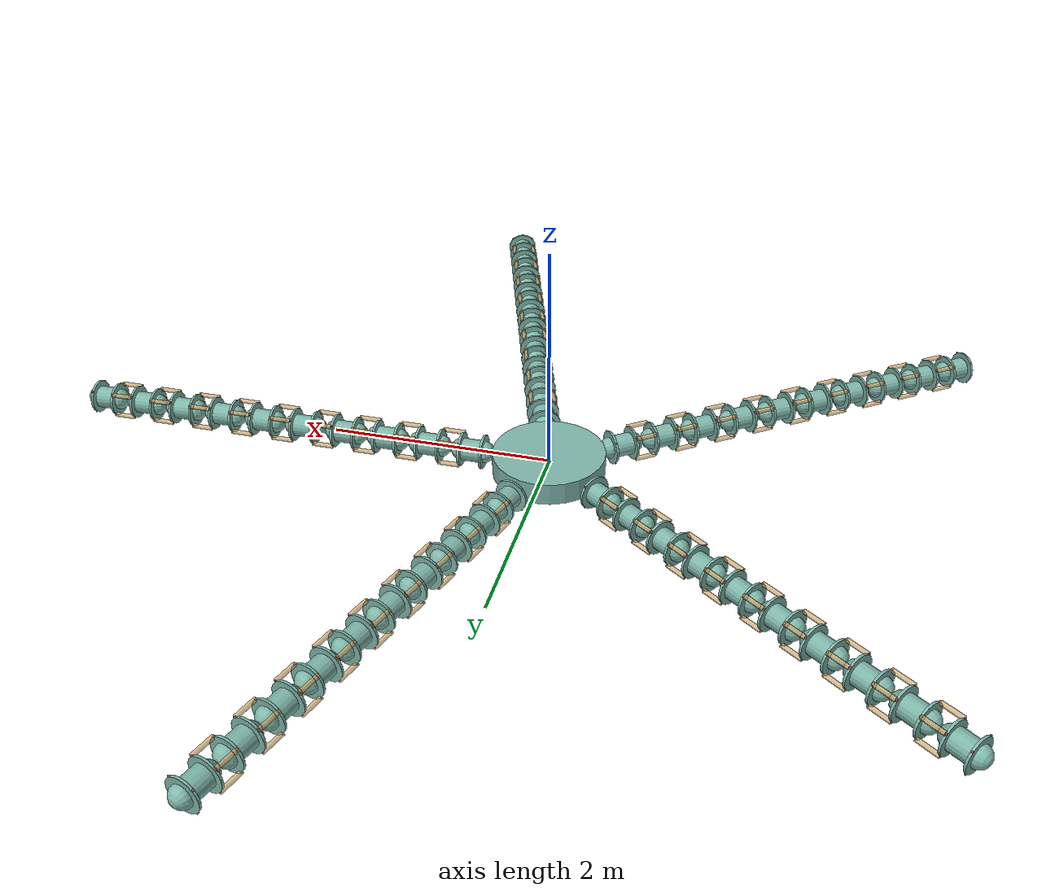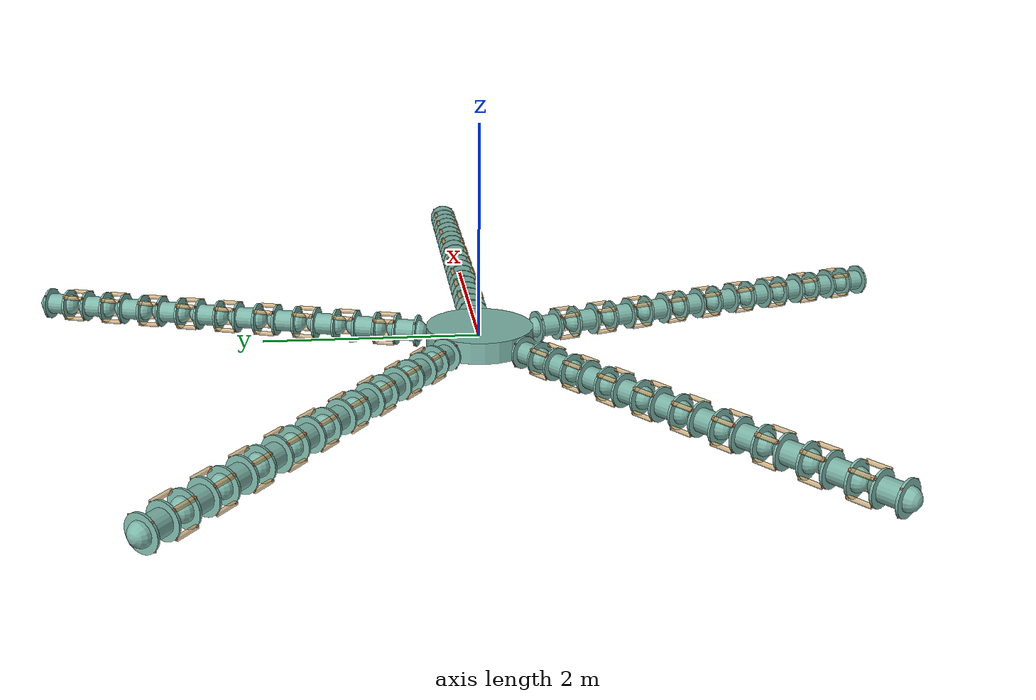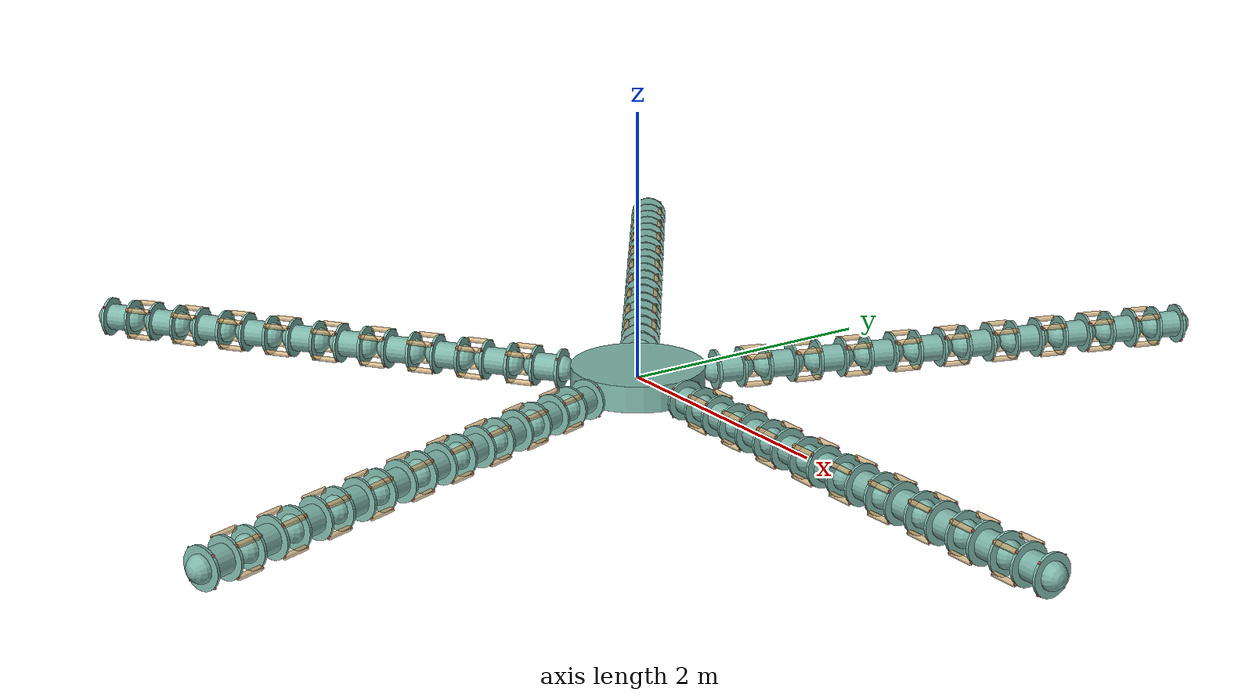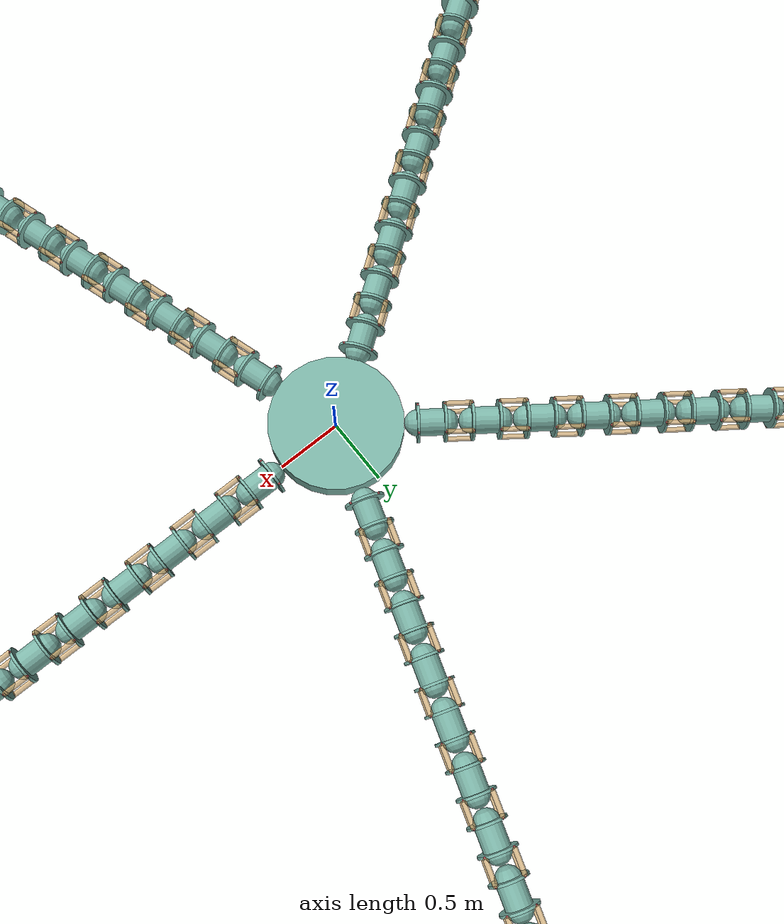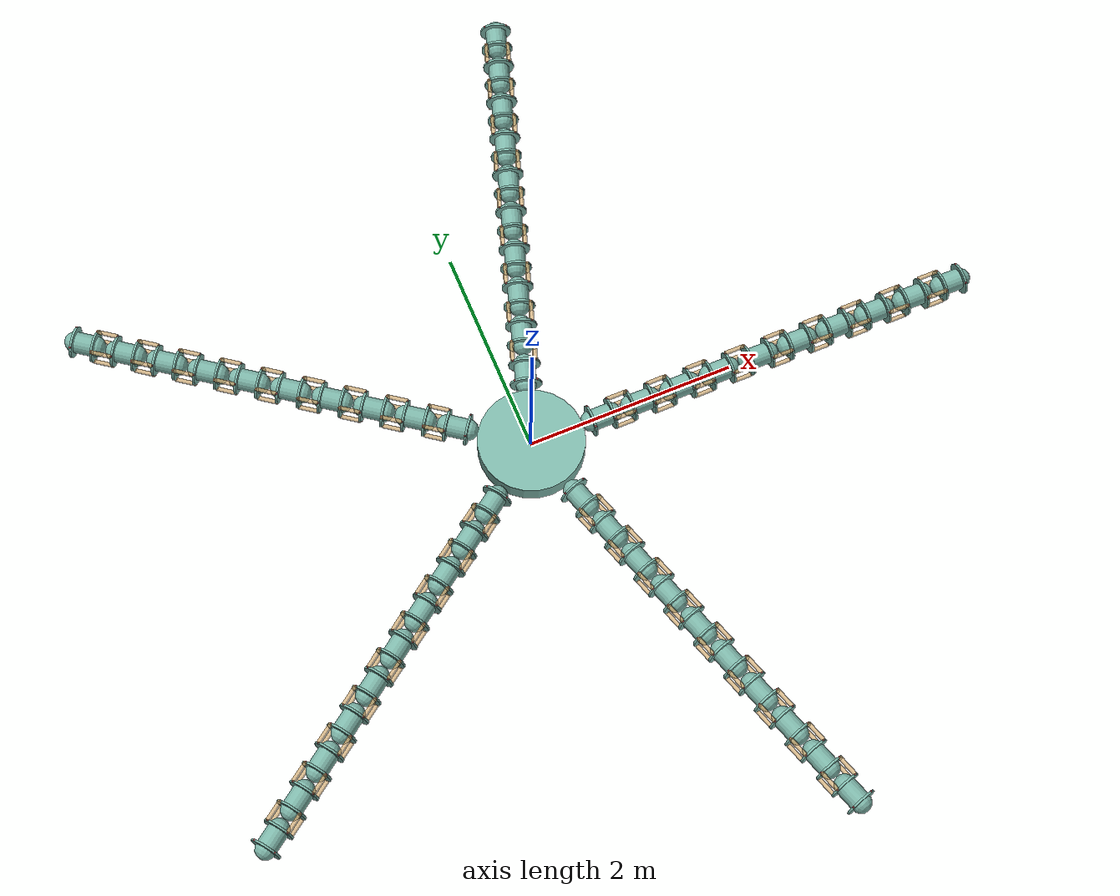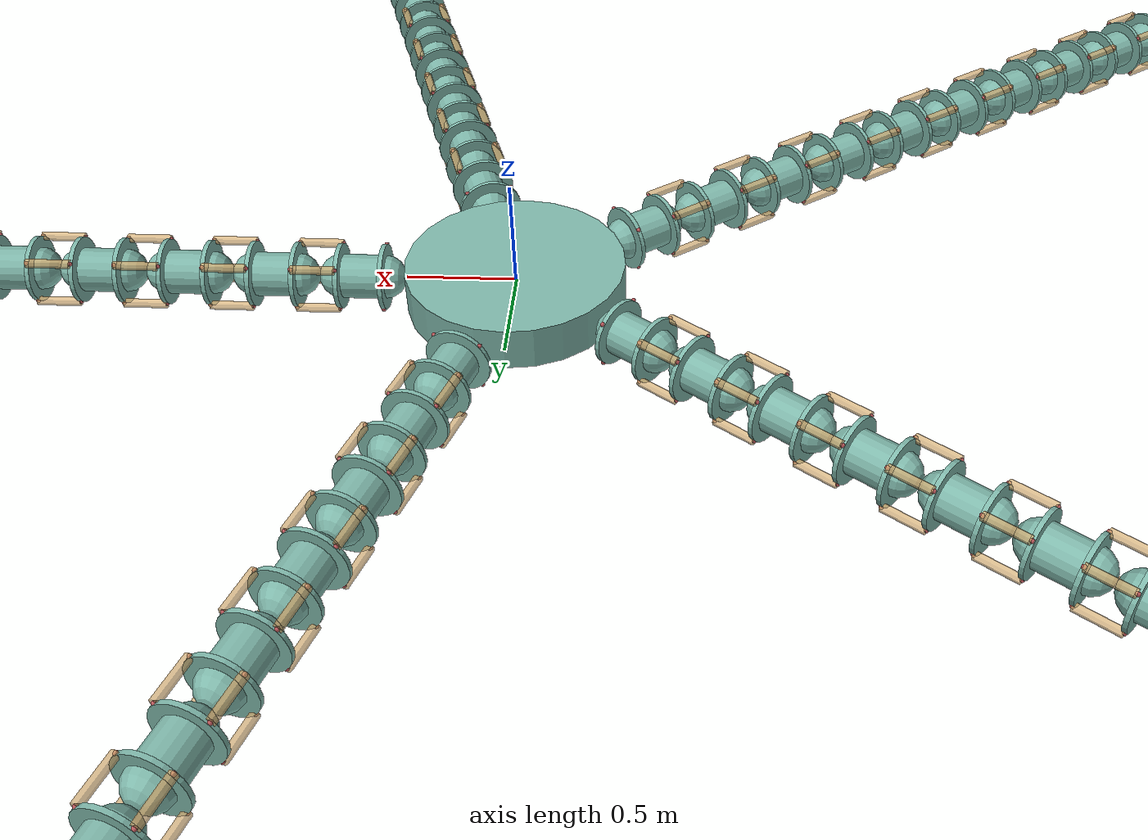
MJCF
<mujoco model="example">
  <compiler angle="radian"/>
  <default>
    <default class="/"/>
  </default>
  <worldbody>
    <body name="//unnamed_body_0">
      <body name="central_disc" pos="0 0 0" euler="0 0 0">
        <geom name="central_disc_disc" class="/" type="cylinder" size="0.5 0.10000000000000001" rgba="0.49019607843137253 0.70980392156862748 0.6588235294117647 1" pos="0 0 0" euler="0 0 0"/>
        <body name="arm_0" pos="0.5 0 0" euler="0 0 0">
          <body name="arm_0_segment_0" pos="0 0 0" euler="0 0 0">
            <geom name="arm_0_segment_0_capsule" class="/" type="capsule" size="0.10000000000000001 0.10000000000000001" rgba="0.49019607843137253 0.70980392156862748 0.6588235294117647 1" pos="0.20000000000000001 0 0" euler="0 1.5707963267948966 0"/>
            <joint name="arm_0_segment_0_in_plane_joint" class="/" type="hinge" pos="0 0 0" axis="0 0 1" limited="true" stiffness="1" range="-0.3490658503988659 0.3490658503988659" damping="0.10000000000000001"/>
            <joint name="arm_0_segment_0_out_of_plane_joint" class="/" type="hinge" pos="0 0 0" axis="0 1 0" limited="true" stiffness="1" range="-0.3490658503988659 0.3490658503988659" damping="0.10000000000000001"/>
            <geom name="arm_0_segment_0_tendon_plate_proximal" class="/" type="cylinder" size="0.15000000000000002 0.01" rgba="0.49019607843137253 0.70980392156862748 0.6588235294117647 1" pos="0.10000000000000001 0 0" euler="0 1.5707963267948966 0"/>
            <site name="arm_0_segment_0_muscle_attachment_point_proximal_0" class="/" type="sphere" rgba="0.71764705882352942 0.33725490196078434 0.34901960784313724 1" size="0.01" pos="0.10000000000000001 0.10606601717798216 -0.10606601717798214"/>
            <site name="arm_0_segment_0_muscle_attachment_point_proximal_1" class="/" type="sphere" rgba="0.71764705882352942 0.33725490196078434 0.34901960784313724 1" size="0.01" pos="0.10000000000000001 -0.10606601717798214 -0.10606601717798216"/>
            <site name="arm_0_segment_0_muscle_attachment_point_proximal_2" class="/" type="sphere" rgba="0.71764705882352942 0.33725490196078434 0.34901960784313724 1" size="0.01" pos="0.10000000000000001 0.10606601717798216 0.10606601717798214"/>
            <site name="arm_0_segment_0_muscle_attachment_point_proximal_3" class="/" type="sphere" rgba="0.71764705882352942 0.33725490196078434 0.34901960784313724 1" size="0.01" pos="0.10000000000000001 -0.10606601717798214 0.10606601717798216"/>
            <geom name="arm_0_segment_0_tendon_plate_distal" class="/" type="cylinder" size="0.15000000000000002 0.01" rgba="0.49019607843137253 0.70980392156862748 0.6588235294117647 1" pos="0.30000000000000004 0 0" euler="0 1.5707963267948966 0"/>
            <site name="arm_0_segment_0_muscle_attachment_point_distal_0" class="/" type="sphere" rgba="0.71764705882352942 0.33725490196078434 0.34901960784313724 1" size="0.01" pos="0.30000000000000004 0.10606601717798216 -0.10606601717798214"/>
            <site name="arm_0_segment_0_muscle_attachment_point_distal_1" class="/" type="sphere" rgba="0.71764705882352942 0.33725490196078434 0.34901960784313724 1" size="0.01" pos="0.30000000000000004 -0.10606601717798214 -0.10606601717798216"/>
            <site name="arm_0_segment_0_muscle_attachment_point_distal_2" class="/" type="sphere" rgba="0.71764705882352942 0.33725490196078434 0.34901960784313724 1" size="0.01" pos="0.30000000000000004 0.10606601717798216 0.10606601717798214"/>
            <site name="arm_0_segment_0_muscle_attachment_point_distal_3" class="/" type="sphere" rgba="0.71764705882352942 0.33725490196078434 0.34901960784313724 1" size="0.01" pos="0.30000000000000004 -0.10606601717798214 0.10606601717798216"/>
            <body name="arm_0_segment_1" pos="0.40000000000000002 0 0" euler="0 0 0">
              <geom name="arm_0_segment_1_capsule" class="/" type="capsule" size="0.10000000000000001 0.10000000000000001" rgba="0.49019607843137253 0.70980392156862748 0.6588235294117647 1" pos="0.20000000000000001 0 0" euler="0 1.5707963267948966 0"/>
              <joint name="arm_0_segment_1_in_plane_joint" class="/" type="hinge" pos="0 0 0" axis="0 0 1" limited="true" stiffness="1" range="-0.3490658503988659 0.3490658503988659" damping="0.10000000000000001"/>
              <joint name="arm_0_segment_1_out_of_plane_joint" class="/" type="hinge" pos="0 0 0" axis="0 1 0" limited="true" stiffness="1" range="-0.3490658503988659 0.3490658503988659" damping="0.10000000000000001"/>
              <geom name="arm_0_segment_1_tendon_plate_proximal" class="/" type="cylinder" size="0.15000000000000002 0.01" rgba="0.49019607843137253 0.70980392156862748 0.6588235294117647 1" pos="0.10000000000000001 0 0" euler="0 1.5707963267948966 0"/>
              <site name="arm_0_segment_1_muscle_attachment_point_proximal_0" class="/" type="sphere" rgba="0.71764705882352942 0.33725490196078434 0.34901960784313724 1" size="0.01" pos="0.10000000000000001 0.10606601717798216 -0.10606601717798214"/>
              <site name="arm_0_segment_1_muscle_attachment_point_proximal_1" class="/" type="sphere" rgba="0.71764705882352942 0.33725490196078434 0.34901960784313724 1" size="0.01" pos="0.10000000000000001 -0.10606601717798214 -0.10606601717798216"/>
              <site name="arm_0_segment_1_muscle_attachment_point_proximal_2" class="/" type="sphere" rgba="0.71764705882352942 0.33725490196078434 0.34901960784313724 1" size="0.01" pos="0.10000000000000001 0.10606601717798216 0.10606601717798214"/>
              <site name="arm_0_segment_1_muscle_attachment_point_proximal_3" class="/" type="sphere" rgba="0.71764705882352942 0.33725490196078434 0.34901960784313724 1" size="0.01" pos="0.10000000000000001 -0.10606601717798214 0.10606601717798216"/>
              <geom name="arm_0_segment_1_tendon_plate_distal" class="/" type="cylinder" size="0.15000000000000002 0.01" rgba="0.49019607843137253 0.70980392156862748 0.6588235294117647 1" pos="0.30000000000000004 0 0" euler="0 1.5707963267948966 0"/>
              <site name="arm_0_segment_1_muscle_attachment_point_distal_0" class="/" type="sphere" rgba="0.71764705882352942 0.33725490196078434 0.34901960784313724 1" size="0.01" pos="0.30000000000000004 0.10606601717798216 -0.10606601717798214"/>
              <site name="arm_0_segment_1_muscle_attachment_point_distal_1" class="/" type="sphere" rgba="0.71764705882352942 0.33725490196078434 0.34901960784313724 1" size="0.01" pos="0.30000000000000004 -0.10606601717798214 -0.10606601717798216"/>
              <site name="arm_0_segment_1_muscle_attachment_point_distal_2" class="/" type="sphere" rgba="0.71764705882352942 0.33725490196078434 0.34901960784313724 1" size="0.01" pos="0.30000000000000004 0.10606601717798216 0.10606601717798214"/>
              <site name="arm_0_segment_1_muscle_attachment_point_distal_3" class="/" type="sphere" rgba="0.71764705882352942 0.33725490196078434 0.34901960784313724 1" size="0.01" pos="0.30000000000000004 -0.10606601717798214 0.10606601717798216"/>
              <body name="arm_0_segment_2" pos="0.40000000000000002 0 0" euler="0 0 0">
                <geom name="arm_0_segment_2_capsule" class="/" type="capsule" size="0.10000000000000001 0.10000000000000001" rgba="0.49019607843137253 0.70980392156862748 0.6588235294117647 1" pos="0.20000000000000001 0 0" euler="0 1.5707963267948966 0"/>
                <joint name="arm_0_segment_2_in_plane_joint" class="/" type="hinge" pos="0 0 0" axis="0 0 1" limited="true" stiffness="1" range="-0.3490658503988659 0.3490658503988659" damping="0.10000000000000001"/>
                <joint name="arm_0_segment_2_out_of_plane_joint" class="/" type="hinge" pos="0 0 0" axis="0 1 0" limited="true" stiffness="1" range="-0.3490658503988659 0.3490658503988659" damping="0.10000000000000001"/>
                <geom name="arm_0_segment_2_tendon_plate_proximal" class="/" type="cylinder" size="0.15000000000000002 0.01" rgba="0.49019607843137253 0.70980392156862748 0.6588235294117647 1" pos="0.10000000000000001 0 0" euler="0 1.5707963267948966 0"/>
                <site name="arm_0_segment_2_muscle_attachment_point_proximal_0" class="/" type="sphere" rgba="0.71764705882352942 0.33725490196078434 0.34901960784313724 1" size="0.01" pos="0.10000000000000001 0.10606601717798216 -0.10606601717798214"/>
                <site name="arm_0_segment_2_muscle_attachment_point_proximal_1" class="/" type="sphere" rgba="0.71764705882352942 0.33725490196078434 0.34901960784313724 1" size="0.01" pos="0.10000000000000001 -0.10606601717798214 -0.10606601717798216"/>
                <site name="arm_0_segment_2_muscle_attachment_point_proximal_2" class="/" type="sphere" rgba="0.71764705882352942 0.33725490196078434 0.34901960784313724 1" size="0.01" pos="0.10000000000000001 0.10606601717798216 0.10606601717798214"/>
                <site name="arm_0_segment_2_muscle_attachment_point_proximal_3" class="/" type="sphere" rgba="0.71764705882352942 0.33725490196078434 0.34901960784313724 1" size="0.01" pos="0.10000000000000001 -0.10606601717798214 0.10606601717798216"/>
                <geom name="arm_0_segment_2_tendon_plate_distal" class="/" type="cylinder" size="0.15000000000000002 0.01" rgba="0.49019607843137253 0.70980392156862748 0.6588235294117647 1" pos="0.30000000000000004 0 0" euler="0 1.5707963267948966 0"/>
                <site name="arm_0_segment_2_muscle_attachment_point_distal_0" class="/" type="sphere" rgba="0.71764705882352942 0.33725490196078434 0.34901960784313724 1" size="0.01" pos="0.30000000000000004 0.10606601717798216 -0.10606601717798214"/>
                <site name="arm_0_segment_2_muscle_attachment_point_distal_1" class="/" type="sphere" rgba="0.71764705882352942 0.33725490196078434 0.34901960784313724 1" size="0.01" pos="0.30000000000000004 -0.10606601717798214 -0.10606601717798216"/>
                <site name="arm_0_segment_2_muscle_attachment_point_distal_2" class="/" type="sphere" rgba="0.71764705882352942 0.33725490196078434 0.34901960784313724 1" size="0.01" pos="0.30000000000000004 0.10606601717798216 0.10606601717798214"/>
                <site name="arm_0_segment_2_muscle_attachment_point_distal_3" class="/" type="sphere" rgba="0.71764705882352942 0.33725490196078434 0.34901960784313724 1" size="0.01" pos="0.30000000000000004 -0.10606601717798214 0.10606601717798216"/>
                <body name="arm_0_segment_3" pos="0.40000000000000002 0 0" euler="0 0 0">
                  <geom name="arm_0_segment_3_capsule" class="/" type="capsule" size="0.10000000000000001 0.10000000000000001" rgba="0.49019607843137253 0.70980392156862748 0.6588235294117647 1" pos="0.20000000000000001 0 0" euler="0 1.5707963267948966 0"/>
                  <joint name="arm_0_segment_3_in_plane_joint" class="/" type="hinge" pos="0 0 0" axis="0 0 1" limited="true" stiffness="1" range="-0.3490658503988659 0.3490658503988659" damping="0.10000000000000001"/>
                  <joint name="arm_0_segment_3_out_of_plane_joint" class="/" type="hinge" pos="0 0 0" axis="0 1 0" limited="true" stiffness="1" range="-0.3490658503988659 0.3490658503988659" damping="0.10000000000000001"/>
                  <geom name="arm_0_segment_3_tendon_plate_proximal" class="/" type="cylinder" size="0.15000000000000002 0.01" rgba="0.49019607843137253 0.70980392156862748 0.6588235294117647 1" pos="0.10000000000000001 0 0" euler="0 1.5707963267948966 0"/>
                  <site name="arm_0_segment_3_muscle_attachment_point_proximal_0" class="/" type="sphere" rgba="0.71764705882352942 0.33725490196078434 0.34901960784313724 1" size="0.01" pos="0.10000000000000001 0.10606601717798216 -0.10606601717798214"/>
                  <site name="arm_0_segment_3_muscle_attachment_point_proximal_1" class="/" type="sphere" rgba="0.71764705882352942 0.33725490196078434 0.34901960784313724 1" size="0.01" pos="0.10000000000000001 -0.10606601717798214 -0.10606601717798216"/>
                  <site name="arm_0_segment_3_muscle_attachment_point_proximal_2" class="/" type="sphere" rgba="0.71764705882352942 0.33725490196078434 0.34901960784313724 1" size="0.01" pos="0.10000000000000001 0.10606601717798216 0.10606601717798214"/>
                  <site name="arm_0_segment_3_muscle_attachment_point_proximal_3" class="/" type="sphere" rgba="0.71764705882352942 0.33725490196078434 0.34901960784313724 1" size="0.01" pos="0.10000000000000001 -0.10606601717798214 0.10606601717798216"/>
                  <geom name="arm_0_segment_3_tendon_plate_distal" class="/" type="cylinder" size="0.15000000000000002 0.01" rgba="0.49019607843137253 0.70980392156862748 0.6588235294117647 1" pos="0.30000000000000004 0 0" euler="0 1.5707963267948966 0"/>
                  <site name="arm_0_segment_3_muscle_attachment_point_distal_0" class="/" type="sphere" rgba="0.71764705882352942 0.33725490196078434 0.34901960784313724 1" size="0.01" pos="0.30000000000000004 0.10606601717798216 -0.10606601717798214"/>
                  <site name="arm_0_segment_3_muscle_attachment_point_distal_1" class="/" type="sphere" rgba="0.71764705882352942 0.33725490196078434 0.34901960784313724 1" size="0.01" pos="0.30000000000000004 -0.10606601717798214 -0.10606601717798216"/>
                  <site name="arm_0_segment_3_muscle_attachment_point_distal_2" class="/" type="sphere" rgba="0.71764705882352942 0.33725490196078434 0.34901960784313724 1" size="0.01" pos="0.30000000000000004 0.10606601717798216 0.10606601717798214"/>
                  <site name="arm_0_segment_3_muscle_attachment_point_distal_3" class="/" type="sphere" rgba="0.71764705882352942 0.33725490196078434 0.34901960784313724 1" size="0.01" pos="0.30000000000000004 -0.10606601717798214 0.10606601717798216"/>
                  <body name="arm_0_segment_4" pos="0.40000000000000002 0 0" euler="0 0 0">
                    <geom name="arm_0_segment_4_capsule" class="/" type="capsule" size="0.10000000000000001 0.10000000000000001" rgba="0.49019607843137253 0.70980392156862748 0.6588235294117647 1" pos="0.20000000000000001 0 0" euler="0 1.5707963267948966 0"/>
                    <joint name="arm_0_segment_4_in_plane_joint" class="/" type="hinge" pos="0 0 0" axis="0 0 1" limited="true" stiffness="1" range="-0.3490658503988659 0.3490658503988659" damping="0.10000000000000001"/>
                    <joint name="arm_0_segment_4_out_of_plane_joint" class="/" type="hinge" pos="0 0 0" axis="0 1 0" limited="true" stiffness="1" range="-0.3490658503988659 0.3490658503988659" damping="0.10000000000000001"/>
                    <geom name="arm_0_segment_4_tendon_plate_proximal" class="/" type="cylinder" size="0.15000000000000002 0.01" rgba="0.49019607843137253 0.70980392156862748 0.6588235294117647 1" pos="0.10000000000000001 0 0" euler="0 1.5707963267948966 0"/>
                    <site name="arm_0_segment_4_muscle_attachment_point_proximal_0" class="/" type="sphere" rgba="0.71764705882352942 0.33725490196078434 0.34901960784313724 1" size="0.01" pos="0.10000000000000001 0.10606601717798216 -0.10606601717798214"/>
                    <site name="arm_0_segment_4_muscle_attachment_point_proximal_1" class="/" type="sphere" rgba="0.71764705882352942 0.33725490196078434 0.34901960784313724 1" size="0.01" pos="0.10000000000000001 -0.10606601717798214 -0.10606601717798216"/>
                    <site name="arm_0_segment_4_muscle_attachment_point_proximal_2" class="/" type="sphere" rgba="0.71764705882352942 0.33725490196078434 0.34901960784313724 1" size="0.01" pos="0.10000000000000001 0.10606601717798216 0.10606601717798214"/>
                    <site name="arm_0_segment_4_muscle_attachment_point_proximal_3" class="/" type="sphere" rgba="0.71764705882352942 0.33725490196078434 0.34901960784313724 1" size="0.01" pos="0.10000000000000001 -0.10606601717798214 0.10606601717798216"/>
                    <geom name="arm_0_segment_4_tendon_plate_distal" class="/" type="cylinder" size="0.15000000000000002 0.01" rgba="0.49019607843137253 0.70980392156862748 0.6588235294117647 1" pos="0.30000000000000004 0 0" euler="0 1.5707963267948966 0"/>
                    <site name="arm_0_segment_4_muscle_attachment_point_distal_0" class="/" type="sphere" rgba="0.71764705882352942 0.33725490196078434 0.34901960784313724 1" size="0.01" pos="0.30000000000000004 0.10606601717798216 -0.10606601717798214"/>
                    <site name="arm_0_segment_4_muscle_attachment_point_distal_1" class="/" type="sphere" rgba="0.71764705882352942 0.33725490196078434 0.34901960784313724 1" size="0.01" pos="0.30000000000000004 -0.10606601717798214 -0.10606601717798216"/>
                    <site name="arm_0_segment_4_muscle_attachment_point_distal_2" class="/" type="sphere" rgba="0.71764705882352942 0.33725490196078434 0.34901960784313724 1" size="0.01" pos="0.30000000000000004 0.10606601717798216 0.10606601717798214"/>
                    <site name="arm_0_segment_4_muscle_attachment_point_distal_3" class="/" type="sphere" rgba="0.71764705882352942 0.33725490196078434 0.34901960784313724 1" size="0.01" pos="0.30000000000000004 -0.10606601717798214 0.10606601717798216"/>
                    <body name="arm_0_segment_5" pos="0.40000000000000002 0 0" euler="0 0 0">
                      <geom name="arm_0_segment_5_capsule" class="/" type="capsule" size="0.10000000000000001 0.10000000000000001" rgba="0.49019607843137253 0.70980392156862748 0.6588235294117647 1" pos="0.20000000000000001 0 0" euler="0 1.5707963267948966 0"/>
                      <joint name="arm_0_segment_5_in_plane_joint" class="/" type="hinge" pos="0 0 0" axis="0 0 1" limited="true" stiffness="1" range="-0.3490658503988659 0.3490658503988659" damping="0.10000000000000001"/>
                      <joint name="arm_0_segment_5_out_of_plane_joint" class="/" type="hinge" pos="0 0 0" axis="0 1 0" limited="true" stiffness="1" range="-0.3490658503988659 0.3490658503988659" damping="0.10000000000000001"/>
                      <geom name="arm_0_segment_5_tendon_plate_proximal" class="/" type="cylinder" size="0.15000000000000002 0.01" rgba="0.49019607843137253 0.70980392156862748 0.6588235294117647 1" pos="0.10000000000000001 0 0" euler="0 1.5707963267948966 0"/>
                      <site name="arm_0_segment_5_muscle_attachment_point_proximal_0" class="/" type="sphere" rgba="0.71764705882352942 0.33725490196078434 0.34901960784313724 1" size="0.01" pos="0.10000000000000001 0.10606601717798216 -0.10606601717798214"/>
                      <site name="arm_0_segment_5_muscle_attachment_point_proximal_1" class="/" type="sphere" rgba="0.71764705882352942 0.33725490196078434 0.34901960784313724 1" size="0.01" pos="0.10000000000000001 -0.10606601717798214 -0.10606601717798216"/>
                      <site name="arm_0_segment_5_muscle_attachment_point_proximal_2" class="/" type="sphere" rgba="0.71764705882352942 0.33725490196078434 0.34901960784313724 1" size="0.01" pos="0.10000000000000001 0.10606601717798216 0.10606601717798214"/>
                      <site name="arm_0_segment_5_muscle_attachment_point_proximal_3" class="/" type="sphere" rgba="0.71764705882352942 0.33725490196078434 0.34901960784313724 1" size="0.01" pos="0.10000000000000001 -0.10606601717798214 0.10606601717798216"/>
                      <geom name="arm_0_segment_5_tendon_plate_distal" class="/" type="cylinder" size="0.15000000000000002 0.01" rgba="0.49019607843137253 0.70980392156862748 0.6588235294117647 1" pos="0.30000000000000004 0 0" euler="0 1.5707963267948966 0"/>
                      <site name="arm_0_segment_5_muscle_attachment_point_distal_0" class="/" type="sphere" rgba="0.71764705882352942 0.33725490196078434 0.34901960784313724 1" size="0.01" pos="0.30000000000000004 0.10606601717798216 -0.10606601717798214"/>
                      <site name="arm_0_segment_5_muscle_attachment_point_distal_1" class="/" type="sphere" rgba="0.71764705882352942 0.33725490196078434 0.34901960784313724 1" size="0.01" pos="0.30000000000000004 -0.10606601717798214 -0.10606601717798216"/>
                      <site name="arm_0_segment_5_muscle_attachment_point_distal_2" class="/" type="sphere" rgba="0.71764705882352942 0.33725490196078434 0.34901960784313724 1" size="0.01" pos="0.30000000000000004 0.10606601717798216 0.10606601717798214"/>
                      <site name="arm_0_segment_5_muscle_attachment_point_distal_3" class="/" type="sphere" rgba="0.71764705882352942 0.33725490196078434 0.34901960784313724 1" size="0.01" pos="0.30000000000000004 -0.10606601717798214 0.10606601717798216"/>
                      <body name="arm_0_segment_6" pos="0.40000000000000002 0 0" euler="0 0 0">
                        <geom name="arm_0_segment_6_capsule" class="/" type="capsule" size="0.10000000000000001 0.10000000000000001" rgba="0.49019607843137253 0.70980392156862748 0.6588235294117647 1" pos="0.20000000000000001 0 0" euler="0 1.5707963267948966 0"/>
                        <joint name="arm_0_segment_6_in_plane_joint" class="/" type="hinge" pos="0 0 0" axis="0 0 1" limited="true" stiffness="1" range="-0.3490658503988659 0.3490658503988659" damping="0.10000000000000001"/>
                        <joint name="arm_0_segment_6_out_of_plane_joint" class="/" type="hinge" pos="0 0 0" axis="0 1 0" limited="true" stiffness="1" range="-0.3490658503988659 0.3490658503988659" damping="0.10000000000000001"/>
                        <geom name="arm_0_segment_6_tendon_plate_proximal" class="/" type="cylinder" size="0.15000000000000002 0.01" rgba="0.49019607843137253 0.70980392156862748 0.6588235294117647 1" pos="0.10000000000000001 0 0" euler="0 1.5707963267948966 0"/>
                        <site name="arm_0_segment_6_muscle_attachment_point_proximal_0" class="/" type="sphere" rgba="0.71764705882352942 0.33725490196078434 0.34901960784313724 1" size="0.01" pos="0.10000000000000001 0.10606601717798216 -0.10606601717798214"/>
                        <site name="arm_0_segment_6_muscle_attachment_point_proximal_1" class="/" type="sphere" rgba="0.71764705882352942 0.33725490196078434 0.34901960784313724 1" size="0.01" pos="0.10000000000000001 -0.10606601717798214 -0.10606601717798216"/>
                        <site name="arm_0_segment_6_muscle_attachment_point_proximal_2" class="/" type="sphere" rgba="0.71764705882352942 0.33725490196078434 0.34901960784313724 1" size="0.01" pos="0.10000000000000001 0.10606601717798216 0.10606601717798214"/>
                        <site name="arm_0_segment_6_muscle_attachment_point_proximal_3" class="/" type="sphere" rgba="0.71764705882352942 0.33725490196078434 0.34901960784313724 1" size="0.01" pos="0.10000000000000001 -0.10606601717798214 0.10606601717798216"/>
                        <geom name="arm_0_segment_6_tendon_plate_distal" class="/" type="cylinder" size="0.15000000000000002 0.01" rgba="0.49019607843137253 0.70980392156862748 0.6588235294117647 1" pos="0.30000000000000004 0 0" euler="0 1.5707963267948966 0"/>
                        <site name="arm_0_segment_6_muscle_attachment_point_distal_0" class="/" type="sphere" rgba="0.71764705882352942 0.33725490196078434 0.34901960784313724 1" size="0.01" pos="0.30000000000000004 0.10606601717798216 -0.10606601717798214"/>
                        <site name="arm_0_segment_6_muscle_attachment_point_distal_1" class="/" type="sphere" rgba="0.71764705882352942 0.33725490196078434 0.34901960784313724 1" size="0.01" pos="0.30000000000000004 -0.10606601717798214 -0.10606601717798216"/>
                        <site name="arm_0_segment_6_muscle_attachment_point_distal_2" class="/" type="sphere" rgba="0.71764705882352942 0.33725490196078434 0.34901960784313724 1" size="0.01" pos="0.30000000000000004 0.10606601717798216 0.10606601717798214"/>
                        <site name="arm_0_segment_6_muscle_attachment_point_distal_3" class="/" type="sphere" rgba="0.71764705882352942 0.33725490196078434 0.34901960784313724 1" size="0.01" pos="0.30000000000000004 -0.10606601717798214 0.10606601717798216"/>
                        <body name="arm_0_segment_7" pos="0.40000000000000002 0 0" euler="0 0 0">
                          <geom name="arm_0_segment_7_capsule" class="/" type="capsule" size="0.10000000000000001 0.10000000000000001" rgba="0.49019607843137253 0.70980392156862748 0.6588235294117647 1" pos="0.20000000000000001 0 0" euler="0 1.5707963267948966 0"/>
                          <joint name="arm_0_segment_7_in_plane_joint" class="/" type="hinge" pos="0 0 0" axis="0 0 1" limited="true" stiffness="1" range="-0.3490658503988659 0.3490658503988659" damping="0.10000000000000001"/>
                          <joint name="arm_0_segment_7_out_of_plane_joint" class="/" type="hinge" pos="0 0 0" axis="0 1 0" limited="true" stiffness="1" range="-0.3490658503988659 0.3490658503988659" damping="0.10000000000000001"/>
                          <geom name="arm_0_segment_7_tendon_plate_proximal" class="/" type="cylinder" size="0.15000000000000002 0.01" rgba="0.49019607843137253 0.70980392156862748 0.6588235294117647 1" pos="0.10000000000000001 0 0" euler="0 1.5707963267948966 0"/>
                          <site name="arm_0_segment_7_muscle_attachment_point_proximal_0" class="/" type="sphere" rgba="0.71764705882352942 0.33725490196078434 0.34901960784313724 1" size="0.01" pos="0.10000000000000001 0.10606601717798216 -0.10606601717798214"/>
                          <site name="arm_0_segment_7_muscle_attachment_point_proximal_1" class="/" type="sphere" rgba="0.71764705882352942 0.33725490196078434 0.34901960784313724 1" size="0.01" pos="0.10000000000000001 -0.10606601717798214 -0.10606601717798216"/>
                          <site name="arm_0_segment_7_muscle_attachment_point_proximal_2" class="/" type="sphere" rgba="0.71764705882352942 0.33725490196078434 0.34901960784313724 1" size="0.01" pos="0.10000000000000001 0.10606601717798216 0.10606601717798214"/>
                          <site name="arm_0_segment_7_muscle_attachment_point_proximal_3" class="/" type="sphere" rgba="0.71764705882352942 0.33725490196078434 0.34901960784313724 1" size="0.01" pos="0.10000000000000001 -0.10606601717798214 0.10606601717798216"/>
                          <geom name="arm_0_segment_7_tendon_plate_distal" class="/" type="cylinder" size="0.15000000000000002 0.01" rgba="0.49019607843137253 0.70980392156862748 0.6588235294117647 1" pos="0.30000000000000004 0 0" euler="0 1.5707963267948966 0"/>
                          <site name="arm_0_segment_7_muscle_attachment_point_distal_0" class="/" type="sphere" rgba="0.71764705882352942 0.33725490196078434 0.34901960784313724 1" size="0.01" pos="0.30000000000000004 0.10606601717798216 -0.10606601717798214"/>
                          <site name="arm_0_segment_7_muscle_attachment_point_distal_1" class="/" type="sphere" rgba="0.71764705882352942 0.33725490196078434 0.34901960784313724 1" size="0.01" pos="0.30000000000000004 -0.10606601717798214 -0.10606601717798216"/>
                          <site name="arm_0_segment_7_muscle_attachment_point_distal_2" class="/" type="sphere" rgba="0.71764705882352942 0.33725490196078434 0.34901960784313724 1" size="0.01" pos="0.30000000000000004 0.10606601717798216 0.10606601717798214"/>
                          <site name="arm_0_segment_7_muscle_attachment_point_distal_3" class="/" type="sphere" rgba="0.71764705882352942 0.33725490196078434 0.34901960784313724 1" size="0.01" pos="0.30000000000000004 -0.10606601717798214 0.10606601717798216"/>
                          <body name="arm_0_segment_8" pos="0.40000000000000002 0 0" euler="0 0 0">
                            <geom name="arm_0_segment_8_capsule" class="/" type="capsule" size="0.10000000000000001 0.10000000000000001" rgba="0.49019607843137253 0.70980392156862748 0.6588235294117647 1" pos="0.20000000000000001 0 0" euler="0 1.5707963267948966 0"/>
                            <joint name="arm_0_segment_8_in_plane_joint" class="/" type="hinge" pos="0 0 0" axis="0 0 1" limited="true" stiffness="1" range="-0.3490658503988659 0.3490658503988659" damping="0.10000000000000001"/>
                            <joint name="arm_0_segment_8_out_of_plane_joint" class="/" type="hinge" pos="0 0 0" axis="0 1 0" limited="true" stiffness="1" range="-0.3490658503988659 0.3490658503988659" damping="0.10000000000000001"/>
                            <geom name="arm_0_segment_8_tendon_plate_proximal" class="/" type="cylinder" size="0.15000000000000002 0.01" rgba="0.49019607843137253 0.70980392156862748 0.6588235294117647 1" pos="0.10000000000000001 0 0" euler="0 1.5707963267948966 0"/>
                            <site name="arm_0_segment_8_muscle_attachment_point_proximal_0" class="/" type="sphere" rgba="0.71764705882352942 0.33725490196078434 0.34901960784313724 1" size="0.01" pos="0.10000000000000001 0.10606601717798216 -0.10606601717798214"/>
                            <site name="arm_0_segment_8_muscle_attachment_point_proximal_1" class="/" type="sphere" rgba="0.71764705882352942 0.33725490196078434 0.34901960784313724 1" size="0.01" pos="0.10000000000000001 -0.10606601717798214 -0.10606601717798216"/>
                            <site name="arm_0_segment_8_muscle_attachment_point_proximal_2" class="/" type="sphere" rgba="0.71764705882352942 0.33725490196078434 0.34901960784313724 1" size="0.01" pos="0.10000000000000001 0.10606601717798216 0.10606601717798214"/>
                            <site name="arm_0_segment_8_muscle_attachment_point_proximal_3" class="/" type="sphere" rgba="0.71764705882352942 0.33725490196078434 0.34901960784313724 1" size="0.01" pos="0.10000000000000001 -0.10606601717798214 0.10606601717798216"/>
                            <geom name="arm_0_segment_8_tendon_plate_distal" class="/" type="cylinder" size="0.15000000000000002 0.01" rgba="0.49019607843137253 0.70980392156862748 0.6588235294117647 1" pos="0.30000000000000004 0 0" euler="0 1.5707963267948966 0"/>
                            <site name="arm_0_segment_8_muscle_attachment_point_distal_0" class="/" type="sphere" rgba="0.71764705882352942 0.33725490196078434 0.34901960784313724 1" size="0.01" pos="0.30000000000000004 0.10606601717798216 -0.10606601717798214"/>
                            <site name="arm_0_segment_8_muscle_attachment_point_distal_1" class="/" type="sphere" rgba="0.71764705882352942 0.33725490196078434 0.34901960784313724 1" size="0.01" pos="0.30000000000000004 -0.10606601717798214 -0.10606601717798216"/>
                            <site name="arm_0_segment_8_muscle_attachment_point_distal_2" class="/" type="sphere" rgba="0.71764705882352942 0.33725490196078434 0.34901960784313724 1" size="0.01" pos="0.30000000000000004 0.10606601717798216 0.10606601717798214"/>
                            <site name="arm_0_segment_8_muscle_attachment_point_distal_3" class="/" type="sphere" rgba="0.71764705882352942 0.33725490196078434 0.34901960784313724 1" size="0.01" pos="0.30000000000000004 -0.10606601717798214 0.10606601717798216"/>
                            <body name="arm_0_segment_9" pos="0.40000000000000002 0 0" euler="0 0 0">
                              <geom name="arm_0_segment_9_capsule" class="/" type="capsule" size="0.10000000000000001 0.10000000000000001" rgba="0.49019607843137253 0.70980392156862748 0.6588235294117647 1" pos="0.20000000000000001 0 0" euler="0 1.5707963267948966 0"/>
                              <joint name="arm_0_segment_9_in_plane_joint" class="/" type="hinge" pos="0 0 0" axis="0 0 1" limited="true" stiffness="1" range="-0.3490658503988659 0.3490658503988659" damping="0.10000000000000001"/>
                              <joint name="arm_0_segment_9_out_of_plane_joint" class="/" type="hinge" pos="0 0 0" axis="0 1 0" limited="true" stiffness="1" range="-0.3490658503988659 0.3490658503988659" damping="0.10000000000000001"/>
                              <geom name="arm_0_segment_9_tendon_plate_proximal" class="/" type="cylinder" size="0.15000000000000002 0.01" rgba="0.49019607843137253 0.70980392156862748 0.6588235294117647 1" pos="0.10000000000000001 0 0" euler="0 1.5707963267948966 0"/>
                              <site name="arm_0_segment_9_muscle_attachment_point_proximal_0" class="/" type="sphere" rgba="0.71764705882352942 0.33725490196078434 0.34901960784313724 1" size="0.01" pos="0.10000000000000001 0.10606601717798216 -0.10606601717798214"/>
                              <site name="arm_0_segment_9_muscle_attachment_point_proximal_1" class="/" type="sphere" rgba="0.71764705882352942 0.33725490196078434 0.34901960784313724 1" size="0.01" pos="0.10000000000000001 -0.10606601717798214 -0.10606601717798216"/>
                              <site name="arm_0_segment_9_muscle_attachment_point_proximal_2" class="/" type="sphere" rgba="0.71764705882352942 0.33725490196078434 0.34901960784313724 1" size="0.01" pos="0.10000000000000001 0.10606601717798216 0.10606601717798214"/>
                              <site name="arm_0_segment_9_muscle_attachment_point_proximal_3" class="/" type="sphere" rgba="0.71764705882352942 0.33725490196078434 0.34901960784313724 1" size="0.01" pos="0.10000000000000001 -0.10606601717798214 0.10606601717798216"/>
                              <geom name="arm_0_segment_9_tendon_plate_distal" class="/" type="cylinder" size="0.15000000000000002 0.01" rgba="0.49019607843137253 0.70980392156862748 0.6588235294117647 1" pos="0.30000000000000004 0 0" euler="0 1.5707963267948966 0"/>
                              <site name="arm_0_segment_9_muscle_attachment_point_distal_0" class="/" type="sphere" rgba="0.71764705882352942 0.33725490196078434 0.34901960784313724 1" size="0.01" pos="0.30000000000000004 0.10606601717798216 -0.10606601717798214"/>
                              <site name="arm_0_segment_9_muscle_attachment_point_distal_1" class="/" type="sphere" rgba="0.71764705882352942 0.33725490196078434 0.34901960784313724 1" size="0.01" pos="0.30000000000000004 -0.10606601717798214 -0.10606601717798216"/>
                              <site name="arm_0_segment_9_muscle_attachment_point_distal_2" class="/" type="sphere" rgba="0.71764705882352942 0.33725490196078434 0.34901960784313724 1" size="0.01" pos="0.30000000000000004 0.10606601717798216 0.10606601717798214"/>
                              <site name="arm_0_segment_9_muscle_attachment_point_distal_3" class="/" type="sphere" rgba="0.71764705882352942 0.33725490196078434 0.34901960784313724 1" size="0.01" pos="0.30000000000000004 -0.10606601717798214 0.10606601717798216"/>
                            </body>
                          </body>
                        </body>
                      </body>
                    </body>
                  </body>
                </body>
              </body>
            </body>
          </body>
        </body>
        <body name="arm_1" pos="0.15450849718747373 0.47552825814757677 0" euler="0 0 1.2566370614359172">
          <body name="arm_1_segment_0" pos="0 0 0" euler="0 0 0">
            <geom name="arm_1_segment_0_capsule" class="/" type="capsule" size="0.10000000000000001 0.10000000000000001" rgba="0.49019607843137253 0.70980392156862748 0.6588235294117647 1" pos="0.20000000000000001 0 0" euler="0 1.5707963267948966 0"/>
            <joint name="arm_1_segment_0_in_plane_joint" class="/" type="hinge" pos="0 0 0" axis="0 0 1" limited="true" stiffness="1" range="-0.3490658503988659 0.3490658503988659" damping="0.10000000000000001"/>
            <joint name="arm_1_segment_0_out_of_plane_joint" class="/" type="hinge" pos="0 0 0" axis="0 1 0" limited="true" stiffness="1" range="-0.3490658503988659 0.3490658503988659" damping="0.10000000000000001"/>
            <geom name="arm_1_segment_0_tendon_plate_proximal" class="/" type="cylinder" size="0.15000000000000002 0.01" rgba="0.49019607843137253 0.70980392156862748 0.6588235294117647 1" pos="0.10000000000000001 0 0" euler="0 1.5707963267948966 0"/>
            <site name="arm_1_segment_0_muscle_attachment_point_proximal_0" class="/" type="sphere" rgba="0.71764705882352942 0.33725490196078434 0.34901960784313724 1" size="0.01" pos="0.10000000000000001 0.10606601717798216 -0.10606601717798214"/>
            <site name="arm_1_segment_0_muscle_attachment_point_proximal_1" class="/" type="sphere" rgba="0.71764705882352942 0.33725490196078434 0.34901960784313724 1" size="0.01" pos="0.10000000000000001 -0.10606601717798214 -0.10606601717798216"/>
            <site name="arm_1_segment_0_muscle_attachment_point_proximal_2" class="/" type="sphere" rgba="0.71764705882352942 0.33725490196078434 0.34901960784313724 1" size="0.01" pos="0.10000000000000001 0.10606601717798216 0.10606601717798214"/>
            <site name="arm_1_segment_0_muscle_attachment_point_proximal_3" class="/" type="sphere" rgba="0.71764705882352942 0.33725490196078434 0.34901960784313724 1" size="0.01" pos="0.10000000000000001 -0.10606601717798214 0.10606601717798216"/>
            <geom name="arm_1_segment_0_tendon_plate_distal" class="/" type="cylinder" size="0.15000000000000002 0.01" rgba="0.49019607843137253 0.70980392156862748 0.6588235294117647 1" pos="0.30000000000000004 0 0" euler="0 1.5707963267948966 0"/>
            <site name="arm_1_segment_0_muscle_attachment_point_distal_0" class="/" type="sphere" rgba="0.71764705882352942 0.33725490196078434 0.34901960784313724 1" size="0.01" pos="0.30000000000000004 0.10606601717798216 -0.10606601717798214"/>
            <site name="arm_1_segment_0_muscle_attachment_point_distal_1" class="/" type="sphere" rgba="0.71764705882352942 0.33725490196078434 0.34901960784313724 1" size="0.01" pos="0.30000000000000004 -0.10606601717798214 -0.10606601717798216"/>
            <site name="arm_1_segment_0_muscle_attachment_point_distal_2" class="/" type="sphere" rgba="0.71764705882352942 0.33725490196078434 0.34901960784313724 1" size="0.01" pos="0.30000000000000004 0.10606601717798216 0.10606601717798214"/>
            <site name="arm_1_segment_0_muscle_attachment_point_distal_3" class="/" type="sphere" rgba="0.71764705882352942 0.33725490196078434 0.34901960784313724 1" size="0.01" pos="0.30000000000000004 -0.10606601717798214 0.10606601717798216"/>
            <body name="arm_1_segment_1" pos="0.40000000000000002 0 0" euler="0 0 0">
              <geom name="arm_1_segment_1_capsule" class="/" type="capsule" size="0.10000000000000001 0.10000000000000001" rgba="0.49019607843137253 0.70980392156862748 0.6588235294117647 1" pos="0.20000000000000001 0 0" euler="0 1.5707963267948966 0"/>
              <joint name="arm_1_segment_1_in_plane_joint" class="/" type="hinge" pos="0 0 0" axis="0 0 1" limited="true" stiffness="1" range="-0.3490658503988659 0.3490658503988659" damping="0.10000000000000001"/>
              <joint name="arm_1_segment_1_out_of_plane_joint" class="/" type="hinge" pos="0 0 0" axis="0 1 0" limited="true" stiffness="1" range="-0.3490658503988659 0.3490658503988659" damping="0.10000000000000001"/>
              <geom name="arm_1_segment_1_tendon_plate_proximal" class="/" type="cylinder" size="0.15000000000000002 0.01" rgba="0.49019607843137253 0.70980392156862748 0.6588235294117647 1" pos="0.10000000000000001 0 0" euler="0 1.5707963267948966 0"/>
              <site name="arm_1_segment_1_muscle_attachment_point_proximal_0" class="/" type="sphere" rgba="0.71764705882352942 0.33725490196078434 0.34901960784313724 1" size="0.01" pos="0.10000000000000001 0.10606601717798216 -0.10606601717798214"/>
              <site name="arm_1_segment_1_muscle_attachment_point_proximal_1" class="/" type="sphere" rgba="0.71764705882352942 0.33725490196078434 0.34901960784313724 1" size="0.01" pos="0.10000000000000001 -0.10606601717798214 -0.10606601717798216"/>
              <site name="arm_1_segment_1_muscle_attachment_point_proximal_2" class="/" type="sphere" rgba="0.71764705882352942 0.33725490196078434 0.34901960784313724 1" size="0.01" pos="0.10000000000000001 0.10606601717798216 0.10606601717798214"/>
              <site name="arm_1_segment_1_muscle_attachment_point_proximal_3" class="/" type="sphere" rgba="0.71764705882352942 0.33725490196078434 0.34901960784313724 1" size="0.01" pos="0.10000000000000001 -0.10606601717798214 0.10606601717798216"/>
              <geom name="arm_1_segment_1_tendon_plate_distal" class="/" type="cylinder" size="0.15000000000000002 0.01" rgba="0.49019607843137253 0.70980392156862748 0.6588235294117647 1" pos="0.30000000000000004 0 0" euler="0 1.5707963267948966 0"/>
              <site name="arm_1_segment_1_muscle_attachment_point_distal_0" class="/" type="sphere" rgba="0.71764705882352942 0.33725490196078434 0.34901960784313724 1" size="0.01" pos="0.30000000000000004 0.10606601717798216 -0.10606601717798214"/>
              <site name="arm_1_segment_1_muscle_attachment_point_distal_1" class="/" type="sphere" rgba="0.71764705882352942 0.33725490196078434 0.34901960784313724 1" size="0.01" pos="0.30000000000000004 -0.10606601717798214 -0.10606601717798216"/>
              <site name="arm_1_segment_1_muscle_attachment_point_distal_2" class="/" type="sphere" rgba="0.71764705882352942 0.33725490196078434 0.34901960784313724 1" size="0.01" pos="0.30000000000000004 0.10606601717798216 0.10606601717798214"/>
              <site name="arm_1_segment_1_muscle_attachment_point_distal_3" class="/" type="sphere" rgba="0.71764705882352942 0.33725490196078434 0.34901960784313724 1" size="0.01" pos="0.30000000000000004 -0.10606601717798214 0.10606601717798216"/>
              <body name="arm_1_segment_2" pos="0.40000000000000002 0 0" euler="0 0 0">
                <geom name="arm_1_segment_2_capsule" class="/" type="capsule" size="0.10000000000000001 0.10000000000000001" rgba="0.49019607843137253 0.70980392156862748 0.6588235294117647 1" pos="0.20000000000000001 0 0" euler="0 1.5707963267948966 0"/>
                <joint name="arm_1_segment_2_in_plane_joint" class="/" type="hinge" pos="0 0 0" axis="0 0 1" limited="true" stiffness="1" range="-0.3490658503988659 0.3490658503988659" damping="0.10000000000000001"/>
                <joint name="arm_1_segment_2_out_of_plane_joint" class="/" type="hinge" pos="0 0 0" axis="0 1 0" limited="true" stiffness="1" range="-0.3490658503988659 0.3490658503988659" damping="0.10000000000000001"/>
                <geom name="arm_1_segment_2_tendon_plate_proximal" class="/" type="cylinder" size="0.15000000000000002 0.01" rgba="0.49019607843137253 0.70980392156862748 0.6588235294117647 1" pos="0.10000000000000001 0 0" euler="0 1.5707963267948966 0"/>
                <site name="arm_1_segment_2_muscle_attachment_point_proximal_0" class="/" type="sphere" rgba="0.71764705882352942 0.33725490196078434 0.34901960784313724 1" size="0.01" pos="0.10000000000000001 0.10606601717798216 -0.10606601717798214"/>
                <site name="arm_1_segment_2_muscle_attachment_point_proximal_1" class="/" type="sphere" rgba="0.71764705882352942 0.33725490196078434 0.34901960784313724 1" size="0.01" pos="0.10000000000000001 -0.10606601717798214 -0.10606601717798216"/>
                <site name="arm_1_segment_2_muscle_attachment_point_proximal_2" class="/" type="sphere" rgba="0.71764705882352942 0.33725490196078434 0.34901960784313724 1" size="0.01" pos="0.10000000000000001 0.10606601717798216 0.10606601717798214"/>
                <site name="arm_1_segment_2_muscle_attachment_point_proximal_3" class="/" type="sphere" rgba="0.71764705882352942 0.33725490196078434 0.34901960784313724 1" size="0.01" pos="0.10000000000000001 -0.10606601717798214 0.10606601717798216"/>
                <geom name="arm_1_segment_2_tendon_plate_distal" class="/" type="cylinder" size="0.15000000000000002 0.01" rgba="0.49019607843137253 0.70980392156862748 0.6588235294117647 1" pos="0.30000000000000004 0 0" euler="0 1.5707963267948966 0"/>
                <site name="arm_1_segment_2_muscle_attachment_point_distal_0" class="/" type="sphere" rgba="0.71764705882352942 0.33725490196078434 0.34901960784313724 1" size="0.01" pos="0.30000000000000004 0.10606601717798216 -0.10606601717798214"/>
                <site name="arm_1_segment_2_muscle_attachment_point_distal_1" class="/" type="sphere" rgba="0.71764705882352942 0.33725490196078434 0.34901960784313724 1" size="0.01" pos="0.30000000000000004 -0.10606601717798214 -0.10606601717798216"/>
                <site name="arm_1_segment_2_muscle_attachment_point_distal_2" class="/" type="sphere" rgba="0.71764705882352942 0.33725490196078434 0.34901960784313724 1" size="0.01" pos="0.30000000000000004 0.10606601717798216 0.10606601717798214"/>
                <site name="arm_1_segment_2_muscle_attachment_point_distal_3" class="/" type="sphere" rgba="0.71764705882352942 0.33725490196078434 0.34901960784313724 1" size="0.01" pos="0.30000000000000004 -0.10606601717798214 0.10606601717798216"/>
                <body name="arm_1_segment_3" pos="0.40000000000000002 0 0" euler="0 0 0">
                  <geom name="arm_1_segment_3_capsule" class="/" type="capsule" size="0.10000000000000001 0.10000000000000001" rgba="0.49019607843137253 0.70980392156862748 0.6588235294117647 1" pos="0.20000000000000001 0 0" euler="0 1.5707963267948966 0"/>
                  <joint name="arm_1_segment_3_in_plane_joint" class="/" type="hinge" pos="0 0 0" axis="0 0 1" limited="true" stiffness="1" range="-0.3490658503988659 0.3490658503988659" damping="0.10000000000000001"/>
                  <joint name="arm_1_segment_3_out_of_plane_joint" class="/" type="hinge" pos="0 0 0" axis="0 1 0" limited="true" stiffness="1" range="-0.3490658503988659 0.3490658503988659" damping="0.10000000000000001"/>
                  <geom name="arm_1_segment_3_tendon_plate_proximal" class="/" type="cylinder" size="0.15000000000000002 0.01" rgba="0.49019607843137253 0.70980392156862748 0.6588235294117647 1" pos="0.10000000000000001 0 0" euler="0 1.5707963267948966 0"/>
                  <site name="arm_1_segment_3_muscle_attachment_point_proximal_0" class="/" type="sphere" rgba="0.71764705882352942 0.33725490196078434 0.34901960784313724 1" size="0.01" pos="0.10000000000000001 0.10606601717798216 -0.10606601717798214"/>
                  <site name="arm_1_segment_3_muscle_attachment_point_proximal_1" class="/" type="sphere" rgba="0.71764705882352942 0.33725490196078434 0.34901960784313724 1" size="0.01" pos="0.10000000000000001 -0.10606601717798214 -0.10606601717798216"/>
                  <site name="arm_1_segment_3_muscle_attachment_point_proximal_2" class="/" type="sphere" rgba="0.71764705882352942 0.33725490196078434 0.34901960784313724 1" size="0.01" pos="0.10000000000000001 0.10606601717798216 0.10606601717798214"/>
                  <site name="arm_1_segment_3_muscle_attachment_point_proximal_3" class="/" type="sphere" rgba="0.71764705882352942 0.33725490196078434 0.34901960784313724 1" size="0.01" pos="0.10000000000000001 -0.10606601717798214 0.10606601717798216"/>
                  <geom name="arm_1_segment_3_tendon_plate_distal" class="/" type="cylinder" size="0.15000000000000002 0.01" rgba="0.49019607843137253 0.70980392156862748 0.6588235294117647 1" pos="0.30000000000000004 0 0" euler="0 1.5707963267948966 0"/>
                  <site name="arm_1_segment_3_muscle_attachment_point_distal_0" class="/" type="sphere" rgba="0.71764705882352942 0.33725490196078434 0.34901960784313724 1" size="0.01" pos="0.30000000000000004 0.10606601717798216 -0.10606601717798214"/>
                  <site name="arm_1_segment_3_muscle_attachment_point_distal_1" class="/" type="sphere" rgba="0.71764705882352942 0.33725490196078434 0.34901960784313724 1" size="0.01" pos="0.30000000000000004 -0.10606601717798214 -0.10606601717798216"/>
                  <site name="arm_1_segment_3_muscle_attachment_point_distal_2" class="/" type="sphere" rgba="0.71764705882352942 0.33725490196078434 0.34901960784313724 1" size="0.01" pos="0.30000000000000004 0.10606601717798216 0.10606601717798214"/>
                  <site name="arm_1_segment_3_muscle_attachment_point_distal_3" class="/" type="sphere" rgba="0.71764705882352942 0.33725490196078434 0.34901960784313724 1" size="0.01" pos="0.30000000000000004 -0.10606601717798214 0.10606601717798216"/>
                  <body name="arm_1_segment_4" pos="0.40000000000000002 0 0" euler="0 0 0">
                    <geom name="arm_1_segment_4_capsule" class="/" type="capsule" size="0.10000000000000001 0.10000000000000001" rgba="0.49019607843137253 0.70980392156862748 0.6588235294117647 1" pos="0.20000000000000001 0 0" euler="0 1.5707963267948966 0"/>
                    <joint name="arm_1_segment_4_in_plane_joint" class="/" type="hinge" pos="0 0 0" axis="0 0 1" limited="true" stiffness="1" range="-0.3490658503988659 0.3490658503988659" damping="0.10000000000000001"/>
                    <joint name="arm_1_segment_4_out_of_plane_joint" class="/" type="hinge" pos="0 0 0" axis="0 1 0" limited="true" stiffness="1" range="-0.3490658503988659 0.3490658503988659" damping="0.10000000000000001"/>
                    <geom name="arm_1_segment_4_tendon_plate_proximal" class="/" type="cylinder" size="0.15000000000000002 0.01" rgba="0.49019607843137253 0.70980392156862748 0.6588235294117647 1" pos="0.10000000000000001 0 0" euler="0 1.5707963267948966 0"/>
                    <site name="arm_1_segment_4_muscle_attachment_point_proximal_0" class="/" type="sphere" rgba="0.71764705882352942 0.33725490196078434 0.34901960784313724 1" size="0.01" pos="0.10000000000000001 0.10606601717798216 -0.10606601717798214"/>
                    <site name="arm_1_segment_4_muscle_attachment_point_proximal_1" class="/" type="sphere" rgba="0.71764705882352942 0.33725490196078434 0.34901960784313724 1" size="0.01" pos="0.10000000000000001 -0.10606601717798214 -0.10606601717798216"/>
                    <site name="arm_1_segment_4_muscle_attachment_point_proximal_2" class="/" type="sphere" rgba="0.71764705882352942 0.33725490196078434 0.34901960784313724 1" size="0.01" pos="0.10000000000000001 0.10606601717798216 0.10606601717798214"/>
                    <site name="arm_1_segment_4_muscle_attachment_point_proximal_3" class="/" type="sphere" rgba="0.71764705882352942 0.33725490196078434 0.34901960784313724 1" size="0.01" pos="0.10000000000000001 -0.10606601717798214 0.10606601717798216"/>
                    <geom name="arm_1_segment_4_tendon_plate_distal" class="/" type="cylinder" size="0.15000000000000002 0.01" rgba="0.49019607843137253 0.70980392156862748 0.6588235294117647 1" pos="0.30000000000000004 0 0" euler="0 1.5707963267948966 0"/>
                    <site name="arm_1_segment_4_muscle_attachment_point_distal_0" class="/" type="sphere" rgba="0.71764705882352942 0.33725490196078434 0.34901960784313724 1" size="0.01" pos="0.30000000000000004 0.10606601717798216 -0.10606601717798214"/>
                    <site name="arm_1_segment_4_muscle_attachment_point_distal_1" class="/" type="sphere" rgba="0.71764705882352942 0.33725490196078434 0.34901960784313724 1" size="0.01" pos="0.30000000000000004 -0.10606601717798214 -0.10606601717798216"/>
                    <site name="arm_1_segment_4_muscle_attachment_point_distal_2" class="/" type="sphere" rgba="0.71764705882352942 0.33725490196078434 0.34901960784313724 1" size="0.01" pos="0.30000000000000004 0.10606601717798216 0.10606601717798214"/>
                    <site name="arm_1_segment_4_muscle_attachment_point_distal_3" class="/" type="sphere" rgba="0.71764705882352942 0.33725490196078434 0.34901960784313724 1" size="0.01" pos="0.30000000000000004 -0.10606601717798214 0.10606601717798216"/>
                    <body name="arm_1_segment_5" pos="0.40000000000000002 0 0" euler="0 0 0">
                      <geom name="arm_1_segment_5_capsule" class="/" type="capsule" size="0.10000000000000001 0.10000000000000001" rgba="0.49019607843137253 0.70980392156862748 0.6588235294117647 1" pos="0.20000000000000001 0 0" euler="0 1.5707963267948966 0"/>
                      <joint name="arm_1_segment_5_in_plane_joint" class="/" type="hinge" pos="0 0 0" axis="0 0 1" limited="true" stiffness="1" range="-0.3490658503988659 0.3490658503988659" damping="0.10000000000000001"/>
                      <joint name="arm_1_segment_5_out_of_plane_joint" class="/" type="hinge" pos="0 0 0" axis="0 1 0" limited="true" stiffness="1" range="-0.3490658503988659 0.3490658503988659" damping="0.10000000000000001"/>
                      <geom name="arm_1_segment_5_tendon_plate_proximal" class="/" type="cylinder" size="0.15000000000000002 0.01" rgba="0.49019607843137253 0.70980392156862748 0.6588235294117647 1" pos="0.10000000000000001 0 0" euler="0 1.5707963267948966 0"/>
                      <site name="arm_1_segment_5_muscle_attachment_point_proximal_0" class="/" type="sphere" rgba="0.71764705882352942 0.33725490196078434 0.34901960784313724 1" size="0.01" pos="0.10000000000000001 0.10606601717798216 -0.10606601717798214"/>
                      <site name="arm_1_segment_5_muscle_attachment_point_proximal_1" class="/" type="sphere" rgba="0.71764705882352942 0.33725490196078434 0.34901960784313724 1" size="0.01" pos="0.10000000000000001 -0.10606601717798214 -0.10606601717798216"/>
                      <site name="arm_1_segment_5_muscle_attachment_point_proximal_2" class="/" type="sphere" rgba="0.71764705882352942 0.33725490196078434 0.34901960784313724 1" size="0.01" pos="0.10000000000000001 0.10606601717798216 0.10606601717798214"/>
                      <site name="arm_1_segment_5_muscle_attachment_point_proximal_3" class="/" type="sphere" rgba="0.71764705882352942 0.33725490196078434 0.34901960784313724 1" size="0.01" pos="0.10000000000000001 -0.10606601717798214 0.10606601717798216"/>
                      <geom name="arm_1_segment_5_tendon_plate_distal" class="/" type="cylinder" size="0.15000000000000002 0.01" rgba="0.49019607843137253 0.70980392156862748 0.6588235294117647 1" pos="0.30000000000000004 0 0" euler="0 1.5707963267948966 0"/>
                      <site name="arm_1_segment_5_muscle_attachment_point_distal_0" class="/" type="sphere" rgba="0.71764705882352942 0.33725490196078434 0.34901960784313724 1" size="0.01" pos="0.30000000000000004 0.10606601717798216 -0.10606601717798214"/>
                      <site name="arm_1_segment_5_muscle_attachment_point_distal_1" class="/" type="sphere" rgba="0.71764705882352942 0.33725490196078434 0.34901960784313724 1" size="0.01" pos="0.30000000000000004 -0.10606601717798214 -0.10606601717798216"/>
                      <site name="arm_1_segment_5_muscle_attachment_point_distal_2" class="/" type="sphere" rgba="0.71764705882352942 0.33725490196078434 0.34901960784313724 1" size="0.01" pos="0.30000000000000004 0.10606601717798216 0.10606601717798214"/>
                      <site name="arm_1_segment_5_muscle_attachment_point_distal_3" class="/" type="sphere" rgba="0.71764705882352942 0.33725490196078434 0.34901960784313724 1" size="0.01" pos="0.30000000000000004 -0.10606601717798214 0.10606601717798216"/>
                      <body name="arm_1_segment_6" pos="0.40000000000000002 0 0" euler="0 0 0">
                        <geom name="arm_1_segment_6_capsule" class="/" type="capsule" size="0.10000000000000001 0.10000000000000001" rgba="0.49019607843137253 0.70980392156862748 0.6588235294117647 1" pos="0.20000000000000001 0 0" euler="0 1.5707963267948966 0"/>
                        <joint name="arm_1_segment_6_in_plane_joint" class="/" type="hinge" pos="0 0 0" axis="0 0 1" limited="true" stiffness="1" range="-0.3490658503988659 0.3490658503988659" damping="0.10000000000000001"/>
                        <joint name="arm_1_segment_6_out_of_plane_joint" class="/" type="hinge" pos="0 0 0" axis="0 1 0" limited="true" stiffness="1" range="-0.3490658503988659 0.3490658503988659" damping="0.10000000000000001"/>
                        <geom name="arm_1_segment_6_tendon_plate_proximal" class="/" type="cylinder" size="0.15000000000000002 0.01" rgba="0.49019607843137253 0.70980392156862748 0.6588235294117647 1" pos="0.10000000000000001 0 0" euler="0 1.5707963267948966 0"/>
                        <site name="arm_1_segment_6_muscle_attachment_point_proximal_0" class="/" type="sphere" rgba="0.71764705882352942 0.33725490196078434 0.34901960784313724 1" size="0.01" pos="0.10000000000000001 0.10606601717798216 -0.10606601717798214"/>
                        <site name="arm_1_segment_6_muscle_attachment_point_proximal_1" class="/" type="sphere" rgba="0.71764705882352942 0.33725490196078434 0.34901960784313724 1" size="0.01" pos="0.10000000000000001 -0.10606601717798214 -0.10606601717798216"/>
                        <site name="arm_1_segment_6_muscle_attachment_point_proximal_2" class="/" type="sphere" rgba="0.71764705882352942 0.33725490196078434 0.34901960784313724 1" size="0.01" pos="0.10000000000000001 0.10606601717798216 0.10606601717798214"/>
                        <site name="arm_1_segment_6_muscle_attachment_point_proximal_3" class="/" type="sphere" rgba="0.71764705882352942 0.33725490196078434 0.34901960784313724 1" size="0.01" pos="0.10000000000000001 -0.10606601717798214 0.10606601717798216"/>
                        <geom name="arm_1_segment_6_tendon_plate_distal" class="/" type="cylinder" size="0.15000000000000002 0.01" rgba="0.49019607843137253 0.70980392156862748 0.6588235294117647 1" pos="0.30000000000000004 0 0" euler="0 1.5707963267948966 0"/>
                        <site name="arm_1_segment_6_muscle_attachment_point_distal_0" class="/" type="sphere" rgba="0.71764705882352942 0.33725490196078434 0.34901960784313724 1" size="0.01" pos="0.30000000000000004 0.10606601717798216 -0.10606601717798214"/>
                        <site name="arm_1_segment_6_muscle_attachment_point_distal_1" class="/" type="sphere" rgba="0.71764705882352942 0.33725490196078434 0.34901960784313724 1" size="0.01" pos="0.30000000000000004 -0.10606601717798214 -0.10606601717798216"/>
                        <site name="arm_1_segment_6_muscle_attachment_point_distal_2" class="/" type="sphere" rgba="0.71764705882352942 0.33725490196078434 0.34901960784313724 1" size="0.01" pos="0.30000000000000004 0.10606601717798216 0.10606601717798214"/>
                        <site name="arm_1_segment_6_muscle_attachment_point_distal_3" class="/" type="sphere" rgba="0.71764705882352942 0.33725490196078434 0.34901960784313724 1" size="0.01" pos="0.30000000000000004 -0.10606601717798214 0.10606601717798216"/>
                        <body name="arm_1_segment_7" pos="0.40000000000000002 0 0" euler="0 0 0">
                          <geom name="arm_1_segment_7_capsule" class="/" type="capsule" size="0.10000000000000001 0.10000000000000001" rgba="0.49019607843137253 0.70980392156862748 0.6588235294117647 1" pos="0.20000000000000001 0 0" euler="0 1.5707963267948966 0"/>
                          <joint name="arm_1_segment_7_in_plane_joint" class="/" type="hinge" pos="0 0 0" axis="0 0 1" limited="true" stiffness="1" range="-0.3490658503988659 0.3490658503988659" damping="0.10000000000000001"/>
                          <joint name="arm_1_segment_7_out_of_plane_joint" class="/" type="hinge" pos="0 0 0" axis="0 1 0" limited="true" stiffness="1" range="-0.3490658503988659 0.3490658503988659" damping="0.10000000000000001"/>
                          <geom name="arm_1_segment_7_tendon_plate_proximal" class="/" type="cylinder" size="0.15000000000000002 0.01" rgba="0.49019607843137253 0.70980392156862748 0.6588235294117647 1" pos="0.10000000000000001 0 0" euler="0 1.5707963267948966 0"/>
                          <site name="arm_1_segment_7_muscle_attachment_point_proximal_0" class="/" type="sphere" rgba="0.71764705882352942 0.33725490196078434 0.34901960784313724 1" size="0.01" pos="0.10000000000000001 0.10606601717798216 -0.10606601717798214"/>
                          <site name="arm_1_segment_7_muscle_attachment_point_proximal_1" class="/" type="sphere" rgba="0.71764705882352942 0.33725490196078434 0.34901960784313724 1" size="0.01" pos="0.10000000000000001 -0.10606601717798214 -0.10606601717798216"/>
                          <site name="arm_1_segment_7_muscle_attachment_point_proximal_2" class="/" type="sphere" rgba="0.71764705882352942 0.33725490196078434 0.34901960784313724 1" size="0.01" pos="0.10000000000000001 0.10606601717798216 0.10606601717798214"/>
                          <site name="arm_1_segment_7_muscle_attachment_point_proximal_3" class="/" type="sphere" rgba="0.71764705882352942 0.33725490196078434 0.34901960784313724 1" size="0.01" pos="0.10000000000000001 -0.10606601717798214 0.10606601717798216"/>
                          <geom name="arm_1_segment_7_tendon_plate_distal" class="/" type="cylinder" size="0.15000000000000002 0.01" rgba="0.49019607843137253 0.70980392156862748 0.6588235294117647 1" pos="0.30000000000000004 0 0" euler="0 1.5707963267948966 0"/>
                          <site name="arm_1_segment_7_muscle_attachment_point_distal_0" class="/" type="sphere" rgba="0.71764705882352942 0.33725490196078434 0.34901960784313724 1" size="0.01" pos="0.30000000000000004 0.10606601717798216 -0.10606601717798214"/>
                          <site name="arm_1_segment_7_muscle_attachment_point_distal_1" class="/" type="sphere" rgba="0.71764705882352942 0.33725490196078434 0.34901960784313724 1" size="0.01" pos="0.30000000000000004 -0.10606601717798214 -0.10606601717798216"/>
                          <site name="arm_1_segment_7_muscle_attachment_point_distal_2" class="/" type="sphere" rgba="0.71764705882352942 0.33725490196078434 0.34901960784313724 1" size="0.01" pos="0.30000000000000004 0.10606601717798216 0.10606601717798214"/>
                          <site name="arm_1_segment_7_muscle_attachment_point_distal_3" class="/" type="sphere" rgba="0.71764705882352942 0.33725490196078434 0.34901960784313724 1" size="0.01" pos="0.30000000000000004 -0.10606601717798214 0.10606601717798216"/>
                          <body name="arm_1_segment_8" pos="0.40000000000000002 0 0" euler="0 0 0">
                            <geom name="arm_1_segment_8_capsule" class="/" type="capsule" size="0.10000000000000001 0.10000000000000001" rgba="0.49019607843137253 0.70980392156862748 0.6588235294117647 1" pos="0.20000000000000001 0 0" euler="0 1.5707963267948966 0"/>
                            <joint name="arm_1_segment_8_in_plane_joint" class="/" type="hinge" pos="0 0 0" axis="0 0 1" limited="true" stiffness="1" range="-0.3490658503988659 0.3490658503988659" damping="0.10000000000000001"/>
                            <joint name="arm_1_segment_8_out_of_plane_joint" class="/" type="hinge" pos="0 0 0" axis="0 1 0" limited="true" stiffness="1" range="-0.3490658503988659 0.3490658503988659" damping="0.10000000000000001"/>
                            <geom name="arm_1_segment_8_tendon_plate_proximal" class="/" type="cylinder" size="0.15000000000000002 0.01" rgba="0.49019607843137253 0.70980392156862748 0.6588235294117647 1" pos="0.10000000000000001 0 0" euler="0 1.5707963267948966 0"/>
                            <site name="arm_1_segment_8_muscle_attachment_point_proximal_0" class="/" type="sphere" rgba="0.71764705882352942 0.33725490196078434 0.34901960784313724 1" size="0.01" pos="0.10000000000000001 0.10606601717798216 -0.10606601717798214"/>
                            <site name="arm_1_segment_8_muscle_attachment_point_proximal_1" class="/" type="sphere" rgba="0.71764705882352942 0.33725490196078434 0.34901960784313724 1" size="0.01" pos="0.10000000000000001 -0.10606601717798214 -0.10606601717798216"/>
                            <site name="arm_1_segment_8_muscle_attachment_point_proximal_2" class="/" type="sphere" rgba="0.71764705882352942 0.33725490196078434 0.34901960784313724 1" size="0.01" pos="0.10000000000000001 0.10606601717798216 0.10606601717798214"/>
                            <site name="arm_1_segment_8_muscle_attachment_point_proximal_3" class="/" type="sphere" rgba="0.71764705882352942 0.33725490196078434 0.34901960784313724 1" size="0.01" pos="0.10000000000000001 -0.10606601717798214 0.10606601717798216"/>
                            <geom name="arm_1_segment_8_tendon_plate_distal" class="/" type="cylinder" size="0.15000000000000002 0.01" rgba="0.49019607843137253 0.70980392156862748 0.6588235294117647 1" pos="0.30000000000000004 0 0" euler="0 1.5707963267948966 0"/>
                            <site name="arm_1_segment_8_muscle_attachment_point_distal_0" class="/" type="sphere" rgba="0.71764705882352942 0.33725490196078434 0.34901960784313724 1" size="0.01" pos="0.30000000000000004 0.10606601717798216 -0.10606601717798214"/>
                            <site name="arm_1_segment_8_muscle_attachment_point_distal_1" class="/" type="sphere" rgba="0.71764705882352942 0.33725490196078434 0.34901960784313724 1" size="0.01" pos="0.30000000000000004 -0.10606601717798214 -0.10606601717798216"/>
                            <site name="arm_1_segment_8_muscle_attachment_point_distal_2" class="/" type="sphere" rgba="0.71764705882352942 0.33725490196078434 0.34901960784313724 1" size="0.01" pos="0.30000000000000004 0.10606601717798216 0.10606601717798214"/>
                            <site name="arm_1_segment_8_muscle_attachment_point_distal_3" class="/" type="sphere" rgba="0.71764705882352942 0.33725490196078434 0.34901960784313724 1" size="0.01" pos="0.30000000000000004 -0.10606601717798214 0.10606601717798216"/>
                            <body name="arm_1_segment_9" pos="0.40000000000000002 0 0" euler="0 0 0">
                              <geom name="arm_1_segment_9_capsule" class="/" type="capsule" size="0.10000000000000001 0.10000000000000001" rgba="0.49019607843137253 0.70980392156862748 0.6588235294117647 1" pos="0.20000000000000001 0 0" euler="0 1.5707963267948966 0"/>
                              <joint name="arm_1_segment_9_in_plane_joint" class="/" type="hinge" pos="0 0 0" axis="0 0 1" limited="true" stiffness="1" range="-0.3490658503988659 0.3490658503988659" damping="0.10000000000000001"/>
                              <joint name="arm_1_segment_9_out_of_plane_joint" class="/" type="hinge" pos="0 0 0" axis="0 1 0" limited="true" stiffness="1" range="-0.3490658503988659 0.3490658503988659" damping="0.10000000000000001"/>
                              <geom name="arm_1_segment_9_tendon_plate_proximal" class="/" type="cylinder" size="0.15000000000000002 0.01" rgba="0.49019607843137253 0.70980392156862748 0.6588235294117647 1" pos="0.10000000000000001 0 0" euler="0 1.5707963267948966 0"/>
                              <site name="arm_1_segment_9_muscle_attachment_point_proximal_0" class="/" type="sphere" rgba="0.71764705882352942 0.33725490196078434 0.34901960784313724 1" size="0.01" pos="0.10000000000000001 0.10606601717798216 -0.10606601717798214"/>
                              <site name="arm_1_segment_9_muscle_attachment_point_proximal_1" class="/" type="sphere" rgba="0.71764705882352942 0.33725490196078434 0.34901960784313724 1" size="0.01" pos="0.10000000000000001 -0.10606601717798214 -0.10606601717798216"/>
                              <site name="arm_1_segment_9_muscle_attachment_point_proximal_2" class="/" type="sphere" rgba="0.71764705882352942 0.33725490196078434 0.34901960784313724 1" size="0.01" pos="0.10000000000000001 0.10606601717798216 0.10606601717798214"/>
                              <site name="arm_1_segment_9_muscle_attachment_point_proximal_3" class="/" type="sphere" rgba="0.71764705882352942 0.33725490196078434 0.34901960784313724 1" size="0.01" pos="0.10000000000000001 -0.10606601717798214 0.10606601717798216"/>
                              <geom name="arm_1_segment_9_tendon_plate_distal" class="/" type="cylinder" size="0.15000000000000002 0.01" rgba="0.49019607843137253 0.70980392156862748 0.6588235294117647 1" pos="0.30000000000000004 0 0" euler="0 1.5707963267948966 0"/>
                              <site name="arm_1_segment_9_muscle_attachment_point_distal_0" class="/" type="sphere" rgba="0.71764705882352942 0.33725490196078434 0.34901960784313724 1" size="0.01" pos="0.30000000000000004 0.10606601717798216 -0.10606601717798214"/>
                              <site name="arm_1_segment_9_muscle_attachment_point_distal_1" class="/" type="sphere" rgba="0.71764705882352942 0.33725490196078434 0.34901960784313724 1" size="0.01" pos="0.30000000000000004 -0.10606601717798214 -0.10606601717798216"/>
                              <site name="arm_1_segment_9_muscle_attachment_point_distal_2" class="/" type="sphere" rgba="0.71764705882352942 0.33725490196078434 0.34901960784313724 1" size="0.01" pos="0.30000000000000004 0.10606601717798216 0.10606601717798214"/>
                              <site name="arm_1_segment_9_muscle_attachment_point_distal_3" class="/" type="sphere" rgba="0.71764705882352942 0.33725490196078434 0.34901960784313724 1" size="0.01" pos="0.30000000000000004 -0.10606601717798214 0.10606601717798216"/>
                            </body>
                          </body>
                        </body>
                      </body>
                    </body>
                  </body>
                </body>
              </body>
            </body>
          </body>
        </body>
        <body name="arm_2" pos="-0.40450849718747367 0.29389262614623662 0" euler="0 0 2.5132741228718345">
          <body name="arm_2_segment_0" pos="0 0 0" euler="0 0 0">
            <geom name="arm_2_segment_0_capsule" class="/" type="capsule" size="0.10000000000000001 0.10000000000000001" rgba="0.49019607843137253 0.70980392156862748 0.6588235294117647 1" pos="0.20000000000000001 0 0" euler="0 1.5707963267948966 0"/>
            <joint name="arm_2_segment_0_in_plane_joint" class="/" type="hinge" pos="0 0 0" axis="0 0 1" limited="true" stiffness="1" range="-0.3490658503988659 0.3490658503988659" damping="0.10000000000000001"/>
            <joint name="arm_2_segment_0_out_of_plane_joint" class="/" type="hinge" pos="0 0 0" axis="0 1 0" limited="true" stiffness="1" range="-0.3490658503988659 0.3490658503988659" damping="0.10000000000000001"/>
            <geom name="arm_2_segment_0_tendon_plate_proximal" class="/" type="cylinder" size="0.15000000000000002 0.01" rgba="0.49019607843137253 0.70980392156862748 0.6588235294117647 1" pos="0.10000000000000001 0 0" euler="0 1.5707963267948966 0"/>
            <site name="arm_2_segment_0_muscle_attachment_point_proximal_0" class="/" type="sphere" rgba="0.71764705882352942 0.33725490196078434 0.34901960784313724 1" size="0.01" pos="0.10000000000000001 0.10606601717798216 -0.10606601717798214"/>
            <site name="arm_2_segment_0_muscle_attachment_point_proximal_1" class="/" type="sphere" rgba="0.71764705882352942 0.33725490196078434 0.34901960784313724 1" size="0.01" pos="0.10000000000000001 -0.10606601717798214 -0.10606601717798216"/>
            <site name="arm_2_segment_0_muscle_attachment_point_proximal_2" class="/" type="sphere" rgba="0.71764705882352942 0.33725490196078434 0.34901960784313724 1" size="0.01" pos="0.10000000000000001 0.10606601717798216 0.10606601717798214"/>
            <site name="arm_2_segment_0_muscle_attachment_point_proximal_3" class="/" type="sphere" rgba="0.71764705882352942 0.33725490196078434 0.34901960784313724 1" size="0.01" pos="0.10000000000000001 -0.10606601717798214 0.10606601717798216"/>
            <geom name="arm_2_segment_0_tendon_plate_distal" class="/" type="cylinder" size="0.15000000000000002 0.01" rgba="0.49019607843137253 0.70980392156862748 0.6588235294117647 1" pos="0.30000000000000004 0 0" euler="0 1.5707963267948966 0"/>
            <site name="arm_2_segment_0_muscle_attachment_point_distal_0" class="/" type="sphere" rgba="0.71764705882352942 0.33725490196078434 0.34901960784313724 1" size="0.01" pos="0.30000000000000004 0.10606601717798216 -0.10606601717798214"/>
            <site name="arm_2_segment_0_muscle_attachment_point_distal_1" class="/" type="sphere" rgba="0.71764705882352942 0.33725490196078434 0.34901960784313724 1" size="0.01" pos="0.30000000000000004 -0.10606601717798214 -0.10606601717798216"/>
            <site name="arm_2_segment_0_muscle_attachment_point_distal_2" class="/" type="sphere" rgba="0.71764705882352942 0.33725490196078434 0.34901960784313724 1" size="0.01" pos="0.30000000000000004 0.10606601717798216 0.10606601717798214"/>
            <site name="arm_2_segment_0_muscle_attachment_point_distal_3" class="/" type="sphere" rgba="0.71764705882352942 0.33725490196078434 0.34901960784313724 1" size="0.01" pos="0.30000000000000004 -0.10606601717798214 0.10606601717798216"/>
            <body name="arm_2_segment_1" pos="0.40000000000000002 0 0" euler="0 0 0">
              <geom name="arm_2_segment_1_capsule" class="/" type="capsule" size="0.10000000000000001 0.10000000000000001" rgba="0.49019607843137253 0.70980392156862748 0.6588235294117647 1" pos="0.20000000000000001 0 0" euler="0 1.5707963267948966 0"/>
              <joint name="arm_2_segment_1_in_plane_joint" class="/" type="hinge" pos="0 0 0" axis="0 0 1" limited="true" stiffness="1" range="-0.3490658503988659 0.3490658503988659" damping="0.10000000000000001"/>
              <joint name="arm_2_segment_1_out_of_plane_joint" class="/" type="hinge" pos="0 0 0" axis="0 1 0" limited="true" stiffness="1" range="-0.3490658503988659 0.3490658503988659" damping="0.10000000000000001"/>
              <geom name="arm_2_segment_1_tendon_plate_proximal" class="/" type="cylinder" size="0.15000000000000002 0.01" rgba="0.49019607843137253 0.70980392156862748 0.6588235294117647 1" pos="0.10000000000000001 0 0" euler="0 1.5707963267948966 0"/>
              <site name="arm_2_segment_1_muscle_attachment_point_proximal_0" class="/" type="sphere" rgba="0.71764705882352942 0.33725490196078434 0.34901960784313724 1" size="0.01" pos="0.10000000000000001 0.10606601717798216 -0.10606601717798214"/>
              <site name="arm_2_segment_1_muscle_attachment_point_proximal_1" class="/" type="sphere" rgba="0.71764705882352942 0.33725490196078434 0.34901960784313724 1" size="0.01" pos="0.10000000000000001 -0.10606601717798214 -0.10606601717798216"/>
              <site name="arm_2_segment_1_muscle_attachment_point_proximal_2" class="/" type="sphere" rgba="0.71764705882352942 0.33725490196078434 0.34901960784313724 1" size="0.01" pos="0.10000000000000001 0.10606601717798216 0.10606601717798214"/>
              <site name="arm_2_segment_1_muscle_attachment_point_proximal_3" class="/" type="sphere" rgba="0.71764705882352942 0.33725490196078434 0.34901960784313724 1" size="0.01" pos="0.10000000000000001 -0.10606601717798214 0.10606601717798216"/>
              <geom name="arm_2_segment_1_tendon_plate_distal" class="/" type="cylinder" size="0.15000000000000002 0.01" rgba="0.49019607843137253 0.70980392156862748 0.6588235294117647 1" pos="0.30000000000000004 0 0" euler="0 1.5707963267948966 0"/>
              <site name="arm_2_segment_1_muscle_attachment_point_distal_0" class="/" type="sphere" rgba="0.71764705882352942 0.33725490196078434 0.34901960784313724 1" size="0.01" pos="0.30000000000000004 0.10606601717798216 -0.10606601717798214"/>
              <site name="arm_2_segment_1_muscle_attachment_point_distal_1" class="/" type="sphere" rgba="0.71764705882352942 0.33725490196078434 0.34901960784313724 1" size="0.01" pos="0.30000000000000004 -0.10606601717798214 -0.10606601717798216"/>
              <site name="arm_2_segment_1_muscle_attachment_point_distal_2" class="/" type="sphere" rgba="0.71764705882352942 0.33725490196078434 0.34901960784313724 1" size="0.01" pos="0.30000000000000004 0.10606601717798216 0.10606601717798214"/>
              <site name="arm_2_segment_1_muscle_attachment_point_distal_3" class="/" type="sphere" rgba="0.71764705882352942 0.33725490196078434 0.34901960784313724 1" size="0.01" pos="0.30000000000000004 -0.10606601717798214 0.10606601717798216"/>
              <body name="arm_2_segment_2" pos="0.40000000000000002 0 0" euler="0 0 0">
                <geom name="arm_2_segment_2_capsule" class="/" type="capsule" size="0.10000000000000001 0.10000000000000001" rgba="0.49019607843137253 0.70980392156862748 0.6588235294117647 1" pos="0.20000000000000001 0 0" euler="0 1.5707963267948966 0"/>
                <joint name="arm_2_segment_2_in_plane_joint" class="/" type="hinge" pos="0 0 0" axis="0 0 1" limited="true" stiffness="1" range="-0.3490658503988659 0.3490658503988659" damping="0.10000000000000001"/>
                <joint name="arm_2_segment_2_out_of_plane_joint" class="/" type="hinge" pos="0 0 0" axis="0 1 0" limited="true" stiffness="1" range="-0.3490658503988659 0.3490658503988659" damping="0.10000000000000001"/>
                <geom name="arm_2_segment_2_tendon_plate_proximal" class="/" type="cylinder" size="0.15000000000000002 0.01" rgba="0.49019607843137253 0.70980392156862748 0.6588235294117647 1" pos="0.10000000000000001 0 0" euler="0 1.5707963267948966 0"/>
                <site name="arm_2_segment_2_muscle_attachment_point_proximal_0" class="/" type="sphere" rgba="0.71764705882352942 0.33725490196078434 0.34901960784313724 1" size="0.01" pos="0.10000000000000001 0.10606601717798216 -0.10606601717798214"/>
                <site name="arm_2_segment_2_muscle_attachment_point_proximal_1" class="/" type="sphere" rgba="0.71764705882352942 0.33725490196078434 0.34901960784313724 1" size="0.01" pos="0.10000000000000001 -0.10606601717798214 -0.10606601717798216"/>
                <site name="arm_2_segment_2_muscle_attachment_point_proximal_2" class="/" type="sphere" rgba="0.71764705882352942 0.33725490196078434 0.34901960784313724 1" size="0.01" pos="0.10000000000000001 0.10606601717798216 0.10606601717798214"/>
                <site name="arm_2_segment_2_muscle_attachment_point_proximal_3" class="/" type="sphere" rgba="0.71764705882352942 0.33725490196078434 0.34901960784313724 1" size="0.01" pos="0.10000000000000001 -0.10606601717798214 0.10606601717798216"/>
                <geom name="arm_2_segment_2_tendon_plate_distal" class="/" type="cylinder" size="0.15000000000000002 0.01" rgba="0.49019607843137253 0.70980392156862748 0.6588235294117647 1" pos="0.30000000000000004 0 0" euler="0 1.5707963267948966 0"/>
                <site name="arm_2_segment_2_muscle_attachment_point_distal_0" class="/" type="sphere" rgba="0.71764705882352942 0.33725490196078434 0.34901960784313724 1" size="0.01" pos="0.30000000000000004 0.10606601717798216 -0.10606601717798214"/>
                <site name="arm_2_segment_2_muscle_attachment_point_distal_1" class="/" type="sphere" rgba="0.71764705882352942 0.33725490196078434 0.34901960784313724 1" size="0.01" pos="0.30000000000000004 -0.10606601717798214 -0.10606601717798216"/>
                <site name="arm_2_segment_2_muscle_attachment_point_distal_2" class="/" type="sphere" rgba="0.71764705882352942 0.33725490196078434 0.34901960784313724 1" size="0.01" pos="0.30000000000000004 0.10606601717798216 0.10606601717798214"/>
                <site name="arm_2_segment_2_muscle_attachment_point_distal_3" class="/" type="sphere" rgba="0.71764705882352942 0.33725490196078434 0.34901960784313724 1" size="0.01" pos="0.30000000000000004 -0.10606601717798214 0.10606601717798216"/>
                <body name="arm_2_segment_3" pos="0.40000000000000002 0 0" euler="0 0 0">
                  <geom name="arm_2_segment_3_capsule" class="/" type="capsule" size="0.10000000000000001 0.10000000000000001" rgba="0.49019607843137253 0.70980392156862748 0.6588235294117647 1" pos="0.20000000000000001 0 0" euler="0 1.5707963267948966 0"/>
                  <joint name="arm_2_segment_3_in_plane_joint" class="/" type="hinge" pos="0 0 0" axis="0 0 1" limited="true" stiffness="1" range="-0.3490658503988659 0.3490658503988659" damping="0.10000000000000001"/>
                  <joint name="arm_2_segment_3_out_of_plane_joint" class="/" type="hinge" pos="0 0 0" axis="0 1 0" limited="true" stiffness="1" range="-0.3490658503988659 0.3490658503988659" damping="0.10000000000000001"/>
                  <geom name="arm_2_segment_3_tendon_plate_proximal" class="/" type="cylinder" size="0.15000000000000002 0.01" rgba="0.49019607843137253 0.70980392156862748 0.6588235294117647 1" pos="0.10000000000000001 0 0" euler="0 1.5707963267948966 0"/>
                  <site name="arm_2_segment_3_muscle_attachment_point_proximal_0" class="/" type="sphere" rgba="0.71764705882352942 0.33725490196078434 0.34901960784313724 1" size="0.01" pos="0.10000000000000001 0.10606601717798216 -0.10606601717798214"/>
                  <site name="arm_2_segment_3_muscle_attachment_point_proximal_1" class="/" type="sphere" rgba="0.71764705882352942 0.33725490196078434 0.34901960784313724 1" size="0.01" pos="0.10000000000000001 -0.10606601717798214 -0.10606601717798216"/>
                  <site name="arm_2_segment_3_muscle_attachment_point_proximal_2" class="/" type="sphere" rgba="0.71764705882352942 0.33725490196078434 0.34901960784313724 1" size="0.01" pos="0.10000000000000001 0.10606601717798216 0.10606601717798214"/>
                  <site name="arm_2_segment_3_muscle_attachment_point_proximal_3" class="/" type="sphere" rgba="0.71764705882352942 0.33725490196078434 0.34901960784313724 1" size="0.01" pos="0.10000000000000001 -0.10606601717798214 0.10606601717798216"/>
                  <geom name="arm_2_segment_3_tendon_plate_distal" class="/" type="cylinder" size="0.15000000000000002 0.01" rgba="0.49019607843137253 0.70980392156862748 0.6588235294117647 1" pos="0.30000000000000004 0 0" euler="0 1.5707963267948966 0"/>
                  <site name="arm_2_segment_3_muscle_attachment_point_distal_0" class="/" type="sphere" rgba="0.71764705882352942 0.33725490196078434 0.34901960784313724 1" size="0.01" pos="0.30000000000000004 0.10606601717798216 -0.10606601717798214"/>
                  <site name="arm_2_segment_3_muscle_attachment_point_distal_1" class="/" type="sphere" rgba="0.71764705882352942 0.33725490196078434 0.34901960784313724 1" size="0.01" pos="0.30000000000000004 -0.10606601717798214 -0.10606601717798216"/>
                  <site name="arm_2_segment_3_muscle_attachment_point_distal_2" class="/" type="sphere" rgba="0.71764705882352942 0.33725490196078434 0.34901960784313724 1" size="0.01" pos="0.30000000000000004 0.10606601717798216 0.10606601717798214"/>
                  <site name="arm_2_segment_3_muscle_attachment_point_distal_3" class="/" type="sphere" rgba="0.71764705882352942 0.33725490196078434 0.34901960784313724 1" size="0.01" pos="0.30000000000000004 -0.10606601717798214 0.10606601717798216"/>
                  <body name="arm_2_segment_4" pos="0.40000000000000002 0 0" euler="0 0 0">
                    <geom name="arm_2_segment_4_capsule" class="/" type="capsule" size="0.10000000000000001 0.10000000000000001" rgba="0.49019607843137253 0.70980392156862748 0.6588235294117647 1" pos="0.20000000000000001 0 0" euler="0 1.5707963267948966 0"/>
                    <joint name="arm_2_segment_4_in_plane_joint" class="/" type="hinge" pos="0 0 0" axis="0 0 1" limited="true" stiffness="1" range="-0.3490658503988659 0.3490658503988659" damping="0.10000000000000001"/>
                    <joint name="arm_2_segment_4_out_of_plane_joint" class="/" type="hinge" pos="0 0 0" axis="0 1 0" limited="true" stiffness="1" range="-0.3490658503988659 0.3490658503988659" damping="0.10000000000000001"/>
                    <geom name="arm_2_segment_4_tendon_plate_proximal" class="/" type="cylinder" size="0.15000000000000002 0.01" rgba="0.49019607843137253 0.70980392156862748 0.6588235294117647 1" pos="0.10000000000000001 0 0" euler="0 1.5707963267948966 0"/>
                    <site name="arm_2_segment_4_muscle_attachment_point_proximal_0" class="/" type="sphere" rgba="0.71764705882352942 0.33725490196078434 0.34901960784313724 1" size="0.01" pos="0.10000000000000001 0.10606601717798216 -0.10606601717798214"/>
                    <site name="arm_2_segment_4_muscle_attachment_point_proximal_1" class="/" type="sphere" rgba="0.71764705882352942 0.33725490196078434 0.34901960784313724 1" size="0.01" pos="0.10000000000000001 -0.10606601717798214 -0.10606601717798216"/>
                    <site name="arm_2_segment_4_muscle_attachment_point_proximal_2" class="/" type="sphere" rgba="0.71764705882352942 0.33725490196078434 0.34901960784313724 1" size="0.01" pos="0.10000000000000001 0.10606601717798216 0.10606601717798214"/>
                    <site name="arm_2_segment_4_muscle_attachment_point_proximal_3" class="/" type="sphere" rgba="0.71764705882352942 0.33725490196078434 0.34901960784313724 1" size="0.01" pos="0.10000000000000001 -0.10606601717798214 0.10606601717798216"/>
                    <geom name="arm_2_segment_4_tendon_plate_distal" class="/" type="cylinder" size="0.15000000000000002 0.01" rgba="0.49019607843137253 0.70980392156862748 0.6588235294117647 1" pos="0.30000000000000004 0 0" euler="0 1.5707963267948966 0"/>
                    <site name="arm_2_segment_4_muscle_attachment_point_distal_0" class="/" type="sphere" rgba="0.71764705882352942 0.33725490196078434 0.34901960784313724 1" size="0.01" pos="0.30000000000000004 0.10606601717798216 -0.10606601717798214"/>
                    <site name="arm_2_segment_4_muscle_attachment_point_distal_1" class="/" type="sphere" rgba="0.71764705882352942 0.33725490196078434 0.34901960784313724 1" size="0.01" pos="0.30000000000000004 -0.10606601717798214 -0.10606601717798216"/>
                    <site name="arm_2_segment_4_muscle_attachment_point_distal_2" class="/" type="sphere" rgba="0.71764705882352942 0.33725490196078434 0.34901960784313724 1" size="0.01" pos="0.30000000000000004 0.10606601717798216 0.10606601717798214"/>
                    <site name="arm_2_segment_4_muscle_attachment_point_distal_3" class="/" type="sphere" rgba="0.71764705882352942 0.33725490196078434 0.34901960784313724 1" size="0.01" pos="0.30000000000000004 -0.10606601717798214 0.10606601717798216"/>
                    <body name="arm_2_segment_5" pos="0.40000000000000002 0 0" euler="0 0 0">
                      <geom name="arm_2_segment_5_capsule" class="/" type="capsule" size="0.10000000000000001 0.10000000000000001" rgba="0.49019607843137253 0.70980392156862748 0.6588235294117647 1" pos="0.20000000000000001 0 0" euler="0 1.5707963267948966 0"/>
                      <joint name="arm_2_segment_5_in_plane_joint" class="/" type="hinge" pos="0 0 0" axis="0 0 1" limited="true" stiffness="1" range="-0.3490658503988659 0.3490658503988659" damping="0.10000000000000001"/>
                      <joint name="arm_2_segment_5_out_of_plane_joint" class="/" type="hinge" pos="0 0 0" axis="0 1 0" limited="true" stiffness="1" range="-0.3490658503988659 0.3490658503988659" damping="0.10000000000000001"/>
                      <geom name="arm_2_segment_5_tendon_plate_proximal" class="/" type="cylinder" size="0.15000000000000002 0.01" rgba="0.49019607843137253 0.70980392156862748 0.6588235294117647 1" pos="0.10000000000000001 0 0" euler="0 1.5707963267948966 0"/>
                      <site name="arm_2_segment_5_muscle_attachment_point_proximal_0" class="/" type="sphere" rgba="0.71764705882352942 0.33725490196078434 0.34901960784313724 1" size="0.01" pos="0.10000000000000001 0.10606601717798216 -0.10606601717798214"/>
                      <site name="arm_2_segment_5_muscle_attachment_point_proximal_1" class="/" type="sphere" rgba="0.71764705882352942 0.33725490196078434 0.34901960784313724 1" size="0.01" pos="0.10000000000000001 -0.10606601717798214 -0.10606601717798216"/>
                      <site name="arm_2_segment_5_muscle_attachment_point_proximal_2" class="/" type="sphere" rgba="0.71764705882352942 0.33725490196078434 0.34901960784313724 1" size="0.01" pos="0.10000000000000001 0.10606601717798216 0.10606601717798214"/>
                      <site name="arm_2_segment_5_muscle_attachment_point_proximal_3" class="/" type="sphere" rgba="0.71764705882352942 0.33725490196078434 0.34901960784313724 1" size="0.01" pos="0.10000000000000001 -0.10606601717798214 0.10606601717798216"/>
                      <geom name="arm_2_segment_5_tendon_plate_distal" class="/" type="cylinder" size="0.15000000000000002 0.01" rgba="0.49019607843137253 0.70980392156862748 0.6588235294117647 1" pos="0.30000000000000004 0 0" euler="0 1.5707963267948966 0"/>
                      <site name="arm_2_segment_5_muscle_attachment_point_distal_0" class="/" type="sphere" rgba="0.71764705882352942 0.33725490196078434 0.34901960784313724 1" size="0.01" pos="0.30000000000000004 0.10606601717798216 -0.10606601717798214"/>
                      <site name="arm_2_segment_5_muscle_attachment_point_distal_1" class="/" type="sphere" rgba="0.71764705882352942 0.33725490196078434 0.34901960784313724 1" size="0.01" pos="0.30000000000000004 -0.10606601717798214 -0.10606601717798216"/>
                      <site name="arm_2_segment_5_muscle_attachment_point_distal_2" class="/" type="sphere" rgba="0.71764705882352942 0.33725490196078434 0.34901960784313724 1" size="0.01" pos="0.30000000000000004 0.10606601717798216 0.10606601717798214"/>
                      <site name="arm_2_segment_5_muscle_attachment_point_distal_3" class="/" type="sphere" rgba="0.71764705882352942 0.33725490196078434 0.34901960784313724 1" size="0.01" pos="0.30000000000000004 -0.10606601717798214 0.10606601717798216"/>
                      <body name="arm_2_segment_6" pos="0.40000000000000002 0 0" euler="0 0 0">
                        <geom name="arm_2_segment_6_capsule" class="/" type="capsule" size="0.10000000000000001 0.10000000000000001" rgba="0.49019607843137253 0.70980392156862748 0.6588235294117647 1" pos="0.20000000000000001 0 0" euler="0 1.5707963267948966 0"/>
                        <joint name="arm_2_segment_6_in_plane_joint" class="/" type="hinge" pos="0 0 0" axis="0 0 1" limited="true" stiffness="1" range="-0.3490658503988659 0.3490658503988659" damping="0.10000000000000001"/>
                        <joint name="arm_2_segment_6_out_of_plane_joint" class="/" type="hinge" pos="0 0 0" axis="0 1 0" limited="true" stiffness="1" range="-0.3490658503988659 0.3490658503988659" damping="0.10000000000000001"/>
                        <geom name="arm_2_segment_6_tendon_plate_proximal" class="/" type="cylinder" size="0.15000000000000002 0.01" rgba="0.49019607843137253 0.70980392156862748 0.6588235294117647 1" pos="0.10000000000000001 0 0" euler="0 1.5707963267948966 0"/>
                        <site name="arm_2_segment_6_muscle_attachment_point_proximal_0" class="/" type="sphere" rgba="0.71764705882352942 0.33725490196078434 0.34901960784313724 1" size="0.01" pos="0.10000000000000001 0.10606601717798216 -0.10606601717798214"/>
                        <site name="arm_2_segment_6_muscle_attachment_point_proximal_1" class="/" type="sphere" rgba="0.71764705882352942 0.33725490196078434 0.34901960784313724 1" size="0.01" pos="0.10000000000000001 -0.10606601717798214 -0.10606601717798216"/>
                        <site name="arm_2_segment_6_muscle_attachment_point_proximal_2" class="/" type="sphere" rgba="0.71764705882352942 0.33725490196078434 0.34901960784313724 1" size="0.01" pos="0.10000000000000001 0.10606601717798216 0.10606601717798214"/>
                        <site name="arm_2_segment_6_muscle_attachment_point_proximal_3" class="/" type="sphere" rgba="0.71764705882352942 0.33725490196078434 0.34901960784313724 1" size="0.01" pos="0.10000000000000001 -0.10606601717798214 0.10606601717798216"/>
                        <geom name="arm_2_segment_6_tendon_plate_distal" class="/" type="cylinder" size="0.15000000000000002 0.01" rgba="0.49019607843137253 0.70980392156862748 0.6588235294117647 1" pos="0.30000000000000004 0 0" euler="0 1.5707963267948966 0"/>
                        <site name="arm_2_segment_6_muscle_attachment_point_distal_0" class="/" type="sphere" rgba="0.71764705882352942 0.33725490196078434 0.34901960784313724 1" size="0.01" pos="0.30000000000000004 0.10606601717798216 -0.10606601717798214"/>
                        <site name="arm_2_segment_6_muscle_attachment_point_distal_1" class="/" type="sphere" rgba="0.71764705882352942 0.33725490196078434 0.34901960784313724 1" size="0.01" pos="0.30000000000000004 -0.10606601717798214 -0.10606601717798216"/>
                        <site name="arm_2_segment_6_muscle_attachment_point_distal_2" class="/" type="sphere" rgba="0.71764705882352942 0.33725490196078434 0.34901960784313724 1" size="0.01" pos="0.30000000000000004 0.10606601717798216 0.10606601717798214"/>
                        <site name="arm_2_segment_6_muscle_attachment_point_distal_3" class="/" type="sphere" rgba="0.71764705882352942 0.33725490196078434 0.34901960784313724 1" size="0.01" pos="0.30000000000000004 -0.10606601717798214 0.10606601717798216"/>
                        <body name="arm_2_segment_7" pos="0.40000000000000002 0 0" euler="0 0 0">
                          <geom name="arm_2_segment_7_capsule" class="/" type="capsule" size="0.10000000000000001 0.10000000000000001" rgba="0.49019607843137253 0.70980392156862748 0.6588235294117647 1" pos="0.20000000000000001 0 0" euler="0 1.5707963267948966 0"/>
                          <joint name="arm_2_segment_7_in_plane_joint" class="/" type="hinge" pos="0 0 0" axis="0 0 1" limited="true" stiffness="1" range="-0.3490658503988659 0.3490658503988659" damping="0.10000000000000001"/>
                          <joint name="arm_2_segment_7_out_of_plane_joint" class="/" type="hinge" pos="0 0 0" axis="0 1 0" limited="true" stiffness="1" range="-0.3490658503988659 0.3490658503988659" damping="0.10000000000000001"/>
                          <geom name="arm_2_segment_7_tendon_plate_proximal" class="/" type="cylinder" size="0.15000000000000002 0.01" rgba="0.49019607843137253 0.70980392156862748 0.6588235294117647 1" pos="0.10000000000000001 0 0" euler="0 1.5707963267948966 0"/>
                          <site name="arm_2_segment_7_muscle_attachment_point_proximal_0" class="/" type="sphere" rgba="0.71764705882352942 0.33725490196078434 0.34901960784313724 1" size="0.01" pos="0.10000000000000001 0.10606601717798216 -0.10606601717798214"/>
                          <site name="arm_2_segment_7_muscle_attachment_point_proximal_1" class="/" type="sphere" rgba="0.71764705882352942 0.33725490196078434 0.34901960784313724 1" size="0.01" pos="0.10000000000000001 -0.10606601717798214 -0.10606601717798216"/>
                          <site name="arm_2_segment_7_muscle_attachment_point_proximal_2" class="/" type="sphere" rgba="0.71764705882352942 0.33725490196078434 0.34901960784313724 1" size="0.01" pos="0.10000000000000001 0.10606601717798216 0.10606601717798214"/>
                          <site name="arm_2_segment_7_muscle_attachment_point_proximal_3" class="/" type="sphere" rgba="0.71764705882352942 0.33725490196078434 0.34901960784313724 1" size="0.01" pos="0.10000000000000001 -0.10606601717798214 0.10606601717798216"/>
                          <geom name="arm_2_segment_7_tendon_plate_distal" class="/" type="cylinder" size="0.15000000000000002 0.01" rgba="0.49019607843137253 0.70980392156862748 0.6588235294117647 1" pos="0.30000000000000004 0 0" euler="0 1.5707963267948966 0"/>
                          <site name="arm_2_segment_7_muscle_attachment_point_distal_0" class="/" type="sphere" rgba="0.71764705882352942 0.33725490196078434 0.34901960784313724 1" size="0.01" pos="0.30000000000000004 0.10606601717798216 -0.10606601717798214"/>
                          <site name="arm_2_segment_7_muscle_attachment_point_distal_1" class="/" type="sphere" rgba="0.71764705882352942 0.33725490196078434 0.34901960784313724 1" size="0.01" pos="0.30000000000000004 -0.10606601717798214 -0.10606601717798216"/>
                          <site name="arm_2_segment_7_muscle_attachment_point_distal_2" class="/" type="sphere" rgba="0.71764705882352942 0.33725490196078434 0.34901960784313724 1" size="0.01" pos="0.30000000000000004 0.10606601717798216 0.10606601717798214"/>
                          <site name="arm_2_segment_7_muscle_attachment_point_distal_3" class="/" type="sphere" rgba="0.71764705882352942 0.33725490196078434 0.34901960784313724 1" size="0.01" pos="0.30000000000000004 -0.10606601717798214 0.10606601717798216"/>
                          <body name="arm_2_segment_8" pos="0.40000000000000002 0 0" euler="0 0 0">
                            <geom name="arm_2_segment_8_capsule" class="/" type="capsule" size="0.10000000000000001 0.10000000000000001" rgba="0.49019607843137253 0.70980392156862748 0.6588235294117647 1" pos="0.20000000000000001 0 0" euler="0 1.5707963267948966 0"/>
                            <joint name="arm_2_segment_8_in_plane_joint" class="/" type="hinge" pos="0 0 0" axis="0 0 1" limited="true" stiffness="1" range="-0.3490658503988659 0.3490658503988659" damping="0.10000000000000001"/>
                            <joint name="arm_2_segment_8_out_of_plane_joint" class="/" type="hinge" pos="0 0 0" axis="0 1 0" limited="true" stiffness="1" range="-0.3490658503988659 0.3490658503988659" damping="0.10000000000000001"/>
                            <geom name="arm_2_segment_8_tendon_plate_proximal" class="/" type="cylinder" size="0.15000000000000002 0.01" rgba="0.49019607843137253 0.70980392156862748 0.6588235294117647 1" pos="0.10000000000000001 0 0" euler="0 1.5707963267948966 0"/>
                            <site name="arm_2_segment_8_muscle_attachment_point_proximal_0" class="/" type="sphere" rgba="0.71764705882352942 0.33725490196078434 0.34901960784313724 1" size="0.01" pos="0.10000000000000001 0.10606601717798216 -0.10606601717798214"/>
                            <site name="arm_2_segment_8_muscle_attachment_point_proximal_1" class="/" type="sphere" rgba="0.71764705882352942 0.33725490196078434 0.34901960784313724 1" size="0.01" pos="0.10000000000000001 -0.10606601717798214 -0.10606601717798216"/>
                            <site name="arm_2_segment_8_muscle_attachment_point_proximal_2" class="/" type="sphere" rgba="0.71764705882352942 0.33725490196078434 0.34901960784313724 1" size="0.01" pos="0.10000000000000001 0.10606601717798216 0.10606601717798214"/>
                            <site name="arm_2_segment_8_muscle_attachment_point_proximal_3" class="/" type="sphere" rgba="0.71764705882352942 0.33725490196078434 0.34901960784313724 1" size="0.01" pos="0.10000000000000001 -0.10606601717798214 0.10606601717798216"/>
                            <geom name="arm_2_segment_8_tendon_plate_distal" class="/" type="cylinder" size="0.15000000000000002 0.01" rgba="0.49019607843137253 0.70980392156862748 0.6588235294117647 1" pos="0.30000000000000004 0 0" euler="0 1.5707963267948966 0"/>
                            <site name="arm_2_segment_8_muscle_attachment_point_distal_0" class="/" type="sphere" rgba="0.71764705882352942 0.33725490196078434 0.34901960784313724 1" size="0.01" pos="0.30000000000000004 0.10606601717798216 -0.10606601717798214"/>
                            <site name="arm_2_segment_8_muscle_attachment_point_distal_1" class="/" type="sphere" rgba="0.71764705882352942 0.33725490196078434 0.34901960784313724 1" size="0.01" pos="0.30000000000000004 -0.10606601717798214 -0.10606601717798216"/>
                            <site name="arm_2_segment_8_muscle_attachment_point_distal_2" class="/" type="sphere" rgba="0.71764705882352942 0.33725490196078434 0.34901960784313724 1" size="0.01" pos="0.30000000000000004 0.10606601717798216 0.10606601717798214"/>
                            <site name="arm_2_segment_8_muscle_attachment_point_distal_3" class="/" type="sphere" rgba="0.71764705882352942 0.33725490196078434 0.34901960784313724 1" size="0.01" pos="0.30000000000000004 -0.10606601717798214 0.10606601717798216"/>
                            <body name="arm_2_segment_9" pos="0.40000000000000002 0 0" euler="0 0 0">
                              <geom name="arm_2_segment_9_capsule" class="/" type="capsule" size="0.10000000000000001 0.10000000000000001" rgba="0.49019607843137253 0.70980392156862748 0.6588235294117647 1" pos="0.20000000000000001 0 0" euler="0 1.5707963267948966 0"/>
                              <joint name="arm_2_segment_9_in_plane_joint" class="/" type="hinge" pos="0 0 0" axis="0 0 1" limited="true" stiffness="1" range="-0.3490658503988659 0.3490658503988659" damping="0.10000000000000001"/>
                              <joint name="arm_2_segment_9_out_of_plane_joint" class="/" type="hinge" pos="0 0 0" axis="0 1 0" limited="true" stiffness="1" range="-0.3490658503988659 0.3490658503988659" damping="0.10000000000000001"/>
                              <geom name="arm_2_segment_9_tendon_plate_proximal" class="/" type="cylinder" size="0.15000000000000002 0.01" rgba="0.49019607843137253 0.70980392156862748 0.6588235294117647 1" pos="0.10000000000000001 0 0" euler="0 1.5707963267948966 0"/>
                              <site name="arm_2_segment_9_muscle_attachment_point_proximal_0" class="/" type="sphere" rgba="0.71764705882352942 0.33725490196078434 0.34901960784313724 1" size="0.01" pos="0.10000000000000001 0.10606601717798216 -0.10606601717798214"/>
                              <site name="arm_2_segment_9_muscle_attachment_point_proximal_1" class="/" type="sphere" rgba="0.71764705882352942 0.33725490196078434 0.34901960784313724 1" size="0.01" pos="0.10000000000000001 -0.10606601717798214 -0.10606601717798216"/>
                              <site name="arm_2_segment_9_muscle_attachment_point_proximal_2" class="/" type="sphere" rgba="0.71764705882352942 0.33725490196078434 0.34901960784313724 1" size="0.01" pos="0.10000000000000001 0.10606601717798216 0.10606601717798214"/>
                              <site name="arm_2_segment_9_muscle_attachment_point_proximal_3" class="/" type="sphere" rgba="0.71764705882352942 0.33725490196078434 0.34901960784313724 1" size="0.01" pos="0.10000000000000001 -0.10606601717798214 0.10606601717798216"/>
                              <geom name="arm_2_segment_9_tendon_plate_distal" class="/" type="cylinder" size="0.15000000000000002 0.01" rgba="0.49019607843137253 0.70980392156862748 0.6588235294117647 1" pos="0.30000000000000004 0 0" euler="0 1.5707963267948966 0"/>
                              <site name="arm_2_segment_9_muscle_attachment_point_distal_0" class="/" type="sphere" rgba="0.71764705882352942 0.33725490196078434 0.34901960784313724 1" size="0.01" pos="0.30000000000000004 0.10606601717798216 -0.10606601717798214"/>
                              <site name="arm_2_segment_9_muscle_attachment_point_distal_1" class="/" type="sphere" rgba="0.71764705882352942 0.33725490196078434 0.34901960784313724 1" size="0.01" pos="0.30000000000000004 -0.10606601717798214 -0.10606601717798216"/>
                              <site name="arm_2_segment_9_muscle_attachment_point_distal_2" class="/" type="sphere" rgba="0.71764705882352942 0.33725490196078434 0.34901960784313724 1" size="0.01" pos="0.30000000000000004 0.10606601717798216 0.10606601717798214"/>
                              <site name="arm_2_segment_9_muscle_attachment_point_distal_3" class="/" type="sphere" rgba="0.71764705882352942 0.33725490196078434 0.34901960784313724 1" size="0.01" pos="0.30000000000000004 -0.10606601717798214 0.10606601717798216"/>
                            </body>
                          </body>
                        </body>
                      </body>
                    </body>
                  </body>
                </body>
              </body>
            </body>
          </body>
        </body>
        <body name="arm_3" pos="-0.40450849718747373 -0.29389262614623651 0" euler="0 0 3.7699111843077517">
          <body name="arm_3_segment_0" pos="0 0 0" euler="0 0 0">
            <geom name="arm_3_segment_0_capsule" class="/" type="capsule" size="0.10000000000000001 0.10000000000000001" rgba="0.49019607843137253 0.70980392156862748 0.6588235294117647 1" pos="0.20000000000000001 0 0" euler="0 1.5707963267948966 0"/>
            <joint name="arm_3_segment_0_in_plane_joint" class="/" type="hinge" pos="0 0 0" axis="0 0 1" limited="true" stiffness="1" range="-0.3490658503988659 0.3490658503988659" damping="0.10000000000000001"/>
            <joint name="arm_3_segment_0_out_of_plane_joint" class="/" type="hinge" pos="0 0 0" axis="0 1 0" limited="true" stiffness="1" range="-0.3490658503988659 0.3490658503988659" damping="0.10000000000000001"/>
            <geom name="arm_3_segment_0_tendon_plate_proximal" class="/" type="cylinder" size="0.15000000000000002 0.01" rgba="0.49019607843137253 0.70980392156862748 0.6588235294117647 1" pos="0.10000000000000001 0 0" euler="0 1.5707963267948966 0"/>
            <site name="arm_3_segment_0_muscle_attachment_point_proximal_0" class="/" type="sphere" rgba="0.71764705882352942 0.33725490196078434 0.34901960784313724 1" size="0.01" pos="0.10000000000000001 0.10606601717798216 -0.10606601717798214"/>
            <site name="arm_3_segment_0_muscle_attachment_point_proximal_1" class="/" type="sphere" rgba="0.71764705882352942 0.33725490196078434 0.34901960784313724 1" size="0.01" pos="0.10000000000000001 -0.10606601717798214 -0.10606601717798216"/>
            <site name="arm_3_segment_0_muscle_attachment_point_proximal_2" class="/" type="sphere" rgba="0.71764705882352942 0.33725490196078434 0.34901960784313724 1" size="0.01" pos="0.10000000000000001 0.10606601717798216 0.10606601717798214"/>
            <site name="arm_3_segment_0_muscle_attachment_point_proximal_3" class="/" type="sphere" rgba="0.71764705882352942 0.33725490196078434 0.34901960784313724 1" size="0.01" pos="0.10000000000000001 -0.10606601717798214 0.10606601717798216"/>
            <geom name="arm_3_segment_0_tendon_plate_distal" class="/" type="cylinder" size="0.15000000000000002 0.01" rgba="0.49019607843137253 0.70980392156862748 0.6588235294117647 1" pos="0.30000000000000004 0 0" euler="0 1.5707963267948966 0"/>
            <site name="arm_3_segment_0_muscle_attachment_point_distal_0" class="/" type="sphere" rgba="0.71764705882352942 0.33725490196078434 0.34901960784313724 1" size="0.01" pos="0.30000000000000004 0.10606601717798216 -0.10606601717798214"/>
            <site name="arm_3_segment_0_muscle_attachment_point_distal_1" class="/" type="sphere" rgba="0.71764705882352942 0.33725490196078434 0.34901960784313724 1" size="0.01" pos="0.30000000000000004 -0.10606601717798214 -0.10606601717798216"/>
            <site name="arm_3_segment_0_muscle_attachment_point_distal_2" class="/" type="sphere" rgba="0.71764705882352942 0.33725490196078434 0.34901960784313724 1" size="0.01" pos="0.30000000000000004 0.10606601717798216 0.10606601717798214"/>
            <site name="arm_3_segment_0_muscle_attachment_point_distal_3" class="/" type="sphere" rgba="0.71764705882352942 0.33725490196078434 0.34901960784313724 1" size="0.01" pos="0.30000000000000004 -0.10606601717798214 0.10606601717798216"/>
            <body name="arm_3_segment_1" pos="0.40000000000000002 0 0" euler="0 0 0">
              <geom name="arm_3_segment_1_capsule" class="/" type="capsule" size="0.10000000000000001 0.10000000000000001" rgba="0.49019607843137253 0.70980392156862748 0.6588235294117647 1" pos="0.20000000000000001 0 0" euler="0 1.5707963267948966 0"/>
              <joint name="arm_3_segment_1_in_plane_joint" class="/" type="hinge" pos="0 0 0" axis="0 0 1" limited="true" stiffness="1" range="-0.3490658503988659 0.3490658503988659" damping="0.10000000000000001"/>
              <joint name="arm_3_segment_1_out_of_plane_joint" class="/" type="hinge" pos="0 0 0" axis="0 1 0" limited="true" stiffness="1" range="-0.3490658503988659 0.3490658503988659" damping="0.10000000000000001"/>
              <geom name="arm_3_segment_1_tendon_plate_proximal" class="/" type="cylinder" size="0.15000000000000002 0.01" rgba="0.49019607843137253 0.70980392156862748 0.6588235294117647 1" pos="0.10000000000000001 0 0" euler="0 1.5707963267948966 0"/>
              <site name="arm_3_segment_1_muscle_attachment_point_proximal_0" class="/" type="sphere" rgba="0.71764705882352942 0.33725490196078434 0.34901960784313724 1" size="0.01" pos="0.10000000000000001 0.10606601717798216 -0.10606601717798214"/>
              <site name="arm_3_segment_1_muscle_attachment_point_proximal_1" class="/" type="sphere" rgba="0.71764705882352942 0.33725490196078434 0.34901960784313724 1" size="0.01" pos="0.10000000000000001 -0.10606601717798214 -0.10606601717798216"/>
              <site name="arm_3_segment_1_muscle_attachment_point_proximal_2" class="/" type="sphere" rgba="0.71764705882352942 0.33725490196078434 0.34901960784313724 1" size="0.01" pos="0.10000000000000001 0.10606601717798216 0.10606601717798214"/>
              <site name="arm_3_segment_1_muscle_attachment_point_proximal_3" class="/" type="sphere" rgba="0.71764705882352942 0.33725490196078434 0.34901960784313724 1" size="0.01" pos="0.10000000000000001 -0.10606601717798214 0.10606601717798216"/>
              <geom name="arm_3_segment_1_tendon_plate_distal" class="/" type="cylinder" size="0.15000000000000002 0.01" rgba="0.49019607843137253 0.70980392156862748 0.6588235294117647 1" pos="0.30000000000000004 0 0" euler="0 1.5707963267948966 0"/>
              <site name="arm_3_segment_1_muscle_attachment_point_distal_0" class="/" type="sphere" rgba="0.71764705882352942 0.33725490196078434 0.34901960784313724 1" size="0.01" pos="0.30000000000000004 0.10606601717798216 -0.10606601717798214"/>
              <site name="arm_3_segment_1_muscle_attachment_point_distal_1" class="/" type="sphere" rgba="0.71764705882352942 0.33725490196078434 0.34901960784313724 1" size="0.01" pos="0.30000000000000004 -0.10606601717798214 -0.10606601717798216"/>
              <site name="arm_3_segment_1_muscle_attachment_point_distal_2" class="/" type="sphere" rgba="0.71764705882352942 0.33725490196078434 0.34901960784313724 1" size="0.01" pos="0.30000000000000004 0.10606601717798216 0.10606601717798214"/>
              <site name="arm_3_segment_1_muscle_attachment_point_distal_3" class="/" type="sphere" rgba="0.71764705882352942 0.33725490196078434 0.34901960784313724 1" size="0.01" pos="0.30000000000000004 -0.10606601717798214 0.10606601717798216"/>
              <body name="arm_3_segment_2" pos="0.40000000000000002 0 0" euler="0 0 0">
                <geom name="arm_3_segment_2_capsule" class="/" type="capsule" size="0.10000000000000001 0.10000000000000001" rgba="0.49019607843137253 0.70980392156862748 0.6588235294117647 1" pos="0.20000000000000001 0 0" euler="0 1.5707963267948966 0"/>
                <joint name="arm_3_segment_2_in_plane_joint" class="/" type="hinge" pos="0 0 0" axis="0 0 1" limited="true" stiffness="1" range="-0.3490658503988659 0.3490658503988659" damping="0.10000000000000001"/>
                <joint name="arm_3_segment_2_out_of_plane_joint" class="/" type="hinge" pos="0 0 0" axis="0 1 0" limited="true" stiffness="1" range="-0.3490658503988659 0.3490658503988659" damping="0.10000000000000001"/>
                <geom name="arm_3_segment_2_tendon_plate_proximal" class="/" type="cylinder" size="0.15000000000000002 0.01" rgba="0.49019607843137253 0.70980392156862748 0.6588235294117647 1" pos="0.10000000000000001 0 0" euler="0 1.5707963267948966 0"/>
                <site name="arm_3_segment_2_muscle_attachment_point_proximal_0" class="/" type="sphere" rgba="0.71764705882352942 0.33725490196078434 0.34901960784313724 1" size="0.01" pos="0.10000000000000001 0.10606601717798216 -0.10606601717798214"/>
                <site name="arm_3_segment_2_muscle_attachment_point_proximal_1" class="/" type="sphere" rgba="0.71764705882352942 0.33725490196078434 0.34901960784313724 1" size="0.01" pos="0.10000000000000001 -0.10606601717798214 -0.10606601717798216"/>
                <site name="arm_3_segment_2_muscle_attachment_point_proximal_2" class="/" type="sphere" rgba="0.71764705882352942 0.33725490196078434 0.34901960784313724 1" size="0.01" pos="0.10000000000000001 0.10606601717798216 0.10606601717798214"/>
                <site name="arm_3_segment_2_muscle_attachment_point_proximal_3" class="/" type="sphere" rgba="0.71764705882352942 0.33725490196078434 0.34901960784313724 1" size="0.01" pos="0.10000000000000001 -0.10606601717798214 0.10606601717798216"/>
                <geom name="arm_3_segment_2_tendon_plate_distal" class="/" type="cylinder" size="0.15000000000000002 0.01" rgba="0.49019607843137253 0.70980392156862748 0.6588235294117647 1" pos="0.30000000000000004 0 0" euler="0 1.5707963267948966 0"/>
                <site name="arm_3_segment_2_muscle_attachment_point_distal_0" class="/" type="sphere" rgba="0.71764705882352942 0.33725490196078434 0.34901960784313724 1" size="0.01" pos="0.30000000000000004 0.10606601717798216 -0.10606601717798214"/>
                <site name="arm_3_segment_2_muscle_attachment_point_distal_1" class="/" type="sphere" rgba="0.71764705882352942 0.33725490196078434 0.34901960784313724 1" size="0.01" pos="0.30000000000000004 -0.10606601717798214 -0.10606601717798216"/>
                <site name="arm_3_segment_2_muscle_attachment_point_distal_2" class="/" type="sphere" rgba="0.71764705882352942 0.33725490196078434 0.34901960784313724 1" size="0.01" pos="0.30000000000000004 0.10606601717798216 0.10606601717798214"/>
                <site name="arm_3_segment_2_muscle_attachment_point_distal_3" class="/" type="sphere" rgba="0.71764705882352942 0.33725490196078434 0.34901960784313724 1" size="0.01" pos="0.30000000000000004 -0.10606601717798214 0.10606601717798216"/>
                <body name="arm_3_segment_3" pos="0.40000000000000002 0 0" euler="0 0 0">
                  <geom name="arm_3_segment_3_capsule" class="/" type="capsule" size="0.10000000000000001 0.10000000000000001" rgba="0.49019607843137253 0.70980392156862748 0.6588235294117647 1" pos="0.20000000000000001 0 0" euler="0 1.5707963267948966 0"/>
                  <joint name="arm_3_segment_3_in_plane_joint" class="/" type="hinge" pos="0 0 0" axis="0 0 1" limited="true" stiffness="1" range="-0.3490658503988659 0.3490658503988659" damping="0.10000000000000001"/>
                  <joint name="arm_3_segment_3_out_of_plane_joint" class="/" type="hinge" pos="0 0 0" axis="0 1 0" limited="true" stiffness="1" range="-0.3490658503988659 0.3490658503988659" damping="0.10000000000000001"/>
                  <geom name="arm_3_segment_3_tendon_plate_proximal" class="/" type="cylinder" size="0.15000000000000002 0.01" rgba="0.49019607843137253 0.70980392156862748 0.6588235294117647 1" pos="0.10000000000000001 0 0" euler="0 1.5707963267948966 0"/>
                  <site name="arm_3_segment_3_muscle_attachment_point_proximal_0" class="/" type="sphere" rgba="0.71764705882352942 0.33725490196078434 0.34901960784313724 1" size="0.01" pos="0.10000000000000001 0.10606601717798216 -0.10606601717798214"/>
                  <site name="arm_3_segment_3_muscle_attachment_point_proximal_1" class="/" type="sphere" rgba="0.71764705882352942 0.33725490196078434 0.34901960784313724 1" size="0.01" pos="0.10000000000000001 -0.10606601717798214 -0.10606601717798216"/>
                  <site name="arm_3_segment_3_muscle_attachment_point_proximal_2" class="/" type="sphere" rgba="0.71764705882352942 0.33725490196078434 0.34901960784313724 1" size="0.01" pos="0.10000000000000001 0.10606601717798216 0.10606601717798214"/>
                  <site name="arm_3_segment_3_muscle_attachment_point_proximal_3" class="/" type="sphere" rgba="0.71764705882352942 0.33725490196078434 0.34901960784313724 1" size="0.01" pos="0.10000000000000001 -0.10606601717798214 0.10606601717798216"/>
                  <geom name="arm_3_segment_3_tendon_plate_distal" class="/" type="cylinder" size="0.15000000000000002 0.01" rgba="0.49019607843137253 0.70980392156862748 0.6588235294117647 1" pos="0.30000000000000004 0 0" euler="0 1.5707963267948966 0"/>
                  <site name="arm_3_segment_3_muscle_attachment_point_distal_0" class="/" type="sphere" rgba="0.71764705882352942 0.33725490196078434 0.34901960784313724 1" size="0.01" pos="0.30000000000000004 0.10606601717798216 -0.10606601717798214"/>
                  <site name="arm_3_segment_3_muscle_attachment_point_distal_1" class="/" type="sphere" rgba="0.71764705882352942 0.33725490196078434 0.34901960784313724 1" size="0.01" pos="0.30000000000000004 -0.10606601717798214 -0.10606601717798216"/>
                  <site name="arm_3_segment_3_muscle_attachment_point_distal_2" class="/" type="sphere" rgba="0.71764705882352942 0.33725490196078434 0.34901960784313724 1" size="0.01" pos="0.30000000000000004 0.10606601717798216 0.10606601717798214"/>
                  <site name="arm_3_segment_3_muscle_attachment_point_distal_3" class="/" type="sphere" rgba="0.71764705882352942 0.33725490196078434 0.34901960784313724 1" size="0.01" pos="0.30000000000000004 -0.10606601717798214 0.10606601717798216"/>
                  <body name="arm_3_segment_4" pos="0.40000000000000002 0 0" euler="0 0 0">
                    <geom name="arm_3_segment_4_capsule" class="/" type="capsule" size="0.10000000000000001 0.10000000000000001" rgba="0.49019607843137253 0.70980392156862748 0.6588235294117647 1" pos="0.20000000000000001 0 0" euler="0 1.5707963267948966 0"/>
                    <joint name="arm_3_segment_4_in_plane_joint" class="/" type="hinge" pos="0 0 0" axis="0 0 1" limited="true" stiffness="1" range="-0.3490658503988659 0.3490658503988659" damping="0.10000000000000001"/>
                    <joint name="arm_3_segment_4_out_of_plane_joint" class="/" type="hinge" pos="0 0 0" axis="0 1 0" limited="true" stiffness="1" range="-0.3490658503988659 0.3490658503988659" damping="0.10000000000000001"/>
                    <geom name="arm_3_segment_4_tendon_plate_proximal" class="/" type="cylinder" size="0.15000000000000002 0.01" rgba="0.49019607843137253 0.70980392156862748 0.6588235294117647 1" pos="0.10000000000000001 0 0" euler="0 1.5707963267948966 0"/>
                    <site name="arm_3_segment_4_muscle_attachment_point_proximal_0" class="/" type="sphere" rgba="0.71764705882352942 0.33725490196078434 0.34901960784313724 1" size="0.01" pos="0.10000000000000001 0.10606601717798216 -0.10606601717798214"/>
                    <site name="arm_3_segment_4_muscle_attachment_point_proximal_1" class="/" type="sphere" rgba="0.71764705882352942 0.33725490196078434 0.34901960784313724 1" size="0.01" pos="0.10000000000000001 -0.10606601717798214 -0.10606601717798216"/>
                    <site name="arm_3_segment_4_muscle_attachment_point_proximal_2" class="/" type="sphere" rgba="0.71764705882352942 0.33725490196078434 0.34901960784313724 1" size="0.01" pos="0.10000000000000001 0.10606601717798216 0.10606601717798214"/>
                    <site name="arm_3_segment_4_muscle_attachment_point_proximal_3" class="/" type="sphere" rgba="0.71764705882352942 0.33725490196078434 0.34901960784313724 1" size="0.01" pos="0.10000000000000001 -0.10606601717798214 0.10606601717798216"/>
                    <geom name="arm_3_segment_4_tendon_plate_distal" class="/" type="cylinder" size="0.15000000000000002 0.01" rgba="0.49019607843137253 0.70980392156862748 0.6588235294117647 1" pos="0.30000000000000004 0 0" euler="0 1.5707963267948966 0"/>
                    <site name="arm_3_segment_4_muscle_attachment_point_distal_0" class="/" type="sphere" rgba="0.71764705882352942 0.33725490196078434 0.34901960784313724 1" size="0.01" pos="0.30000000000000004 0.10606601717798216 -0.10606601717798214"/>
                    <site name="arm_3_segment_4_muscle_attachment_point_distal_1" class="/" type="sphere" rgba="0.71764705882352942 0.33725490196078434 0.34901960784313724 1" size="0.01" pos="0.30000000000000004 -0.10606601717798214 -0.10606601717798216"/>
                    <site name="arm_3_segment_4_muscle_attachment_point_distal_2" class="/" type="sphere" rgba="0.71764705882352942 0.33725490196078434 0.34901960784313724 1" size="0.01" pos="0.30000000000000004 0.10606601717798216 0.10606601717798214"/>
                    <site name="arm_3_segment_4_muscle_attachment_point_distal_3" class="/" type="sphere" rgba="0.71764705882352942 0.33725490196078434 0.34901960784313724 1" size="0.01" pos="0.30000000000000004 -0.10606601717798214 0.10606601717798216"/>
                    <body name="arm_3_segment_5" pos="0.40000000000000002 0 0" euler="0 0 0">
                      <geom name="arm_3_segment_5_capsule" class="/" type="capsule" size="0.10000000000000001 0.10000000000000001" rgba="0.49019607843137253 0.70980392156862748 0.6588235294117647 1" pos="0.20000000000000001 0 0" euler="0 1.5707963267948966 0"/>
                      <joint name="arm_3_segment_5_in_plane_joint" class="/" type="hinge" pos="0 0 0" axis="0 0 1" limited="true" stiffness="1" range="-0.3490658503988659 0.3490658503988659" damping="0.10000000000000001"/>
                      <joint name="arm_3_segment_5_out_of_plane_joint" class="/" type="hinge" pos="0 0 0" axis="0 1 0" limited="true" stiffness="1" range="-0.3490658503988659 0.3490658503988659" damping="0.10000000000000001"/>
                      <geom name="arm_3_segment_5_tendon_plate_proximal" class="/" type="cylinder" size="0.15000000000000002 0.01" rgba="0.49019607843137253 0.70980392156862748 0.6588235294117647 1" pos="0.10000000000000001 0 0" euler="0 1.5707963267948966 0"/>
                      <site name="arm_3_segment_5_muscle_attachment_point_proximal_0" class="/" type="sphere" rgba="0.71764705882352942 0.33725490196078434 0.34901960784313724 1" size="0.01" pos="0.10000000000000001 0.10606601717798216 -0.10606601717798214"/>
                      <site name="arm_3_segment_5_muscle_attachment_point_proximal_1" class="/" type="sphere" rgba="0.71764705882352942 0.33725490196078434 0.34901960784313724 1" size="0.01" pos="0.10000000000000001 -0.10606601717798214 -0.10606601717798216"/>
                      <site name="arm_3_segment_5_muscle_attachment_point_proximal_2" class="/" type="sphere" rgba="0.71764705882352942 0.33725490196078434 0.34901960784313724 1" size="0.01" pos="0.10000000000000001 0.10606601717798216 0.10606601717798214"/>
                      <site name="arm_3_segment_5_muscle_attachment_point_proximal_3" class="/" type="sphere" rgba="0.71764705882352942 0.33725490196078434 0.34901960784313724 1" size="0.01" pos="0.10000000000000001 -0.10606601717798214 0.10606601717798216"/>
                      <geom name="arm_3_segment_5_tendon_plate_distal" class="/" type="cylinder" size="0.15000000000000002 0.01" rgba="0.49019607843137253 0.70980392156862748 0.6588235294117647 1" pos="0.30000000000000004 0 0" euler="0 1.5707963267948966 0"/>
                      <site name="arm_3_segment_5_muscle_attachment_point_distal_0" class="/" type="sphere" rgba="0.71764705882352942 0.33725490196078434 0.34901960784313724 1" size="0.01" pos="0.30000000000000004 0.10606601717798216 -0.10606601717798214"/>
                      <site name="arm_3_segment_5_muscle_attachment_point_distal_1" class="/" type="sphere" rgba="0.71764705882352942 0.33725490196078434 0.34901960784313724 1" size="0.01" pos="0.30000000000000004 -0.10606601717798214 -0.10606601717798216"/>
                      <site name="arm_3_segment_5_muscle_attachment_point_distal_2" class="/" type="sphere" rgba="0.71764705882352942 0.33725490196078434 0.34901960784313724 1" size="0.01" pos="0.30000000000000004 0.10606601717798216 0.10606601717798214"/>
                      <site name="arm_3_segment_5_muscle_attachment_point_distal_3" class="/" type="sphere" rgba="0.71764705882352942 0.33725490196078434 0.34901960784313724 1" size="0.01" pos="0.30000000000000004 -0.10606601717798214 0.10606601717798216"/>
                      <body name="arm_3_segment_6" pos="0.40000000000000002 0 0" euler="0 0 0">
                        <geom name="arm_3_segment_6_capsule" class="/" type="capsule" size="0.10000000000000001 0.10000000000000001" rgba="0.49019607843137253 0.70980392156862748 0.6588235294117647 1" pos="0.20000000000000001 0 0" euler="0 1.5707963267948966 0"/>
                        <joint name="arm_3_segment_6_in_plane_joint" class="/" type="hinge" pos="0 0 0" axis="0 0 1" limited="true" stiffness="1" range="-0.3490658503988659 0.3490658503988659" damping="0.10000000000000001"/>
                        <joint name="arm_3_segment_6_out_of_plane_joint" class="/" type="hinge" pos="0 0 0" axis="0 1 0" limited="true" stiffness="1" range="-0.3490658503988659 0.3490658503988659" damping="0.10000000000000001"/>
                        <geom name="arm_3_segment_6_tendon_plate_proximal" class="/" type="cylinder" size="0.15000000000000002 0.01" rgba="0.49019607843137253 0.70980392156862748 0.6588235294117647 1" pos="0.10000000000000001 0 0" euler="0 1.5707963267948966 0"/>
                        <site name="arm_3_segment_6_muscle_attachment_point_proximal_0" class="/" type="sphere" rgba="0.71764705882352942 0.33725490196078434 0.34901960784313724 1" size="0.01" pos="0.10000000000000001 0.10606601717798216 -0.10606601717798214"/>
                        <site name="arm_3_segment_6_muscle_attachment_point_proximal_1" class="/" type="sphere" rgba="0.71764705882352942 0.33725490196078434 0.34901960784313724 1" size="0.01" pos="0.10000000000000001 -0.10606601717798214 -0.10606601717798216"/>
                        <site name="arm_3_segment_6_muscle_attachment_point_proximal_2" class="/" type="sphere" rgba="0.71764705882352942 0.33725490196078434 0.34901960784313724 1" size="0.01" pos="0.10000000000000001 0.10606601717798216 0.10606601717798214"/>
                        <site name="arm_3_segment_6_muscle_attachment_point_proximal_3" class="/" type="sphere" rgba="0.71764705882352942 0.33725490196078434 0.34901960784313724 1" size="0.01" pos="0.10000000000000001 -0.10606601717798214 0.10606601717798216"/>
                        <geom name="arm_3_segment_6_tendon_plate_distal" class="/" type="cylinder" size="0.15000000000000002 0.01" rgba="0.49019607843137253 0.70980392156862748 0.6588235294117647 1" pos="0.30000000000000004 0 0" euler="0 1.5707963267948966 0"/>
                        <site name="arm_3_segment_6_muscle_attachment_point_distal_0" class="/" type="sphere" rgba="0.71764705882352942 0.33725490196078434 0.34901960784313724 1" size="0.01" pos="0.30000000000000004 0.10606601717798216 -0.10606601717798214"/>
                        <site name="arm_3_segment_6_muscle_attachment_point_distal_1" class="/" type="sphere" rgba="0.71764705882352942 0.33725490196078434 0.34901960784313724 1" size="0.01" pos="0.30000000000000004 -0.10606601717798214 -0.10606601717798216"/>
                        <site name="arm_3_segment_6_muscle_attachment_point_distal_2" class="/" type="sphere" rgba="0.71764705882352942 0.33725490196078434 0.34901960784313724 1" size="0.01" pos="0.30000000000000004 0.10606601717798216 0.10606601717798214"/>
                        <site name="arm_3_segment_6_muscle_attachment_point_distal_3" class="/" type="sphere" rgba="0.71764705882352942 0.33725490196078434 0.34901960784313724 1" size="0.01" pos="0.30000000000000004 -0.10606601717798214 0.10606601717798216"/>
                        <body name="arm_3_segment_7" pos="0.40000000000000002 0 0" euler="0 0 0">
                          <geom name="arm_3_segment_7_capsule" class="/" type="capsule" size="0.10000000000000001 0.10000000000000001" rgba="0.49019607843137253 0.70980392156862748 0.6588235294117647 1" pos="0.20000000000000001 0 0" euler="0 1.5707963267948966 0"/>
                          <joint name="arm_3_segment_7_in_plane_joint" class="/" type="hinge" pos="0 0 0" axis="0 0 1" limited="true" stiffness="1" range="-0.3490658503988659 0.3490658503988659" damping="0.10000000000000001"/>
                          <joint name="arm_3_segment_7_out_of_plane_joint" class="/" type="hinge" pos="0 0 0" axis="0 1 0" limited="true" stiffness="1" range="-0.3490658503988659 0.3490658503988659" damping="0.10000000000000001"/>
                          <geom name="arm_3_segment_7_tendon_plate_proximal" class="/" type="cylinder" size="0.15000000000000002 0.01" rgba="0.49019607843137253 0.70980392156862748 0.6588235294117647 1" pos="0.10000000000000001 0 0" euler="0 1.5707963267948966 0"/>
                          <site name="arm_3_segment_7_muscle_attachment_point_proximal_0" class="/" type="sphere" rgba="0.71764705882352942 0.33725490196078434 0.34901960784313724 1" size="0.01" pos="0.10000000000000001 0.10606601717798216 -0.10606601717798214"/>
                          <site name="arm_3_segment_7_muscle_attachment_point_proximal_1" class="/" type="sphere" rgba="0.71764705882352942 0.33725490196078434 0.34901960784313724 1" size="0.01" pos="0.10000000000000001 -0.10606601717798214 -0.10606601717798216"/>
                          <site name="arm_3_segment_7_muscle_attachment_point_proximal_2" class="/" type="sphere" rgba="0.71764705882352942 0.33725490196078434 0.34901960784313724 1" size="0.01" pos="0.10000000000000001 0.10606601717798216 0.10606601717798214"/>
                          <site name="arm_3_segment_7_muscle_attachment_point_proximal_3" class="/" type="sphere" rgba="0.71764705882352942 0.33725490196078434 0.34901960784313724 1" size="0.01" pos="0.10000000000000001 -0.10606601717798214 0.10606601717798216"/>
                          <geom name="arm_3_segment_7_tendon_plate_distal" class="/" type="cylinder" size="0.15000000000000002 0.01" rgba="0.49019607843137253 0.70980392156862748 0.6588235294117647 1" pos="0.30000000000000004 0 0" euler="0 1.5707963267948966 0"/>
                          <site name="arm_3_segment_7_muscle_attachment_point_distal_0" class="/" type="sphere" rgba="0.71764705882352942 0.33725490196078434 0.34901960784313724 1" size="0.01" pos="0.30000000000000004 0.10606601717798216 -0.10606601717798214"/>
                          <site name="arm_3_segment_7_muscle_attachment_point_distal_1" class="/" type="sphere" rgba="0.71764705882352942 0.33725490196078434 0.34901960784313724 1" size="0.01" pos="0.30000000000000004 -0.10606601717798214 -0.10606601717798216"/>
                          <site name="arm_3_segment_7_muscle_attachment_point_distal_2" class="/" type="sphere" rgba="0.71764705882352942 0.33725490196078434 0.34901960784313724 1" size="0.01" pos="0.30000000000000004 0.10606601717798216 0.10606601717798214"/>
                          <site name="arm_3_segment_7_muscle_attachment_point_distal_3" class="/" type="sphere" rgba="0.71764705882352942 0.33725490196078434 0.34901960784313724 1" size="0.01" pos="0.30000000000000004 -0.10606601717798214 0.10606601717798216"/>
                          <body name="arm_3_segment_8" pos="0.40000000000000002 0 0" euler="0 0 0">
                            <geom name="arm_3_segment_8_capsule" class="/" type="capsule" size="0.10000000000000001 0.10000000000000001" rgba="0.49019607843137253 0.70980392156862748 0.6588235294117647 1" pos="0.20000000000000001 0 0" euler="0 1.5707963267948966 0"/>
                            <joint name="arm_3_segment_8_in_plane_joint" class="/" type="hinge" pos="0 0 0" axis="0 0 1" limited="true" stiffness="1" range="-0.3490658503988659 0.3490658503988659" damping="0.10000000000000001"/>
                            <joint name="arm_3_segment_8_out_of_plane_joint" class="/" type="hinge" pos="0 0 0" axis="0 1 0" limited="true" stiffness="1" range="-0.3490658503988659 0.3490658503988659" damping="0.10000000000000001"/>
                            <geom name="arm_3_segment_8_tendon_plate_proximal" class="/" type="cylinder" size="0.15000000000000002 0.01" rgba="0.49019607843137253 0.70980392156862748 0.6588235294117647 1" pos="0.10000000000000001 0 0" euler="0 1.5707963267948966 0"/>
                            <site name="arm_3_segment_8_muscle_attachment_point_proximal_0" class="/" type="sphere" rgba="0.71764705882352942 0.33725490196078434 0.34901960784313724 1" size="0.01" pos="0.10000000000000001 0.10606601717798216 -0.10606601717798214"/>
                            <site name="arm_3_segment_8_muscle_attachment_point_proximal_1" class="/" type="sphere" rgba="0.71764705882352942 0.33725490196078434 0.34901960784313724 1" size="0.01" pos="0.10000000000000001 -0.10606601717798214 -0.10606601717798216"/>
                            <site name="arm_3_segment_8_muscle_attachment_point_proximal_2" class="/" type="sphere" rgba="0.71764705882352942 0.33725490196078434 0.34901960784313724 1" size="0.01" pos="0.10000000000000001 0.10606601717798216 0.10606601717798214"/>
                            <site name="arm_3_segment_8_muscle_attachment_point_proximal_3" class="/" type="sphere" rgba="0.71764705882352942 0.33725490196078434 0.34901960784313724 1" size="0.01" pos="0.10000000000000001 -0.10606601717798214 0.10606601717798216"/>
                            <geom name="arm_3_segment_8_tendon_plate_distal" class="/" type="cylinder" size="0.15000000000000002 0.01" rgba="0.49019607843137253 0.70980392156862748 0.6588235294117647 1" pos="0.30000000000000004 0 0" euler="0 1.5707963267948966 0"/>
                            <site name="arm_3_segment_8_muscle_attachment_point_distal_0" class="/" type="sphere" rgba="0.71764705882352942 0.33725490196078434 0.34901960784313724 1" size="0.01" pos="0.30000000000000004 0.10606601717798216 -0.10606601717798214"/>
                            <site name="arm_3_segment_8_muscle_attachment_point_distal_1" class="/" type="sphere" rgba="0.71764705882352942 0.33725490196078434 0.34901960784313724 1" size="0.01" pos="0.30000000000000004 -0.10606601717798214 -0.10606601717798216"/>
                            <site name="arm_3_segment_8_muscle_attachment_point_distal_2" class="/" type="sphere" rgba="0.71764705882352942 0.33725490196078434 0.34901960784313724 1" size="0.01" pos="0.30000000000000004 0.10606601717798216 0.10606601717798214"/>
                            <site name="arm_3_segment_8_muscle_attachment_point_distal_3" class="/" type="sphere" rgba="0.71764705882352942 0.33725490196078434 0.34901960784313724 1" size="0.01" pos="0.30000000000000004 -0.10606601717798214 0.10606601717798216"/>
                            <body name="arm_3_segment_9" pos="0.40000000000000002 0 0" euler="0 0 0">
                              <geom name="arm_3_segment_9_capsule" class="/" type="capsule" size="0.10000000000000001 0.10000000000000001" rgba="0.49019607843137253 0.70980392156862748 0.6588235294117647 1" pos="0.20000000000000001 0 0" euler="0 1.5707963267948966 0"/>
                              <joint name="arm_3_segment_9_in_plane_joint" class="/" type="hinge" pos="0 0 0" axis="0 0 1" limited="true" stiffness="1" range="-0.3490658503988659 0.3490658503988659" damping="0.10000000000000001"/>
                              <joint name="arm_3_segment_9_out_of_plane_joint" class="/" type="hinge" pos="0 0 0" axis="0 1 0" limited="true" stiffness="1" range="-0.3490658503988659 0.3490658503988659" damping="0.10000000000000001"/>
                              <geom name="arm_3_segment_9_tendon_plate_proximal" class="/" type="cylinder" size="0.15000000000000002 0.01" rgba="0.49019607843137253 0.70980392156862748 0.6588235294117647 1" pos="0.10000000000000001 0 0" euler="0 1.5707963267948966 0"/>
                              <site name="arm_3_segment_9_muscle_attachment_point_proximal_0" class="/" type="sphere" rgba="0.71764705882352942 0.33725490196078434 0.34901960784313724 1" size="0.01" pos="0.10000000000000001 0.10606601717798216 -0.10606601717798214"/>
                              <site name="arm_3_segment_9_muscle_attachment_point_proximal_1" class="/" type="sphere" rgba="0.71764705882352942 0.33725490196078434 0.34901960784313724 1" size="0.01" pos="0.10000000000000001 -0.10606601717798214 -0.10606601717798216"/>
                              <site name="arm_3_segment_9_muscle_attachment_point_proximal_2" class="/" type="sphere" rgba="0.71764705882352942 0.33725490196078434 0.34901960784313724 1" size="0.01" pos="0.10000000000000001 0.10606601717798216 0.10606601717798214"/>
                              <site name="arm_3_segment_9_muscle_attachment_point_proximal_3" class="/" type="sphere" rgba="0.71764705882352942 0.33725490196078434 0.34901960784313724 1" size="0.01" pos="0.10000000000000001 -0.10606601717798214 0.10606601717798216"/>
                              <geom name="arm_3_segment_9_tendon_plate_distal" class="/" type="cylinder" size="0.15000000000000002 0.01" rgba="0.49019607843137253 0.70980392156862748 0.6588235294117647 1" pos="0.30000000000000004 0 0" euler="0 1.5707963267948966 0"/>
                              <site name="arm_3_segment_9_muscle_attachment_point_distal_0" class="/" type="sphere" rgba="0.71764705882352942 0.33725490196078434 0.34901960784313724 1" size="0.01" pos="0.30000000000000004 0.10606601717798216 -0.10606601717798214"/>
                              <site name="arm_3_segment_9_muscle_attachment_point_distal_1" class="/" type="sphere" rgba="0.71764705882352942 0.33725490196078434 0.34901960784313724 1" size="0.01" pos="0.30000000000000004 -0.10606601717798214 -0.10606601717798216"/>
                              <site name="arm_3_segment_9_muscle_attachment_point_distal_2" class="/" type="sphere" rgba="0.71764705882352942 0.33725490196078434 0.34901960784313724 1" size="0.01" pos="0.30000000000000004 0.10606601717798216 0.10606601717798214"/>
                              <site name="arm_3_segment_9_muscle_attachment_point_distal_3" class="/" type="sphere" rgba="0.71764705882352942 0.33725490196078434 0.34901960784313724 1" size="0.01" pos="0.30000000000000004 -0.10606601717798214 0.10606601717798216"/>
                            </body>
                          </body>
                        </body>
                      </body>
                    </body>
                  </body>
                </body>
              </body>
            </body>
          </body>
        </body>
        <body name="arm_4" pos="0.15450849718747361 -0.47552825814757682 0" euler="0 0 5.026548245743669">
          <body name="arm_4_segment_0" pos="0 0 0" euler="0 0 0">
            <geom name="arm_4_segment_0_capsule" class="/" type="capsule" size="0.10000000000000001 0.10000000000000001" rgba="0.49019607843137253 0.70980392156862748 0.6588235294117647 1" pos="0.20000000000000001 0 0" euler="0 1.5707963267948966 0"/>
            <joint name="arm_4_segment_0_in_plane_joint" class="/" type="hinge" pos="0 0 0" axis="0 0 1" limited="true" stiffness="1" range="-0.3490658503988659 0.3490658503988659" damping="0.10000000000000001"/>
            <joint name="arm_4_segment_0_out_of_plane_joint" class="/" type="hinge" pos="0 0 0" axis="0 1 0" limited="true" stiffness="1" range="-0.3490658503988659 0.3490658503988659" damping="0.10000000000000001"/>
            <geom name="arm_4_segment_0_tendon_plate_proximal" class="/" type="cylinder" size="0.15000000000000002 0.01" rgba="0.49019607843137253 0.70980392156862748 0.6588235294117647 1" pos="0.10000000000000001 0 0" euler="0 1.5707963267948966 0"/>
            <site name="arm_4_segment_0_muscle_attachment_point_proximal_0" class="/" type="sphere" rgba="0.71764705882352942 0.33725490196078434 0.34901960784313724 1" size="0.01" pos="0.10000000000000001 0.10606601717798216 -0.10606601717798214"/>
            <site name="arm_4_segment_0_muscle_attachment_point_proximal_1" class="/" type="sphere" rgba="0.71764705882352942 0.33725490196078434 0.34901960784313724 1" size="0.01" pos="0.10000000000000001 -0.10606601717798214 -0.10606601717798216"/>
            <site name="arm_4_segment_0_muscle_attachment_point_proximal_2" class="/" type="sphere" rgba="0.71764705882352942 0.33725490196078434 0.34901960784313724 1" size="0.01" pos="0.10000000000000001 0.10606601717798216 0.10606601717798214"/>
            <site name="arm_4_segment_0_muscle_attachment_point_proximal_3" class="/" type="sphere" rgba="0.71764705882352942 0.33725490196078434 0.34901960784313724 1" size="0.01" pos="0.10000000000000001 -0.10606601717798214 0.10606601717798216"/>
            <geom name="arm_4_segment_0_tendon_plate_distal" class="/" type="cylinder" size="0.15000000000000002 0.01" rgba="0.49019607843137253 0.70980392156862748 0.6588235294117647 1" pos="0.30000000000000004 0 0" euler="0 1.5707963267948966 0"/>
            <site name="arm_4_segment_0_muscle_attachment_point_distal_0" class="/" type="sphere" rgba="0.71764705882352942 0.33725490196078434 0.34901960784313724 1" size="0.01" pos="0.30000000000000004 0.10606601717798216 -0.10606601717798214"/>
            <site name="arm_4_segment_0_muscle_attachment_point_distal_1" class="/" type="sphere" rgba="0.71764705882352942 0.33725490196078434 0.34901960784313724 1" size="0.01" pos="0.30000000000000004 -0.10606601717798214 -0.10606601717798216"/>
            <site name="arm_4_segment_0_muscle_attachment_point_distal_2" class="/" type="sphere" rgba="0.71764705882352942 0.33725490196078434 0.34901960784313724 1" size="0.01" pos="0.30000000000000004 0.10606601717798216 0.10606601717798214"/>
            <site name="arm_4_segment_0_muscle_attachment_point_distal_3" class="/" type="sphere" rgba="0.71764705882352942 0.33725490196078434 0.34901960784313724 1" size="0.01" pos="0.30000000000000004 -0.10606601717798214 0.10606601717798216"/>
            <body name="arm_4_segment_1" pos="0.40000000000000002 0 0" euler="0 0 0">
              <geom name="arm_4_segment_1_capsule" class="/" type="capsule" size="0.10000000000000001 0.10000000000000001" rgba="0.49019607843137253 0.70980392156862748 0.6588235294117647 1" pos="0.20000000000000001 0 0" euler="0 1.5707963267948966 0"/>
              <joint name="arm_4_segment_1_in_plane_joint" class="/" type="hinge" pos="0 0 0" axis="0 0 1" limited="true" stiffness="1" range="-0.3490658503988659 0.3490658503988659" damping="0.10000000000000001"/>
              <joint name="arm_4_segment_1_out_of_plane_joint" class="/" type="hinge" pos="0 0 0" axis="0 1 0" limited="true" stiffness="1" range="-0.3490658503988659 0.3490658503988659" damping="0.10000000000000001"/>
              <geom name="arm_4_segment_1_tendon_plate_proximal" class="/" type="cylinder" size="0.15000000000000002 0.01" rgba="0.49019607843137253 0.70980392156862748 0.6588235294117647 1" pos="0.10000000000000001 0 0" euler="0 1.5707963267948966 0"/>
              <site name="arm_4_segment_1_muscle_attachment_point_proximal_0" class="/" type="sphere" rgba="0.71764705882352942 0.33725490196078434 0.34901960784313724 1" size="0.01" pos="0.10000000000000001 0.10606601717798216 -0.10606601717798214"/>
              <site name="arm_4_segment_1_muscle_attachment_point_proximal_1" class="/" type="sphere" rgba="0.71764705882352942 0.33725490196078434 0.34901960784313724 1" size="0.01" pos="0.10000000000000001 -0.10606601717798214 -0.10606601717798216"/>
              <site name="arm_4_segment_1_muscle_attachment_point_proximal_2" class="/" type="sphere" rgba="0.71764705882352942 0.33725490196078434 0.34901960784313724 1" size="0.01" pos="0.10000000000000001 0.10606601717798216 0.10606601717798214"/>
              <site name="arm_4_segment_1_muscle_attachment_point_proximal_3" class="/" type="sphere" rgba="0.71764705882352942 0.33725490196078434 0.34901960784313724 1" size="0.01" pos="0.10000000000000001 -0.10606601717798214 0.10606601717798216"/>
              <geom name="arm_4_segment_1_tendon_plate_distal" class="/" type="cylinder" size="0.15000000000000002 0.01" rgba="0.49019607843137253 0.70980392156862748 0.6588235294117647 1" pos="0.30000000000000004 0 0" euler="0 1.5707963267948966 0"/>
              <site name="arm_4_segment_1_muscle_attachment_point_distal_0" class="/" type="sphere" rgba="0.71764705882352942 0.33725490196078434 0.34901960784313724 1" size="0.01" pos="0.30000000000000004 0.10606601717798216 -0.10606601717798214"/>
              <site name="arm_4_segment_1_muscle_attachment_point_distal_1" class="/" type="sphere" rgba="0.71764705882352942 0.33725490196078434 0.34901960784313724 1" size="0.01" pos="0.30000000000000004 -0.10606601717798214 -0.10606601717798216"/>
              <site name="arm_4_segment_1_muscle_attachment_point_distal_2" class="/" type="sphere" rgba="0.71764705882352942 0.33725490196078434 0.34901960784313724 1" size="0.01" pos="0.30000000000000004 0.10606601717798216 0.10606601717798214"/>
              <site name="arm_4_segment_1_muscle_attachment_point_distal_3" class="/" type="sphere" rgba="0.71764705882352942 0.33725490196078434 0.34901960784313724 1" size="0.01" pos="0.30000000000000004 -0.10606601717798214 0.10606601717798216"/>
              <body name="arm_4_segment_2" pos="0.40000000000000002 0 0" euler="0 0 0">
                <geom name="arm_4_segment_2_capsule" class="/" type="capsule" size="0.10000000000000001 0.10000000000000001" rgba="0.49019607843137253 0.70980392156862748 0.6588235294117647 1" pos="0.20000000000000001 0 0" euler="0 1.5707963267948966 0"/>
                <joint name="arm_4_segment_2_in_plane_joint" class="/" type="hinge" pos="0 0 0" axis="0 0 1" limited="true" stiffness="1" range="-0.3490658503988659 0.3490658503988659" damping="0.10000000000000001"/>
                <joint name="arm_4_segment_2_out_of_plane_joint" class="/" type="hinge" pos="0 0 0" axis="0 1 0" limited="true" stiffness="1" range="-0.3490658503988659 0.3490658503988659" damping="0.10000000000000001"/>
                <geom name="arm_4_segment_2_tendon_plate_proximal" class="/" type="cylinder" size="0.15000000000000002 0.01" rgba="0.49019607843137253 0.70980392156862748 0.6588235294117647 1" pos="0.10000000000000001 0 0" euler="0 1.5707963267948966 0"/>
                <site name="arm_4_segment_2_muscle_attachment_point_proximal_0" class="/" type="sphere" rgba="0.71764705882352942 0.33725490196078434 0.34901960784313724 1" size="0.01" pos="0.10000000000000001 0.10606601717798216 -0.10606601717798214"/>
                <site name="arm_4_segment_2_muscle_attachment_point_proximal_1" class="/" type="sphere" rgba="0.71764705882352942 0.33725490196078434 0.34901960784313724 1" size="0.01" pos="0.10000000000000001 -0.10606601717798214 -0.10606601717798216"/>
                <site name="arm_4_segment_2_muscle_attachment_point_proximal_2" class="/" type="sphere" rgba="0.71764705882352942 0.33725490196078434 0.34901960784313724 1" size="0.01" pos="0.10000000000000001 0.10606601717798216 0.10606601717798214"/>
                <site name="arm_4_segment_2_muscle_attachment_point_proximal_3" class="/" type="sphere" rgba="0.71764705882352942 0.33725490196078434 0.34901960784313724 1" size="0.01" pos="0.10000000000000001 -0.10606601717798214 0.10606601717798216"/>
                <geom name="arm_4_segment_2_tendon_plate_distal" class="/" type="cylinder" size="0.15000000000000002 0.01" rgba="0.49019607843137253 0.70980392156862748 0.6588235294117647 1" pos="0.30000000000000004 0 0" euler="0 1.5707963267948966 0"/>
                <site name="arm_4_segment_2_muscle_attachment_point_distal_0" class="/" type="sphere" rgba="0.71764705882352942 0.33725490196078434 0.34901960784313724 1" size="0.01" pos="0.30000000000000004 0.10606601717798216 -0.10606601717798214"/>
                <site name="arm_4_segment_2_muscle_attachment_point_distal_1" class="/" type="sphere" rgba="0.71764705882352942 0.33725490196078434 0.34901960784313724 1" size="0.01" pos="0.30000000000000004 -0.10606601717798214 -0.10606601717798216"/>
                <site name="arm_4_segment_2_muscle_attachment_point_distal_2" class="/" type="sphere" rgba="0.71764705882352942 0.33725490196078434 0.34901960784313724 1" size="0.01" pos="0.30000000000000004 0.10606601717798216 0.10606601717798214"/>
                <site name="arm_4_segment_2_muscle_attachment_point_distal_3" class="/" type="sphere" rgba="0.71764705882352942 0.33725490196078434 0.34901960784313724 1" size="0.01" pos="0.30000000000000004 -0.10606601717798214 0.10606601717798216"/>
                <body name="arm_4_segment_3" pos="0.40000000000000002 0 0" euler="0 0 0">
                  <geom name="arm_4_segment_3_capsule" class="/" type="capsule" size="0.10000000000000001 0.10000000000000001" rgba="0.49019607843137253 0.70980392156862748 0.6588235294117647 1" pos="0.20000000000000001 0 0" euler="0 1.5707963267948966 0"/>
                  <joint name="arm_4_segment_3_in_plane_joint" class="/" type="hinge" pos="0 0 0" axis="0 0 1" limited="true" stiffness="1" range="-0.3490658503988659 0.3490658503988659" damping="0.10000000000000001"/>
                  <joint name="arm_4_segment_3_out_of_plane_joint" class="/" type="hinge" pos="0 0 0" axis="0 1 0" limited="true" stiffness="1" range="-0.3490658503988659 0.3490658503988659" damping="0.10000000000000001"/>
                  <geom name="arm_4_segment_3_tendon_plate_proximal" class="/" type="cylinder" size="0.15000000000000002 0.01" rgba="0.49019607843137253 0.70980392156862748 0.6588235294117647 1" pos="0.10000000000000001 0 0" euler="0 1.5707963267948966 0"/>
                  <site name="arm_4_segment_3_muscle_attachment_point_proximal_0" class="/" type="sphere" rgba="0.71764705882352942 0.33725490196078434 0.34901960784313724 1" size="0.01" pos="0.10000000000000001 0.10606601717798216 -0.10606601717798214"/>
                  <site name="arm_4_segment_3_muscle_attachment_point_proximal_1" class="/" type="sphere" rgba="0.71764705882352942 0.33725490196078434 0.34901960784313724 1" size="0.01" pos="0.10000000000000001 -0.10606601717798214 -0.10606601717798216"/>
                  <site name="arm_4_segment_3_muscle_attachment_point_proximal_2" class="/" type="sphere" rgba="0.71764705882352942 0.33725490196078434 0.34901960784313724 1" size="0.01" pos="0.10000000000000001 0.10606601717798216 0.10606601717798214"/>
                  <site name="arm_4_segment_3_muscle_attachment_point_proximal_3" class="/" type="sphere" rgba="0.71764705882352942 0.33725490196078434 0.34901960784313724 1" size="0.01" pos="0.10000000000000001 -0.10606601717798214 0.10606601717798216"/>
                  <geom name="arm_4_segment_3_tendon_plate_distal" class="/" type="cylinder" size="0.15000000000000002 0.01" rgba="0.49019607843137253 0.70980392156862748 0.6588235294117647 1" pos="0.30000000000000004 0 0" euler="0 1.5707963267948966 0"/>
                  <site name="arm_4_segment_3_muscle_attachment_point_distal_0" class="/" type="sphere" rgba="0.71764705882352942 0.33725490196078434 0.34901960784313724 1" size="0.01" pos="0.30000000000000004 0.10606601717798216 -0.10606601717798214"/>
                  <site name="arm_4_segment_3_muscle_attachment_point_distal_1" class="/" type="sphere" rgba="0.71764705882352942 0.33725490196078434 0.34901960784313724 1" size="0.01" pos="0.30000000000000004 -0.10606601717798214 -0.10606601717798216"/>
                  <site name="arm_4_segment_3_muscle_attachment_point_distal_2" class="/" type="sphere" rgba="0.71764705882352942 0.33725490196078434 0.34901960784313724 1" size="0.01" pos="0.30000000000000004 0.10606601717798216 0.10606601717798214"/>
                  <site name="arm_4_segment_3_muscle_attachment_point_distal_3" class="/" type="sphere" rgba="0.71764705882352942 0.33725490196078434 0.34901960784313724 1" size="0.01" pos="0.30000000000000004 -0.10606601717798214 0.10606601717798216"/>
                  <body name="arm_4_segment_4" pos="0.40000000000000002 0 0" euler="0 0 0">
                    <geom name="arm_4_segment_4_capsule" class="/" type="capsule" size="0.10000000000000001 0.10000000000000001" rgba="0.49019607843137253 0.70980392156862748 0.6588235294117647 1" pos="0.20000000000000001 0 0" euler="0 1.5707963267948966 0"/>
                    <joint name="arm_4_segment_4_in_plane_joint" class="/" type="hinge" pos="0 0 0" axis="0 0 1" limited="true" stiffness="1" range="-0.3490658503988659 0.3490658503988659" damping="0.10000000000000001"/>
                    <joint name="arm_4_segment_4_out_of_plane_joint" class="/" type="hinge" pos="0 0 0" axis="0 1 0" limited="true" stiffness="1" range="-0.3490658503988659 0.3490658503988659" damping="0.10000000000000001"/>
                    <geom name="arm_4_segment_4_tendon_plate_proximal" class="/" type="cylinder" size="0.15000000000000002 0.01" rgba="0.49019607843137253 0.70980392156862748 0.6588235294117647 1" pos="0.10000000000000001 0 0" euler="0 1.5707963267948966 0"/>
                    <site name="arm_4_segment_4_muscle_attachment_point_proximal_0" class="/" type="sphere" rgba="0.71764705882352942 0.33725490196078434 0.34901960784313724 1" size="0.01" pos="0.10000000000000001 0.10606601717798216 -0.10606601717798214"/>
                    <site name="arm_4_segment_4_muscle_attachment_point_proximal_1" class="/" type="sphere" rgba="0.71764705882352942 0.33725490196078434 0.34901960784313724 1" size="0.01" pos="0.10000000000000001 -0.10606601717798214 -0.10606601717798216"/>
                    <site name="arm_4_segment_4_muscle_attachment_point_proximal_2" class="/" type="sphere" rgba="0.71764705882352942 0.33725490196078434 0.34901960784313724 1" size="0.01" pos="0.10000000000000001 0.10606601717798216 0.10606601717798214"/>
                    <site name="arm_4_segment_4_muscle_attachment_point_proximal_3" class="/" type="sphere" rgba="0.71764705882352942 0.33725490196078434 0.34901960784313724 1" size="0.01" pos="0.10000000000000001 -0.10606601717798214 0.10606601717798216"/>
                    <geom name="arm_4_segment_4_tendon_plate_distal" class="/" type="cylinder" size="0.15000000000000002 0.01" rgba="0.49019607843137253 0.70980392156862748 0.6588235294117647 1" pos="0.30000000000000004 0 0" euler="0 1.5707963267948966 0"/>
                    <site name="arm_4_segment_4_muscle_attachment_point_distal_0" class="/" type="sphere" rgba="0.71764705882352942 0.33725490196078434 0.34901960784313724 1" size="0.01" pos="0.30000000000000004 0.10606601717798216 -0.10606601717798214"/>
                    <site name="arm_4_segment_4_muscle_attachment_point_distal_1" class="/" type="sphere" rgba="0.71764705882352942 0.33725490196078434 0.34901960784313724 1" size="0.01" pos="0.30000000000000004 -0.10606601717798214 -0.10606601717798216"/>
                    <site name="arm_4_segment_4_muscle_attachment_point_distal_2" class="/" type="sphere" rgba="0.71764705882352942 0.33725490196078434 0.34901960784313724 1" size="0.01" pos="0.30000000000000004 0.10606601717798216 0.10606601717798214"/>
                    <site name="arm_4_segment_4_muscle_attachment_point_distal_3" class="/" type="sphere" rgba="0.71764705882352942 0.33725490196078434 0.34901960784313724 1" size="0.01" pos="0.30000000000000004 -0.10606601717798214 0.10606601717798216"/>
                    <body name="arm_4_segment_5" pos="0.40000000000000002 0 0" euler="0 0 0">
                      <geom name="arm_4_segment_5_capsule" class="/" type="capsule" size="0.10000000000000001 0.10000000000000001" rgba="0.49019607843137253 0.70980392156862748 0.6588235294117647 1" pos="0.20000000000000001 0 0" euler="0 1.5707963267948966 0"/>
                      <joint name="arm_4_segment_5_in_plane_joint" class="/" type="hinge" pos="0 0 0" axis="0 0 1" limited="true" stiffness="1" range="-0.3490658503988659 0.3490658503988659" damping="0.10000000000000001"/>
                      <joint name="arm_4_segment_5_out_of_plane_joint" class="/" type="hinge" pos="0 0 0" axis="0 1 0" limited="true" stiffness="1" range="-0.3490658503988659 0.3490658503988659" damping="0.10000000000000001"/>
                      <geom name="arm_4_segment_5_tendon_plate_proximal" class="/" type="cylinder" size="0.15000000000000002 0.01" rgba="0.49019607843137253 0.70980392156862748 0.6588235294117647 1" pos="0.10000000000000001 0 0" euler="0 1.5707963267948966 0"/>
                      <site name="arm_4_segment_5_muscle_attachment_point_proximal_0" class="/" type="sphere" rgba="0.71764705882352942 0.33725490196078434 0.34901960784313724 1" size="0.01" pos="0.10000000000000001 0.10606601717798216 -0.10606601717798214"/>
                      <site name="arm_4_segment_5_muscle_attachment_point_proximal_1" class="/" type="sphere" rgba="0.71764705882352942 0.33725490196078434 0.34901960784313724 1" size="0.01" pos="0.10000000000000001 -0.10606601717798214 -0.10606601717798216"/>
                      <site name="arm_4_segment_5_muscle_attachment_point_proximal_2" class="/" type="sphere" rgba="0.71764705882352942 0.33725490196078434 0.34901960784313724 1" size="0.01" pos="0.10000000000000001 0.10606601717798216 0.10606601717798214"/>
                      <site name="arm_4_segment_5_muscle_attachment_point_proximal_3" class="/" type="sphere" rgba="0.71764705882352942 0.33725490196078434 0.34901960784313724 1" size="0.01" pos="0.10000000000000001 -0.10606601717798214 0.10606601717798216"/>
                      <geom name="arm_4_segment_5_tendon_plate_distal" class="/" type="cylinder" size="0.15000000000000002 0.01" rgba="0.49019607843137253 0.70980392156862748 0.6588235294117647 1" pos="0.30000000000000004 0 0" euler="0 1.5707963267948966 0"/>
                      <site name="arm_4_segment_5_muscle_attachment_point_distal_0" class="/" type="sphere" rgba="0.71764705882352942 0.33725490196078434 0.34901960784313724 1" size="0.01" pos="0.30000000000000004 0.10606601717798216 -0.10606601717798214"/>
                      <site name="arm_4_segment_5_muscle_attachment_point_distal_1" class="/" type="sphere" rgba="0.71764705882352942 0.33725490196078434 0.34901960784313724 1" size="0.01" pos="0.30000000000000004 -0.10606601717798214 -0.10606601717798216"/>
                      <site name="arm_4_segment_5_muscle_attachment_point_distal_2" class="/" type="sphere" rgba="0.71764705882352942 0.33725490196078434 0.34901960784313724 1" size="0.01" pos="0.30000000000000004 0.10606601717798216 0.10606601717798214"/>
                      <site name="arm_4_segment_5_muscle_attachment_point_distal_3" class="/" type="sphere" rgba="0.71764705882352942 0.33725490196078434 0.34901960784313724 1" size="0.01" pos="0.30000000000000004 -0.10606601717798214 0.10606601717798216"/>
                      <body name="arm_4_segment_6" pos="0.40000000000000002 0 0" euler="0 0 0">
                        <geom name="arm_4_segment_6_capsule" class="/" type="capsule" size="0.10000000000000001 0.10000000000000001" rgba="0.49019607843137253 0.70980392156862748 0.6588235294117647 1" pos="0.20000000000000001 0 0" euler="0 1.5707963267948966 0"/>
                        <joint name="arm_4_segment_6_in_plane_joint" class="/" type="hinge" pos="0 0 0" axis="0 0 1" limited="true" stiffness="1" range="-0.3490658503988659 0.3490658503988659" damping="0.10000000000000001"/>
                        <joint name="arm_4_segment_6_out_of_plane_joint" class="/" type="hinge" pos="0 0 0" axis="0 1 0" limited="true" stiffness="1" range="-0.3490658503988659 0.3490658503988659" damping="0.10000000000000001"/>
                        <geom name="arm_4_segment_6_tendon_plate_proximal" class="/" type="cylinder" size="0.15000000000000002 0.01" rgba="0.49019607843137253 0.70980392156862748 0.6588235294117647 1" pos="0.10000000000000001 0 0" euler="0 1.5707963267948966 0"/>
                        <site name="arm_4_segment_6_muscle_attachment_point_proximal_0" class="/" type="sphere" rgba="0.71764705882352942 0.33725490196078434 0.34901960784313724 1" size="0.01" pos="0.10000000000000001 0.10606601717798216 -0.10606601717798214"/>
                        <site name="arm_4_segment_6_muscle_attachment_point_proximal_1" class="/" type="sphere" rgba="0.71764705882352942 0.33725490196078434 0.34901960784313724 1" size="0.01" pos="0.10000000000000001 -0.10606601717798214 -0.10606601717798216"/>
                        <site name="arm_4_segment_6_muscle_attachment_point_proximal_2" class="/" type="sphere" rgba="0.71764705882352942 0.33725490196078434 0.34901960784313724 1" size="0.01" pos="0.10000000000000001 0.10606601717798216 0.10606601717798214"/>
                        <site name="arm_4_segment_6_muscle_attachment_point_proximal_3" class="/" type="sphere" rgba="0.71764705882352942 0.33725490196078434 0.34901960784313724 1" size="0.01" pos="0.10000000000000001 -0.10606601717798214 0.10606601717798216"/>
                        <geom name="arm_4_segment_6_tendon_plate_distal" class="/" type="cylinder" size="0.15000000000000002 0.01" rgba="0.49019607843137253 0.70980392156862748 0.6588235294117647 1" pos="0.30000000000000004 0 0" euler="0 1.5707963267948966 0"/>
                        <site name="arm_4_segment_6_muscle_attachment_point_distal_0" class="/" type="sphere" rgba="0.71764705882352942 0.33725490196078434 0.34901960784313724 1" size="0.01" pos="0.30000000000000004 0.10606601717798216 -0.10606601717798214"/>
                        <site name="arm_4_segment_6_muscle_attachment_point_distal_1" class="/" type="sphere" rgba="0.71764705882352942 0.33725490196078434 0.34901960784313724 1" size="0.01" pos="0.30000000000000004 -0.10606601717798214 -0.10606601717798216"/>
                        <site name="arm_4_segment_6_muscle_attachment_point_distal_2" class="/" type="sphere" rgba="0.71764705882352942 0.33725490196078434 0.34901960784313724 1" size="0.01" pos="0.30000000000000004 0.10606601717798216 0.10606601717798214"/>
                        <site name="arm_4_segment_6_muscle_attachment_point_distal_3" class="/" type="sphere" rgba="0.71764705882352942 0.33725490196078434 0.34901960784313724 1" size="0.01" pos="0.30000000000000004 -0.10606601717798214 0.10606601717798216"/>
                        <body name="arm_4_segment_7" pos="0.40000000000000002 0 0" euler="0 0 0">
                          <geom name="arm_4_segment_7_capsule" class="/" type="capsule" size="0.10000000000000001 0.10000000000000001" rgba="0.49019607843137253 0.70980392156862748 0.6588235294117647 1" pos="0.20000000000000001 0 0" euler="0 1.5707963267948966 0"/>
                          <joint name="arm_4_segment_7_in_plane_joint" class="/" type="hinge" pos="0 0 0" axis="0 0 1" limited="true" stiffness="1" range="-0.3490658503988659 0.3490658503988659" damping="0.10000000000000001"/>
                          <joint name="arm_4_segment_7_out_of_plane_joint" class="/" type="hinge" pos="0 0 0" axis="0 1 0" limited="true" stiffness="1" range="-0.3490658503988659 0.3490658503988659" damping="0.10000000000000001"/>
                          <geom name="arm_4_segment_7_tendon_plate_proximal" class="/" type="cylinder" size="0.15000000000000002 0.01" rgba="0.49019607843137253 0.70980392156862748 0.6588235294117647 1" pos="0.10000000000000001 0 0" euler="0 1.5707963267948966 0"/>
                          <site name="arm_4_segment_7_muscle_attachment_point_proximal_0" class="/" type="sphere" rgba="0.71764705882352942 0.33725490196078434 0.34901960784313724 1" size="0.01" pos="0.10000000000000001 0.10606601717798216 -0.10606601717798214"/>
                          <site name="arm_4_segment_7_muscle_attachment_point_proximal_1" class="/" type="sphere" rgba="0.71764705882352942 0.33725490196078434 0.34901960784313724 1" size="0.01" pos="0.10000000000000001 -0.10606601717798214 -0.10606601717798216"/>
                          <site name="arm_4_segment_7_muscle_attachment_point_proximal_2" class="/" type="sphere" rgba="0.71764705882352942 0.33725490196078434 0.34901960784313724 1" size="0.01" pos="0.10000000000000001 0.10606601717798216 0.10606601717798214"/>
                          <site name="arm_4_segment_7_muscle_attachment_point_proximal_3" class="/" type="sphere" rgba="0.71764705882352942 0.33725490196078434 0.34901960784313724 1" size="0.01" pos="0.10000000000000001 -0.10606601717798214 0.10606601717798216"/>
                          <geom name="arm_4_segment_7_tendon_plate_distal" class="/" type="cylinder" size="0.15000000000000002 0.01" rgba="0.49019607843137253 0.70980392156862748 0.6588235294117647 1" pos="0.30000000000000004 0 0" euler="0 1.5707963267948966 0"/>
                          <site name="arm_4_segment_7_muscle_attachment_point_distal_0" class="/" type="sphere" rgba="0.71764705882352942 0.33725490196078434 0.34901960784313724 1" size="0.01" pos="0.30000000000000004 0.10606601717798216 -0.10606601717798214"/>
                          <site name="arm_4_segment_7_muscle_attachment_point_distal_1" class="/" type="sphere" rgba="0.71764705882352942 0.33725490196078434 0.34901960784313724 1" size="0.01" pos="0.30000000000000004 -0.10606601717798214 -0.10606601717798216"/>
                          <site name="arm_4_segment_7_muscle_attachment_point_distal_2" class="/" type="sphere" rgba="0.71764705882352942 0.33725490196078434 0.34901960784313724 1" size="0.01" pos="0.30000000000000004 0.10606601717798216 0.10606601717798214"/>
                          <site name="arm_4_segment_7_muscle_attachment_point_distal_3" class="/" type="sphere" rgba="0.71764705882352942 0.33725490196078434 0.34901960784313724 1" size="0.01" pos="0.30000000000000004 -0.10606601717798214 0.10606601717798216"/>
                          <body name="arm_4_segment_8" pos="0.40000000000000002 0 0" euler="0 0 0">
                            <geom name="arm_4_segment_8_capsule" class="/" type="capsule" size="0.10000000000000001 0.10000000000000001" rgba="0.49019607843137253 0.70980392156862748 0.6588235294117647 1" pos="0.20000000000000001 0 0" euler="0 1.5707963267948966 0"/>
                            <joint name="arm_4_segment_8_in_plane_joint" class="/" type="hinge" pos="0 0 0" axis="0 0 1" limited="true" stiffness="1" range="-0.3490658503988659 0.3490658503988659" damping="0.10000000000000001"/>
                            <joint name="arm_4_segment_8_out_of_plane_joint" class="/" type="hinge" pos="0 0 0" axis="0 1 0" limited="true" stiffness="1" range="-0.3490658503988659 0.3490658503988659" damping="0.10000000000000001"/>
                            <geom name="arm_4_segment_8_tendon_plate_proximal" class="/" type="cylinder" size="0.15000000000000002 0.01" rgba="0.49019607843137253 0.70980392156862748 0.6588235294117647 1" pos="0.10000000000000001 0 0" euler="0 1.5707963267948966 0"/>
                            <site name="arm_4_segment_8_muscle_attachment_point_proximal_0" class="/" type="sphere" rgba="0.71764705882352942 0.33725490196078434 0.34901960784313724 1" size="0.01" pos="0.10000000000000001 0.10606601717798216 -0.10606601717798214"/>
                            <site name="arm_4_segment_8_muscle_attachment_point_proximal_1" class="/" type="sphere" rgba="0.71764705882352942 0.33725490196078434 0.34901960784313724 1" size="0.01" pos="0.10000000000000001 -0.10606601717798214 -0.10606601717798216"/>
                            <site name="arm_4_segment_8_muscle_attachment_point_proximal_2" class="/" type="sphere" rgba="0.71764705882352942 0.33725490196078434 0.34901960784313724 1" size="0.01" pos="0.10000000000000001 0.10606601717798216 0.10606601717798214"/>
                            <site name="arm_4_segment_8_muscle_attachment_point_proximal_3" class="/" type="sphere" rgba="0.71764705882352942 0.33725490196078434 0.34901960784313724 1" size="0.01" pos="0.10000000000000001 -0.10606601717798214 0.10606601717798216"/>
                            <geom name="arm_4_segment_8_tendon_plate_distal" class="/" type="cylinder" size="0.15000000000000002 0.01" rgba="0.49019607843137253 0.70980392156862748 0.6588235294117647 1" pos="0.30000000000000004 0 0" euler="0 1.5707963267948966 0"/>
                            <site name="arm_4_segment_8_muscle_attachment_point_distal_0" class="/" type="sphere" rgba="0.71764705882352942 0.33725490196078434 0.34901960784313724 1" size="0.01" pos="0.30000000000000004 0.10606601717798216 -0.10606601717798214"/>
                            <site name="arm_4_segment_8_muscle_attachment_point_distal_1" class="/" type="sphere" rgba="0.71764705882352942 0.33725490196078434 0.34901960784313724 1" size="0.01" pos="0.30000000000000004 -0.10606601717798214 -0.10606601717798216"/>
                            <site name="arm_4_segment_8_muscle_attachment_point_distal_2" class="/" type="sphere" rgba="0.71764705882352942 0.33725490196078434 0.34901960784313724 1" size="0.01" pos="0.30000000000000004 0.10606601717798216 0.10606601717798214"/>
                            <site name="arm_4_segment_8_muscle_attachment_point_distal_3" class="/" type="sphere" rgba="0.71764705882352942 0.33725490196078434 0.34901960784313724 1" size="0.01" pos="0.30000000000000004 -0.10606601717798214 0.10606601717798216"/>
                            <body name="arm_4_segment_9" pos="0.40000000000000002 0 0" euler="0 0 0">
                              <geom name="arm_4_segment_9_capsule" class="/" type="capsule" size="0.10000000000000001 0.10000000000000001" rgba="0.49019607843137253 0.70980392156862748 0.6588235294117647 1" pos="0.20000000000000001 0 0" euler="0 1.5707963267948966 0"/>
                              <joint name="arm_4_segment_9_in_plane_joint" class="/" type="hinge" pos="0 0 0" axis="0 0 1" limited="true" stiffness="1" range="-0.3490658503988659 0.3490658503988659" damping="0.10000000000000001"/>
                              <joint name="arm_4_segment_9_out_of_plane_joint" class="/" type="hinge" pos="0 0 0" axis="0 1 0" limited="true" stiffness="1" range="-0.3490658503988659 0.3490658503988659" damping="0.10000000000000001"/>
                              <geom name="arm_4_segment_9_tendon_plate_proximal" class="/" type="cylinder" size="0.15000000000000002 0.01" rgba="0.49019607843137253 0.70980392156862748 0.6588235294117647 1" pos="0.10000000000000001 0 0" euler="0 1.5707963267948966 0"/>
                              <site name="arm_4_segment_9_muscle_attachment_point_proximal_0" class="/" type="sphere" rgba="0.71764705882352942 0.33725490196078434 0.34901960784313724 1" size="0.01" pos="0.10000000000000001 0.10606601717798216 -0.10606601717798214"/>
                              <site name="arm_4_segment_9_muscle_attachment_point_proximal_1" class="/" type="sphere" rgba="0.71764705882352942 0.33725490196078434 0.34901960784313724 1" size="0.01" pos="0.10000000000000001 -0.10606601717798214 -0.10606601717798216"/>
                              <site name="arm_4_segment_9_muscle_attachment_point_proximal_2" class="/" type="sphere" rgba="0.71764705882352942 0.33725490196078434 0.34901960784313724 1" size="0.01" pos="0.10000000000000001 0.10606601717798216 0.10606601717798214"/>
                              <site name="arm_4_segment_9_muscle_attachment_point_proximal_3" class="/" type="sphere" rgba="0.71764705882352942 0.33725490196078434 0.34901960784313724 1" size="0.01" pos="0.10000000000000001 -0.10606601717798214 0.10606601717798216"/>
                              <geom name="arm_4_segment_9_tendon_plate_distal" class="/" type="cylinder" size="0.15000000000000002 0.01" rgba="0.49019607843137253 0.70980392156862748 0.6588235294117647 1" pos="0.30000000000000004 0 0" euler="0 1.5707963267948966 0"/>
                              <site name="arm_4_segment_9_muscle_attachment_point_distal_0" class="/" type="sphere" rgba="0.71764705882352942 0.33725490196078434 0.34901960784313724 1" size="0.01" pos="0.30000000000000004 0.10606601717798216 -0.10606601717798214"/>
                              <site name="arm_4_segment_9_muscle_attachment_point_distal_1" class="/" type="sphere" rgba="0.71764705882352942 0.33725490196078434 0.34901960784313724 1" size="0.01" pos="0.30000000000000004 -0.10606601717798214 -0.10606601717798216"/>
                              <site name="arm_4_segment_9_muscle_attachment_point_distal_2" class="/" type="sphere" rgba="0.71764705882352942 0.33725490196078434 0.34901960784313724 1" size="0.01" pos="0.30000000000000004 0.10606601717798216 0.10606601717798214"/>
                              <site name="arm_4_segment_9_muscle_attachment_point_distal_3" class="/" type="sphere" rgba="0.71764705882352942 0.33725490196078434 0.34901960784313724 1" size="0.01" pos="0.30000000000000004 -0.10606601717798214 0.10606601717798216"/>
                            </body>
                          </body>
                        </body>
                      </body>
                    </body>
                  </body>
                </body>
              </body>
            </body>
          </body>
        </body>
      </body>
    </body>
  </worldbody>
  <tendon>
    <spatial name="arm_0_segment_0_tendon_0" class="/" limited="true" range="0.099999999999999978 0.29999999999999993" width="0.019999999999999997" rgba="0.83921568627450982 0.68235294117647061 0.44705882352941179 0.74509803921568629">
      <site site="arm_0_segment_0_muscle_attachment_point_distal_0"/>
      <site site="arm_0_segment_1_muscle_attachment_point_proximal_0"/>
    </spatial>
    <spatial name="arm_0_segment_0_tendon_1" class="/" limited="true" range="0.099999999999999978 0.29999999999999993" width="0.019999999999999997" rgba="0.83921568627450982 0.68235294117647061 0.44705882352941179 0.74509803921568629">
      <site site="arm_0_segment_0_muscle_attachment_point_distal_1"/>
      <site site="arm_0_segment_1_muscle_attachment_point_proximal_1"/>
    </spatial>
    <spatial name="arm_0_segment_0_tendon_2" class="/" limited="true" range="0.099999999999999978 0.29999999999999993" width="0.019999999999999997" rgba="0.83921568627450982 0.68235294117647061 0.44705882352941179 0.74509803921568629">
      <site site="arm_0_segment_0_muscle_attachment_point_distal_2"/>
      <site site="arm_0_segment_1_muscle_attachment_point_proximal_2"/>
    </spatial>
    <spatial name="arm_0_segment_0_tendon_3" class="/" limited="true" range="0.099999999999999978 0.29999999999999993" width="0.019999999999999997" rgba="0.83921568627450982 0.68235294117647061 0.44705882352941179 0.74509803921568629">
      <site site="arm_0_segment_0_muscle_attachment_point_distal_3"/>
      <site site="arm_0_segment_1_muscle_attachment_point_proximal_3"/>
    </spatial>
    <spatial name="arm_0_segment_1_tendon_0" class="/" limited="true" range="0.099999999999999978 0.29999999999999993" width="0.019999999999999997" rgba="0.83921568627450982 0.68235294117647061 0.44705882352941179 0.74509803921568629">
      <site site="arm_0_segment_1_muscle_attachment_point_distal_0"/>
      <site site="arm_0_segment_2_muscle_attachment_point_proximal_0"/>
    </spatial>
    <spatial name="arm_0_segment_1_tendon_1" class="/" limited="true" range="0.099999999999999978 0.29999999999999993" width="0.019999999999999997" rgba="0.83921568627450982 0.68235294117647061 0.44705882352941179 0.74509803921568629">
      <site site="arm_0_segment_1_muscle_attachment_point_distal_1"/>
      <site site="arm_0_segment_2_muscle_attachment_point_proximal_1"/>
    </spatial>
    <spatial name="arm_0_segment_1_tendon_2" class="/" limited="true" range="0.099999999999999978 0.29999999999999993" width="0.019999999999999997" rgba="0.83921568627450982 0.68235294117647061 0.44705882352941179 0.74509803921568629">
      <site site="arm_0_segment_1_muscle_attachment_point_distal_2"/>
      <site site="arm_0_segment_2_muscle_attachment_point_proximal_2"/>
    </spatial>
    <spatial name="arm_0_segment_1_tendon_3" class="/" limited="true" range="0.099999999999999978 0.29999999999999993" width="0.019999999999999997" rgba="0.83921568627450982 0.68235294117647061 0.44705882352941179 0.74509803921568629">
      <site site="arm_0_segment_1_muscle_attachment_point_distal_3"/>
      <site site="arm_0_segment_2_muscle_attachment_point_proximal_3"/>
    </spatial>
    <spatial name="arm_0_segment_2_tendon_0" class="/" limited="true" range="0.10000000000000009 0.30000000000000027" width="0.020000000000000018" rgba="0.83921568627450982 0.68235294117647061 0.44705882352941179 0.74509803921568629">
      <site site="arm_0_segment_2_muscle_attachment_point_distal_0"/>
      <site site="arm_0_segment_3_muscle_attachment_point_proximal_0"/>
    </spatial>
    <spatial name="arm_0_segment_2_tendon_1" class="/" limited="true" range="0.10000000000000009 0.30000000000000027" width="0.020000000000000018" rgba="0.83921568627450982 0.68235294117647061 0.44705882352941179 0.74509803921568629">
      <site site="arm_0_segment_2_muscle_attachment_point_distal_1"/>
      <site site="arm_0_segment_3_muscle_attachment_point_proximal_1"/>
    </spatial>
    <spatial name="arm_0_segment_2_tendon_2" class="/" limited="true" range="0.10000000000000009 0.30000000000000027" width="0.020000000000000018" rgba="0.83921568627450982 0.68235294117647061 0.44705882352941179 0.74509803921568629">
      <site site="arm_0_segment_2_muscle_attachment_point_distal_2"/>
      <site site="arm_0_segment_3_muscle_attachment_point_proximal_2"/>
    </spatial>
    <spatial name="arm_0_segment_2_tendon_3" class="/" limited="true" range="0.10000000000000009 0.30000000000000027" width="0.020000000000000018" rgba="0.83921568627450982 0.68235294117647061 0.44705882352941179 0.74509803921568629">
      <site site="arm_0_segment_2_muscle_attachment_point_distal_3"/>
      <site site="arm_0_segment_3_muscle_attachment_point_proximal_3"/>
    </spatial>
    <spatial name="arm_0_segment_3_tendon_0" class="/" limited="true" range="0.10000000000000009 0.30000000000000027" width="0.020000000000000018" rgba="0.83921568627450982 0.68235294117647061 0.44705882352941179 0.74509803921568629">
      <site site="arm_0_segment_3_muscle_attachment_point_distal_0"/>
      <site site="arm_0_segment_4_muscle_attachment_point_proximal_0"/>
    </spatial>
    <spatial name="arm_0_segment_3_tendon_1" class="/" limited="true" range="0.10000000000000009 0.30000000000000027" width="0.020000000000000018" rgba="0.83921568627450982 0.68235294117647061 0.44705882352941179 0.74509803921568629">
      <site site="arm_0_segment_3_muscle_attachment_point_distal_1"/>
      <site site="arm_0_segment_4_muscle_attachment_point_proximal_1"/>
    </spatial>
    <spatial name="arm_0_segment_3_tendon_2" class="/" limited="true" range="0.10000000000000009 0.30000000000000027" width="0.020000000000000018" rgba="0.83921568627450982 0.68235294117647061 0.44705882352941179 0.74509803921568629">
      <site site="arm_0_segment_3_muscle_attachment_point_distal_2"/>
      <site site="arm_0_segment_4_muscle_attachment_point_proximal_2"/>
    </spatial>
    <spatial name="arm_0_segment_3_tendon_3" class="/" limited="true" range="0.10000000000000009 0.30000000000000027" width="0.020000000000000018" rgba="0.83921568627450982 0.68235294117647061 0.44705882352941179 0.74509803921568629">
      <site site="arm_0_segment_3_muscle_attachment_point_distal_3"/>
      <site site="arm_0_segment_4_muscle_attachment_point_proximal_3"/>
    </spatial>
    <spatial name="arm_0_segment_4_tendon_0" class="/" limited="true" range="0.099999999999999867 0.2999999999999996" width="0.019999999999999976" rgba="0.83921568627450982 0.68235294117647061 0.44705882352941179 0.74509803921568629">
      <site site="arm_0_segment_4_muscle_attachment_point_distal_0"/>
      <site site="arm_0_segment_5_muscle_attachment_point_proximal_0"/>
    </spatial>
    <spatial name="arm_0_segment_4_tendon_1" class="/" limited="true" range="0.099999999999999867 0.2999999999999996" width="0.019999999999999976" rgba="0.83921568627450982 0.68235294117647061 0.44705882352941179 0.74509803921568629">
      <site site="arm_0_segment_4_muscle_attachment_point_distal_1"/>
      <site site="arm_0_segment_5_muscle_attachment_point_proximal_1"/>
    </spatial>
    <spatial name="arm_0_segment_4_tendon_2" class="/" limited="true" range="0.099999999999999867 0.2999999999999996" width="0.019999999999999976" rgba="0.83921568627450982 0.68235294117647061 0.44705882352941179 0.74509803921568629">
      <site site="arm_0_segment_4_muscle_attachment_point_distal_2"/>
      <site site="arm_0_segment_5_muscle_attachment_point_proximal_2"/>
    </spatial>
    <spatial name="arm_0_segment_4_tendon_3" class="/" limited="true" range="0.099999999999999867 0.2999999999999996" width="0.019999999999999976" rgba="0.83921568627450982 0.68235294117647061 0.44705882352941179 0.74509803921568629">
      <site site="arm_0_segment_4_muscle_attachment_point_distal_3"/>
      <site site="arm_0_segment_5_muscle_attachment_point_proximal_3"/>
    </spatial>
    <spatial name="arm_0_segment_5_tendon_0" class="/" limited="true" range="0.10000000000000009 0.30000000000000027" width="0.020000000000000018" rgba="0.83921568627450982 0.68235294117647061 0.44705882352941179 0.74509803921568629">
      <site site="arm_0_segment_5_muscle_attachment_point_distal_0"/>
      <site site="arm_0_segment_6_muscle_attachment_point_proximal_0"/>
    </spatial>
    <spatial name="arm_0_segment_5_tendon_1" class="/" limited="true" range="0.10000000000000009 0.30000000000000027" width="0.020000000000000018" rgba="0.83921568627450982 0.68235294117647061 0.44705882352941179 0.74509803921568629">
      <site site="arm_0_segment_5_muscle_attachment_point_distal_1"/>
      <site site="arm_0_segment_6_muscle_attachment_point_proximal_1"/>
    </spatial>
    <spatial name="arm_0_segment_5_tendon_2" class="/" limited="true" range="0.10000000000000009 0.30000000000000027" width="0.020000000000000018" rgba="0.83921568627450982 0.68235294117647061 0.44705882352941179 0.74509803921568629">
      <site site="arm_0_segment_5_muscle_attachment_point_distal_2"/>
      <site site="arm_0_segment_6_muscle_attachment_point_proximal_2"/>
    </spatial>
    <spatial name="arm_0_segment_5_tendon_3" class="/" limited="true" range="0.10000000000000009 0.30000000000000027" width="0.020000000000000018" rgba="0.83921568627450982 0.68235294117647061 0.44705882352941179 0.74509803921568629">
      <site site="arm_0_segment_5_muscle_attachment_point_distal_3"/>
      <site site="arm_0_segment_6_muscle_attachment_point_proximal_3"/>
    </spatial>
    <spatial name="arm_0_segment_6_tendon_0" class="/" limited="true" range="0.099999999999999867 0.2999999999999996" width="0.019999999999999976" rgba="0.83921568627450982 0.68235294117647061 0.44705882352941179 0.74509803921568629">
      <site site="arm_0_segment_6_muscle_attachment_point_distal_0"/>
      <site site="arm_0_segment_7_muscle_attachment_point_proximal_0"/>
    </spatial>
    <spatial name="arm_0_segment_6_tendon_1" class="/" limited="true" range="0.099999999999999867 0.2999999999999996" width="0.019999999999999976" rgba="0.83921568627450982 0.68235294117647061 0.44705882352941179 0.74509803921568629">
      <site site="arm_0_segment_6_muscle_attachment_point_distal_1"/>
      <site site="arm_0_segment_7_muscle_attachment_point_proximal_1"/>
    </spatial>
    <spatial name="arm_0_segment_6_tendon_2" class="/" limited="true" range="0.099999999999999867 0.2999999999999996" width="0.019999999999999976" rgba="0.83921568627450982 0.68235294117647061 0.44705882352941179 0.74509803921568629">
      <site site="arm_0_segment_6_muscle_attachment_point_distal_2"/>
      <site site="arm_0_segment_7_muscle_attachment_point_proximal_2"/>
    </spatial>
    <spatial name="arm_0_segment_6_tendon_3" class="/" limited="true" range="0.099999999999999867 0.2999999999999996" width="0.019999999999999976" rgba="0.83921568627450982 0.68235294117647061 0.44705882352941179 0.74509803921568629">
      <site site="arm_0_segment_6_muscle_attachment_point_distal_3"/>
      <site site="arm_0_segment_7_muscle_attachment_point_proximal_3"/>
    </spatial>
    <spatial name="arm_0_segment_7_tendon_0" class="/" limited="true" range="0.10000000000000009 0.30000000000000027" width="0.020000000000000018" rgba="0.83921568627450982 0.68235294117647061 0.44705882352941179 0.74509803921568629">
      <site site="arm_0_segment_7_muscle_attachment_point_distal_0"/>
      <site site="arm_0_segment_8_muscle_attachment_point_proximal_0"/>
    </spatial>
    <spatial name="arm_0_segment_7_tendon_1" class="/" limited="true" range="0.10000000000000009 0.30000000000000027" width="0.020000000000000018" rgba="0.83921568627450982 0.68235294117647061 0.44705882352941179 0.74509803921568629">
      <site site="arm_0_segment_7_muscle_attachment_point_distal_1"/>
      <site site="arm_0_segment_8_muscle_attachment_point_proximal_1"/>
    </spatial>
    <spatial name="arm_0_segment_7_tendon_2" class="/" limited="true" range="0.10000000000000009 0.30000000000000027" width="0.020000000000000018" rgba="0.83921568627450982 0.68235294117647061 0.44705882352941179 0.74509803921568629">
      <site site="arm_0_segment_7_muscle_attachment_point_distal_2"/>
      <site site="arm_0_segment_8_muscle_attachment_point_proximal_2"/>
    </spatial>
    <spatial name="arm_0_segment_7_tendon_3" class="/" limited="true" range="0.10000000000000009 0.30000000000000027" width="0.020000000000000018" rgba="0.83921568627450982 0.68235294117647061 0.44705882352941179 0.74509803921568629">
      <site site="arm_0_segment_7_muscle_attachment_point_distal_3"/>
      <site site="arm_0_segment_8_muscle_attachment_point_proximal_3"/>
    </spatial>
    <spatial name="arm_0_segment_8_tendon_0" class="/" limited="true" range="0.099999999999999645 0.29999999999999893" width="0.019999999999999931" rgba="0.83921568627450982 0.68235294117647061 0.44705882352941179 0.74509803921568629">
      <site site="arm_0_segment_8_muscle_attachment_point_distal_0"/>
      <site site="arm_0_segment_9_muscle_attachment_point_proximal_0"/>
    </spatial>
    <spatial name="arm_0_segment_8_tendon_1" class="/" limited="true" range="0.099999999999999645 0.29999999999999893" width="0.019999999999999931" rgba="0.83921568627450982 0.68235294117647061 0.44705882352941179 0.74509803921568629">
      <site site="arm_0_segment_8_muscle_attachment_point_distal_1"/>
      <site site="arm_0_segment_9_muscle_attachment_point_proximal_1"/>
    </spatial>
    <spatial name="arm_0_segment_8_tendon_2" class="/" limited="true" range="0.099999999999999645 0.29999999999999893" width="0.019999999999999931" rgba="0.83921568627450982 0.68235294117647061 0.44705882352941179 0.74509803921568629">
      <site site="arm_0_segment_8_muscle_attachment_point_distal_2"/>
      <site site="arm_0_segment_9_muscle_attachment_point_proximal_2"/>
    </spatial>
    <spatial name="arm_0_segment_8_tendon_3" class="/" limited="true" range="0.099999999999999645 0.29999999999999893" width="0.019999999999999931" rgba="0.83921568627450982 0.68235294117647061 0.44705882352941179 0.74509803921568629">
      <site site="arm_0_segment_8_muscle_attachment_point_distal_3"/>
      <site site="arm_0_segment_9_muscle_attachment_point_proximal_3"/>
    </spatial>
    <spatial name="arm_1_segment_0_tendon_0" class="/" limited="true" range="0.099999999999999978 0.29999999999999993" width="0.019999999999999997" rgba="0.83921568627450982 0.68235294117647061 0.44705882352941179 0.74509803921568629">
      <site site="arm_1_segment_0_muscle_attachment_point_distal_0"/>
      <site site="arm_1_segment_1_muscle_attachment_point_proximal_0"/>
    </spatial>
    <spatial name="arm_1_segment_0_tendon_1" class="/" limited="true" range="0.099999999999999978 0.29999999999999993" width="0.019999999999999997" rgba="0.83921568627450982 0.68235294117647061 0.44705882352941179 0.74509803921568629">
      <site site="arm_1_segment_0_muscle_attachment_point_distal_1"/>
      <site site="arm_1_segment_1_muscle_attachment_point_proximal_1"/>
    </spatial>
    <spatial name="arm_1_segment_0_tendon_2" class="/" limited="true" range="0.099999999999999978 0.29999999999999993" width="0.019999999999999997" rgba="0.83921568627450982 0.68235294117647061 0.44705882352941179 0.74509803921568629">
      <site site="arm_1_segment_0_muscle_attachment_point_distal_2"/>
      <site site="arm_1_segment_1_muscle_attachment_point_proximal_2"/>
    </spatial>
    <spatial name="arm_1_segment_0_tendon_3" class="/" limited="true" range="0.099999999999999978 0.29999999999999993" width="0.019999999999999997" rgba="0.83921568627450982 0.68235294117647061 0.44705882352941179 0.74509803921568629">
      <site site="arm_1_segment_0_muscle_attachment_point_distal_3"/>
      <site site="arm_1_segment_1_muscle_attachment_point_proximal_3"/>
    </spatial>
    <spatial name="arm_1_segment_1_tendon_0" class="/" limited="true" range="0.099999999999999867 0.2999999999999996" width="0.019999999999999976" rgba="0.83921568627450982 0.68235294117647061 0.44705882352941179 0.74509803921568629">
      <site site="arm_1_segment_1_muscle_attachment_point_distal_0"/>
      <site site="arm_1_segment_2_muscle_attachment_point_proximal_0"/>
    </spatial>
    <spatial name="arm_1_segment_1_tendon_1" class="/" limited="true" range="0.099999999999999978 0.29999999999999993" width="0.019999999999999997" rgba="0.83921568627450982 0.68235294117647061 0.44705882352941179 0.74509803921568629">
      <site site="arm_1_segment_1_muscle_attachment_point_distal_1"/>
      <site site="arm_1_segment_2_muscle_attachment_point_proximal_1"/>
    </spatial>
    <spatial name="arm_1_segment_1_tendon_2" class="/" limited="true" range="0.099999999999999867 0.2999999999999996" width="0.019999999999999976" rgba="0.83921568627450982 0.68235294117647061 0.44705882352941179 0.74509803921568629">
      <site site="arm_1_segment_1_muscle_attachment_point_distal_2"/>
      <site site="arm_1_segment_2_muscle_attachment_point_proximal_2"/>
    </spatial>
    <spatial name="arm_1_segment_1_tendon_3" class="/" limited="true" range="0.099999999999999978 0.29999999999999993" width="0.019999999999999997" rgba="0.83921568627450982 0.68235294117647061 0.44705882352941179 0.74509803921568629">
      <site site="arm_1_segment_1_muscle_attachment_point_distal_3"/>
      <site site="arm_1_segment_2_muscle_attachment_point_proximal_3"/>
    </spatial>
    <spatial name="arm_1_segment_2_tendon_0" class="/" limited="true" range="0.099999999999999867 0.2999999999999996" width="0.019999999999999976" rgba="0.83921568627450982 0.68235294117647061 0.44705882352941179 0.74509803921568629">
      <site site="arm_1_segment_2_muscle_attachment_point_distal_0"/>
      <site site="arm_1_segment_3_muscle_attachment_point_proximal_0"/>
    </spatial>
    <spatial name="arm_1_segment_2_tendon_1" class="/" limited="true" range="0.099999999999999978 0.29999999999999993" width="0.019999999999999997" rgba="0.83921568627450982 0.68235294117647061 0.44705882352941179 0.74509803921568629">
      <site site="arm_1_segment_2_muscle_attachment_point_distal_1"/>
      <site site="arm_1_segment_3_muscle_attachment_point_proximal_1"/>
    </spatial>
    <spatial name="arm_1_segment_2_tendon_2" class="/" limited="true" range="0.099999999999999867 0.2999999999999996" width="0.019999999999999976" rgba="0.83921568627450982 0.68235294117647061 0.44705882352941179 0.74509803921568629">
      <site site="arm_1_segment_2_muscle_attachment_point_distal_2"/>
      <site site="arm_1_segment_3_muscle_attachment_point_proximal_2"/>
    </spatial>
    <spatial name="arm_1_segment_2_tendon_3" class="/" limited="true" range="0.099999999999999978 0.29999999999999993" width="0.019999999999999997" rgba="0.83921568627450982 0.68235294117647061 0.44705882352941179 0.74509803921568629">
      <site site="arm_1_segment_2_muscle_attachment_point_distal_3"/>
      <site site="arm_1_segment_3_muscle_attachment_point_proximal_3"/>
    </spatial>
    <spatial name="arm_1_segment_3_tendon_0" class="/" limited="true" range="0.099999999999999867 0.2999999999999996" width="0.019999999999999976" rgba="0.83921568627450982 0.68235294117647061 0.44705882352941179 0.74509803921568629">
      <site site="arm_1_segment_3_muscle_attachment_point_distal_0"/>
      <site site="arm_1_segment_4_muscle_attachment_point_proximal_0"/>
    </spatial>
    <spatial name="arm_1_segment_3_tendon_1" class="/" limited="true" range="0.10000000000000007 0.30000000000000021" width="0.020000000000000018" rgba="0.83921568627450982 0.68235294117647061 0.44705882352941179 0.74509803921568629">
      <site site="arm_1_segment_3_muscle_attachment_point_distal_1"/>
      <site site="arm_1_segment_4_muscle_attachment_point_proximal_1"/>
    </spatial>
    <spatial name="arm_1_segment_3_tendon_2" class="/" limited="true" range="0.099999999999999867 0.2999999999999996" width="0.019999999999999976" rgba="0.83921568627450982 0.68235294117647061 0.44705882352941179 0.74509803921568629">
      <site site="arm_1_segment_3_muscle_attachment_point_distal_2"/>
      <site site="arm_1_segment_4_muscle_attachment_point_proximal_2"/>
    </spatial>
    <spatial name="arm_1_segment_3_tendon_3" class="/" limited="true" range="0.10000000000000007 0.30000000000000021" width="0.020000000000000018" rgba="0.83921568627450982 0.68235294117647061 0.44705882352941179 0.74509803921568629">
      <site site="arm_1_segment_3_muscle_attachment_point_distal_3"/>
      <site site="arm_1_segment_4_muscle_attachment_point_proximal_3"/>
    </spatial>
    <spatial name="arm_1_segment_4_tendon_0" class="/" limited="true" range="0.099999999999999867 0.2999999999999996" width="0.019999999999999976" rgba="0.83921568627450982 0.68235294117647061 0.44705882352941179 0.74509803921568629">
      <site site="arm_1_segment_4_muscle_attachment_point_distal_0"/>
      <site site="arm_1_segment_5_muscle_attachment_point_proximal_0"/>
    </spatial>
    <spatial name="arm_1_segment_4_tendon_1" class="/" limited="true" range="0.10000000000000007 0.30000000000000021" width="0.020000000000000018" rgba="0.83921568627450982 0.68235294117647061 0.44705882352941179 0.74509803921568629">
      <site site="arm_1_segment_4_muscle_attachment_point_distal_1"/>
      <site site="arm_1_segment_5_muscle_attachment_point_proximal_1"/>
    </spatial>
    <spatial name="arm_1_segment_4_tendon_2" class="/" limited="true" range="0.099999999999999867 0.2999999999999996" width="0.019999999999999976" rgba="0.83921568627450982 0.68235294117647061 0.44705882352941179 0.74509803921568629">
      <site site="arm_1_segment_4_muscle_attachment_point_distal_2"/>
      <site site="arm_1_segment_5_muscle_attachment_point_proximal_2"/>
    </spatial>
    <spatial name="arm_1_segment_4_tendon_3" class="/" limited="true" range="0.10000000000000007 0.30000000000000021" width="0.020000000000000018" rgba="0.83921568627450982 0.68235294117647061 0.44705882352941179 0.74509803921568629">
      <site site="arm_1_segment_4_muscle_attachment_point_distal_3"/>
      <site site="arm_1_segment_5_muscle_attachment_point_proximal_3"/>
    </spatial>
    <spatial name="arm_1_segment_5_tendon_0" class="/" limited="true" range="0.099999999999999867 0.2999999999999996" width="0.019999999999999976" rgba="0.83921568627450982 0.68235294117647061 0.44705882352941179 0.74509803921568629">
      <site site="arm_1_segment_5_muscle_attachment_point_distal_0"/>
      <site site="arm_1_segment_6_muscle_attachment_point_proximal_0"/>
    </spatial>
    <spatial name="arm_1_segment_5_tendon_1" class="/" limited="true" range="0.10000000000000007 0.30000000000000021" width="0.020000000000000018" rgba="0.83921568627450982 0.68235294117647061 0.44705882352941179 0.74509803921568629">
      <site site="arm_1_segment_5_muscle_attachment_point_distal_1"/>
      <site site="arm_1_segment_6_muscle_attachment_point_proximal_1"/>
    </spatial>
    <spatial name="arm_1_segment_5_tendon_2" class="/" limited="true" range="0.099999999999999867 0.2999999999999996" width="0.019999999999999976" rgba="0.83921568627450982 0.68235294117647061 0.44705882352941179 0.74509803921568629">
      <site site="arm_1_segment_5_muscle_attachment_point_distal_2"/>
      <site site="arm_1_segment_6_muscle_attachment_point_proximal_2"/>
    </spatial>
    <spatial name="arm_1_segment_5_tendon_3" class="/" limited="true" range="0.10000000000000007 0.30000000000000021" width="0.020000000000000018" rgba="0.83921568627450982 0.68235294117647061 0.44705882352941179 0.74509803921568629">
      <site site="arm_1_segment_5_muscle_attachment_point_distal_3"/>
      <site site="arm_1_segment_6_muscle_attachment_point_proximal_3"/>
    </spatial>
    <spatial name="arm_1_segment_6_tendon_0" class="/" limited="true" range="0.099999999999999895 0.29999999999999971" width="0.01999999999999998" rgba="0.83921568627450982 0.68235294117647061 0.44705882352941179 0.74509803921568629">
      <site site="arm_1_segment_6_muscle_attachment_point_distal_0"/>
      <site site="arm_1_segment_7_muscle_attachment_point_proximal_0"/>
    </spatial>
    <spatial name="arm_1_segment_6_tendon_1" class="/" limited="true" range="0.1000000000000001 0.30000000000000032" width="0.020000000000000021" rgba="0.83921568627450982 0.68235294117647061 0.44705882352941179 0.74509803921568629">
      <site site="arm_1_segment_6_muscle_attachment_point_distal_1"/>
      <site site="arm_1_segment_7_muscle_attachment_point_proximal_1"/>
    </spatial>
    <spatial name="arm_1_segment_6_tendon_2" class="/" limited="true" range="0.099999999999999895 0.29999999999999971" width="0.01999999999999998" rgba="0.83921568627450982 0.68235294117647061 0.44705882352941179 0.74509803921568629">
      <site site="arm_1_segment_6_muscle_attachment_point_distal_2"/>
      <site site="arm_1_segment_7_muscle_attachment_point_proximal_2"/>
    </spatial>
    <spatial name="arm_1_segment_6_tendon_3" class="/" limited="true" range="0.1000000000000001 0.30000000000000032" width="0.020000000000000021" rgba="0.83921568627450982 0.68235294117647061 0.44705882352941179 0.74509803921568629">
      <site site="arm_1_segment_6_muscle_attachment_point_distal_3"/>
      <site site="arm_1_segment_7_muscle_attachment_point_proximal_3"/>
    </spatial>
    <spatial name="arm_1_segment_7_tendon_0" class="/" limited="true" range="0.099999999999999922 0.29999999999999977" width="0.019999999999999987" rgba="0.83921568627450982 0.68235294117647061 0.44705882352941179 0.74509803921568629">
      <site site="arm_1_segment_7_muscle_attachment_point_distal_0"/>
      <site site="arm_1_segment_8_muscle_attachment_point_proximal_0"/>
    </spatial>
    <spatial name="arm_1_segment_7_tendon_1" class="/" limited="true" range="0.1000000000000001 0.30000000000000032" width="0.020000000000000021" rgba="0.83921568627450982 0.68235294117647061 0.44705882352941179 0.74509803921568629">
      <site site="arm_1_segment_7_muscle_attachment_point_distal_1"/>
      <site site="arm_1_segment_8_muscle_attachment_point_proximal_1"/>
    </spatial>
    <spatial name="arm_1_segment_7_tendon_2" class="/" limited="true" range="0.099999999999999922 0.29999999999999977" width="0.019999999999999987" rgba="0.83921568627450982 0.68235294117647061 0.44705882352941179 0.74509803921568629">
      <site site="arm_1_segment_7_muscle_attachment_point_distal_2"/>
      <site site="arm_1_segment_8_muscle_attachment_point_proximal_2"/>
    </spatial>
    <spatial name="arm_1_segment_7_tendon_3" class="/" limited="true" range="0.1000000000000001 0.30000000000000032" width="0.020000000000000021" rgba="0.83921568627450982 0.68235294117647061 0.44705882352941179 0.74509803921568629">
      <site site="arm_1_segment_7_muscle_attachment_point_distal_3"/>
      <site site="arm_1_segment_8_muscle_attachment_point_proximal_3"/>
    </spatial>
    <spatial name="arm_1_segment_8_tendon_0" class="/" limited="true" range="0.10000000000000013 0.30000000000000038" width="0.020000000000000028" rgba="0.83921568627450982 0.68235294117647061 0.44705882352941179 0.74509803921568629">
      <site site="arm_1_segment_8_muscle_attachment_point_distal_0"/>
      <site site="arm_1_segment_9_muscle_attachment_point_proximal_0"/>
    </spatial>
    <spatial name="arm_1_segment_8_tendon_1" class="/" limited="true" range="0.1000000000000001 0.30000000000000032" width="0.020000000000000021" rgba="0.83921568627450982 0.68235294117647061 0.44705882352941179 0.74509803921568629">
      <site site="arm_1_segment_8_muscle_attachment_point_distal_1"/>
      <site site="arm_1_segment_9_muscle_attachment_point_proximal_1"/>
    </spatial>
    <spatial name="arm_1_segment_8_tendon_2" class="/" limited="true" range="0.10000000000000013 0.30000000000000038" width="0.020000000000000028" rgba="0.83921568627450982 0.68235294117647061 0.44705882352941179 0.74509803921568629">
      <site site="arm_1_segment_8_muscle_attachment_point_distal_2"/>
      <site site="arm_1_segment_9_muscle_attachment_point_proximal_2"/>
    </spatial>
    <spatial name="arm_1_segment_8_tendon_3" class="/" limited="true" range="0.1000000000000001 0.30000000000000032" width="0.020000000000000021" rgba="0.83921568627450982 0.68235294117647061 0.44705882352941179 0.74509803921568629">
      <site site="arm_1_segment_8_muscle_attachment_point_distal_3"/>
      <site site="arm_1_segment_9_muscle_attachment_point_proximal_3"/>
    </spatial>
    <spatial name="arm_2_segment_0_tendon_0" class="/" limited="true" range="0.10000000000000001 0.30000000000000004" width="0.020000000000000004" rgba="0.83921568627450982 0.68235294117647061 0.44705882352941179 0.74509803921568629">
      <site site="arm_2_segment_0_muscle_attachment_point_distal_0"/>
      <site site="arm_2_segment_1_muscle_attachment_point_proximal_0"/>
    </spatial>
    <spatial name="arm_2_segment_0_tendon_1" class="/" limited="true" range="0.10000000000000001 0.30000000000000004" width="0.020000000000000004" rgba="0.83921568627450982 0.68235294117647061 0.44705882352941179 0.74509803921568629">
      <site site="arm_2_segment_0_muscle_attachment_point_distal_1"/>
      <site site="arm_2_segment_1_muscle_attachment_point_proximal_1"/>
    </spatial>
    <spatial name="arm_2_segment_0_tendon_2" class="/" limited="true" range="0.10000000000000001 0.30000000000000004" width="0.020000000000000004" rgba="0.83921568627450982 0.68235294117647061 0.44705882352941179 0.74509803921568629">
      <site site="arm_2_segment_0_muscle_attachment_point_distal_2"/>
      <site site="arm_2_segment_1_muscle_attachment_point_proximal_2"/>
    </spatial>
    <spatial name="arm_2_segment_0_tendon_3" class="/" limited="true" range="0.10000000000000001 0.30000000000000004" width="0.020000000000000004" rgba="0.83921568627450982 0.68235294117647061 0.44705882352941179 0.74509803921568629">
      <site site="arm_2_segment_0_muscle_attachment_point_distal_3"/>
      <site site="arm_2_segment_1_muscle_attachment_point_proximal_3"/>
    </spatial>
    <spatial name="arm_2_segment_1_tendon_0" class="/" limited="true" range="0.099999999999999964 0.29999999999999988" width="0.019999999999999993" rgba="0.83921568627450982 0.68235294117647061 0.44705882352941179 0.74509803921568629">
      <site site="arm_2_segment_1_muscle_attachment_point_distal_0"/>
      <site site="arm_2_segment_2_muscle_attachment_point_proximal_0"/>
    </spatial>
    <spatial name="arm_2_segment_1_tendon_1" class="/" limited="true" range="0.099999999999999964 0.29999999999999988" width="0.019999999999999993" rgba="0.83921568627450982 0.68235294117647061 0.44705882352941179 0.74509803921568629">
      <site site="arm_2_segment_1_muscle_attachment_point_distal_1"/>
      <site site="arm_2_segment_2_muscle_attachment_point_proximal_1"/>
    </spatial>
    <spatial name="arm_2_segment_1_tendon_2" class="/" limited="true" range="0.099999999999999964 0.29999999999999988" width="0.019999999999999993" rgba="0.83921568627450982 0.68235294117647061 0.44705882352941179 0.74509803921568629">
      <site site="arm_2_segment_1_muscle_attachment_point_distal_2"/>
      <site site="arm_2_segment_2_muscle_attachment_point_proximal_2"/>
    </spatial>
    <spatial name="arm_2_segment_1_tendon_3" class="/" limited="true" range="0.099999999999999964 0.29999999999999988" width="0.019999999999999993" rgba="0.83921568627450982 0.68235294117647061 0.44705882352941179 0.74509803921568629">
      <site site="arm_2_segment_1_muscle_attachment_point_distal_3"/>
      <site site="arm_2_segment_2_muscle_attachment_point_proximal_3"/>
    </spatial>
    <spatial name="arm_2_segment_2_tendon_0" class="/" limited="true" range="0.099999999999999964 0.29999999999999988" width="0.019999999999999993" rgba="0.83921568627450982 0.68235294117647061 0.44705882352941179 0.74509803921568629">
      <site site="arm_2_segment_2_muscle_attachment_point_distal_0"/>
      <site site="arm_2_segment_3_muscle_attachment_point_proximal_0"/>
    </spatial>
    <spatial name="arm_2_segment_2_tendon_1" class="/" limited="true" range="0.099999999999999908 0.29999999999999971" width="0.019999999999999983" rgba="0.83921568627450982 0.68235294117647061 0.44705882352941179 0.74509803921568629">
      <site site="arm_2_segment_2_muscle_attachment_point_distal_1"/>
      <site site="arm_2_segment_3_muscle_attachment_point_proximal_1"/>
    </spatial>
    <spatial name="arm_2_segment_2_tendon_2" class="/" limited="true" range="0.099999999999999964 0.29999999999999988" width="0.019999999999999993" rgba="0.83921568627450982 0.68235294117647061 0.44705882352941179 0.74509803921568629">
      <site site="arm_2_segment_2_muscle_attachment_point_distal_2"/>
      <site site="arm_2_segment_3_muscle_attachment_point_proximal_2"/>
    </spatial>
    <spatial name="arm_2_segment_2_tendon_3" class="/" limited="true" range="0.099999999999999908 0.29999999999999971" width="0.019999999999999983" rgba="0.83921568627450982 0.68235294117647061 0.44705882352941179 0.74509803921568629">
      <site site="arm_2_segment_2_muscle_attachment_point_distal_3"/>
      <site site="arm_2_segment_3_muscle_attachment_point_proximal_3"/>
    </spatial>
    <spatial name="arm_2_segment_3_tendon_0" class="/" limited="true" range="0.099999999999999964 0.29999999999999988" width="0.019999999999999993" rgba="0.83921568627450982 0.68235294117647061 0.44705882352941179 0.74509803921568629">
      <site site="arm_2_segment_3_muscle_attachment_point_distal_0"/>
      <site site="arm_2_segment_4_muscle_attachment_point_proximal_0"/>
    </spatial>
    <spatial name="arm_2_segment_3_tendon_1" class="/" limited="true" range="0.099999999999999908 0.29999999999999971" width="0.019999999999999983" rgba="0.83921568627450982 0.68235294117647061 0.44705882352941179 0.74509803921568629">
      <site site="arm_2_segment_3_muscle_attachment_point_distal_1"/>
      <site site="arm_2_segment_4_muscle_attachment_point_proximal_1"/>
    </spatial>
    <spatial name="arm_2_segment_3_tendon_2" class="/" limited="true" range="0.099999999999999964 0.29999999999999988" width="0.019999999999999993" rgba="0.83921568627450982 0.68235294117647061 0.44705882352941179 0.74509803921568629">
      <site site="arm_2_segment_3_muscle_attachment_point_distal_2"/>
      <site site="arm_2_segment_4_muscle_attachment_point_proximal_2"/>
    </spatial>
    <spatial name="arm_2_segment_3_tendon_3" class="/" limited="true" range="0.099999999999999908 0.29999999999999971" width="0.019999999999999983" rgba="0.83921568627450982 0.68235294117647061 0.44705882352941179 0.74509803921568629">
      <site site="arm_2_segment_3_muscle_attachment_point_distal_3"/>
      <site site="arm_2_segment_4_muscle_attachment_point_proximal_3"/>
    </spatial>
    <spatial name="arm_2_segment_4_tendon_0" class="/" limited="true" range="0.10000000000000014 0.30000000000000043" width="0.020000000000000032" rgba="0.83921568627450982 0.68235294117647061 0.44705882352941179 0.74509803921568629">
      <site site="arm_2_segment_4_muscle_attachment_point_distal_0"/>
      <site site="arm_2_segment_5_muscle_attachment_point_proximal_0"/>
    </spatial>
    <spatial name="arm_2_segment_4_tendon_1" class="/" limited="true" range="0.099999999999999992 0.29999999999999999" width="0.02" rgba="0.83921568627450982 0.68235294117647061 0.44705882352941179 0.74509803921568629">
      <site site="arm_2_segment_4_muscle_attachment_point_distal_1"/>
      <site site="arm_2_segment_5_muscle_attachment_point_proximal_1"/>
    </spatial>
    <spatial name="arm_2_segment_4_tendon_2" class="/" limited="true" range="0.10000000000000014 0.30000000000000043" width="0.020000000000000032" rgba="0.83921568627450982 0.68235294117647061 0.44705882352941179 0.74509803921568629">
      <site site="arm_2_segment_4_muscle_attachment_point_distal_2"/>
      <site site="arm_2_segment_5_muscle_attachment_point_proximal_2"/>
    </spatial>
    <spatial name="arm_2_segment_4_tendon_3" class="/" limited="true" range="0.099999999999999992 0.29999999999999999" width="0.02" rgba="0.83921568627450982 0.68235294117647061 0.44705882352941179 0.74509803921568629">
      <site site="arm_2_segment_4_muscle_attachment_point_distal_3"/>
      <site site="arm_2_segment_5_muscle_attachment_point_proximal_3"/>
    </spatial>
    <spatial name="arm_2_segment_5_tendon_0" class="/" limited="true" range="0.099999999999999964 0.29999999999999988" width="0.019999999999999993" rgba="0.83921568627450982 0.68235294117647061 0.44705882352941179 0.74509803921568629">
      <site site="arm_2_segment_5_muscle_attachment_point_distal_0"/>
      <site site="arm_2_segment_6_muscle_attachment_point_proximal_0"/>
    </spatial>
    <spatial name="arm_2_segment_5_tendon_1" class="/" limited="true" range="0.099999999999999908 0.29999999999999971" width="0.019999999999999983" rgba="0.83921568627450982 0.68235294117647061 0.44705882352941179 0.74509803921568629">
      <site site="arm_2_segment_5_muscle_attachment_point_distal_1"/>
      <site site="arm_2_segment_6_muscle_attachment_point_proximal_1"/>
    </spatial>
    <spatial name="arm_2_segment_5_tendon_2" class="/" limited="true" range="0.099999999999999964 0.29999999999999988" width="0.019999999999999993" rgba="0.83921568627450982 0.68235294117647061 0.44705882352941179 0.74509803921568629">
      <site site="arm_2_segment_5_muscle_attachment_point_distal_2"/>
      <site site="arm_2_segment_6_muscle_attachment_point_proximal_2"/>
    </spatial>
    <spatial name="arm_2_segment_5_tendon_3" class="/" limited="true" range="0.099999999999999908 0.29999999999999971" width="0.019999999999999983" rgba="0.83921568627450982 0.68235294117647061 0.44705882352941179 0.74509803921568629">
      <site site="arm_2_segment_5_muscle_attachment_point_distal_3"/>
      <site site="arm_2_segment_6_muscle_attachment_point_proximal_3"/>
    </spatial>
    <spatial name="arm_2_segment_6_tendon_0" class="/" limited="true" range="0.099999999999999964 0.29999999999999988" width="0.019999999999999993" rgba="0.83921568627450982 0.68235294117647061 0.44705882352941179 0.74509803921568629">
      <site site="arm_2_segment_6_muscle_attachment_point_distal_0"/>
      <site site="arm_2_segment_7_muscle_attachment_point_proximal_0"/>
    </spatial>
    <spatial name="arm_2_segment_6_tendon_1" class="/" limited="true" range="0.099999999999999908 0.29999999999999971" width="0.019999999999999983" rgba="0.83921568627450982 0.68235294117647061 0.44705882352941179 0.74509803921568629">
      <site site="arm_2_segment_6_muscle_attachment_point_distal_1"/>
      <site site="arm_2_segment_7_muscle_attachment_point_proximal_1"/>
    </spatial>
    <spatial name="arm_2_segment_6_tendon_2" class="/" limited="true" range="0.099999999999999964 0.29999999999999988" width="0.019999999999999993" rgba="0.83921568627450982 0.68235294117647061 0.44705882352941179 0.74509803921568629">
      <site site="arm_2_segment_6_muscle_attachment_point_distal_2"/>
      <site site="arm_2_segment_7_muscle_attachment_point_proximal_2"/>
    </spatial>
    <spatial name="arm_2_segment_6_tendon_3" class="/" limited="true" range="0.099999999999999908 0.29999999999999971" width="0.019999999999999983" rgba="0.83921568627450982 0.68235294117647061 0.44705882352941179 0.74509803921568629">
      <site site="arm_2_segment_6_muscle_attachment_point_distal_3"/>
      <site site="arm_2_segment_7_muscle_attachment_point_proximal_3"/>
    </spatial>
    <spatial name="arm_2_segment_7_tendon_0" class="/" limited="true" range="0.099999999999999908 0.29999999999999971" width="0.019999999999999983" rgba="0.83921568627450982 0.68235294117647061 0.44705882352941179 0.74509803921568629">
      <site site="arm_2_segment_7_muscle_attachment_point_distal_0"/>
      <site site="arm_2_segment_8_muscle_attachment_point_proximal_0"/>
    </spatial>
    <spatial name="arm_2_segment_7_tendon_1" class="/" limited="true" range="0.099999999999999908 0.29999999999999971" width="0.019999999999999983" rgba="0.83921568627450982 0.68235294117647061 0.44705882352941179 0.74509803921568629">
      <site site="arm_2_segment_7_muscle_attachment_point_distal_1"/>
      <site site="arm_2_segment_8_muscle_attachment_point_proximal_1"/>
    </spatial>
    <spatial name="arm_2_segment_7_tendon_2" class="/" limited="true" range="0.099999999999999908 0.29999999999999971" width="0.019999999999999983" rgba="0.83921568627450982 0.68235294117647061 0.44705882352941179 0.74509803921568629">
      <site site="arm_2_segment_7_muscle_attachment_point_distal_2"/>
      <site site="arm_2_segment_8_muscle_attachment_point_proximal_2"/>
    </spatial>
    <spatial name="arm_2_segment_7_tendon_3" class="/" limited="true" range="0.099999999999999908 0.29999999999999971" width="0.019999999999999983" rgba="0.83921568627450982 0.68235294117647061 0.44705882352941179 0.74509803921568629">
      <site site="arm_2_segment_7_muscle_attachment_point_distal_3"/>
      <site site="arm_2_segment_8_muscle_attachment_point_proximal_3"/>
    </spatial>
    <spatial name="arm_2_segment_8_tendon_0" class="/" limited="true" range="0.099999999999999908 0.29999999999999971" width="0.019999999999999983" rgba="0.83921568627450982 0.68235294117647061 0.44705882352941179 0.74509803921568629">
      <site site="arm_2_segment_8_muscle_attachment_point_distal_0"/>
      <site site="arm_2_segment_9_muscle_attachment_point_proximal_0"/>
    </spatial>
    <spatial name="arm_2_segment_8_tendon_1" class="/" limited="true" range="0.099999999999999908 0.29999999999999971" width="0.019999999999999983" rgba="0.83921568627450982 0.68235294117647061 0.44705882352941179 0.74509803921568629">
      <site site="arm_2_segment_8_muscle_attachment_point_distal_1"/>
      <site site="arm_2_segment_9_muscle_attachment_point_proximal_1"/>
    </spatial>
    <spatial name="arm_2_segment_8_tendon_2" class="/" limited="true" range="0.099999999999999908 0.29999999999999971" width="0.019999999999999983" rgba="0.83921568627450982 0.68235294117647061 0.44705882352941179 0.74509803921568629">
      <site site="arm_2_segment_8_muscle_attachment_point_distal_2"/>
      <site site="arm_2_segment_9_muscle_attachment_point_proximal_2"/>
    </spatial>
    <spatial name="arm_2_segment_8_tendon_3" class="/" limited="true" range="0.099999999999999908 0.29999999999999971" width="0.019999999999999983" rgba="0.83921568627450982 0.68235294117647061 0.44705882352941179 0.74509803921568629">
      <site site="arm_2_segment_8_muscle_attachment_point_distal_3"/>
      <site site="arm_2_segment_9_muscle_attachment_point_proximal_3"/>
    </spatial>
    <spatial name="arm_3_segment_0_tendon_0" class="/" limited="true" range="0.099999999999999978 0.29999999999999993" width="0.019999999999999997" rgba="0.83921568627450982 0.68235294117647061 0.44705882352941179 0.74509803921568629">
      <site site="arm_3_segment_0_muscle_attachment_point_distal_0"/>
      <site site="arm_3_segment_1_muscle_attachment_point_proximal_0"/>
    </spatial>
    <spatial name="arm_3_segment_0_tendon_1" class="/" limited="true" range="0.09999999999999995 0.29999999999999982" width="0.01999999999999999" rgba="0.83921568627450982 0.68235294117647061 0.44705882352941179 0.74509803921568629">
      <site site="arm_3_segment_0_muscle_attachment_point_distal_1"/>
      <site site="arm_3_segment_1_muscle_attachment_point_proximal_1"/>
    </spatial>
    <spatial name="arm_3_segment_0_tendon_2" class="/" limited="true" range="0.099999999999999978 0.29999999999999993" width="0.019999999999999997" rgba="0.83921568627450982 0.68235294117647061 0.44705882352941179 0.74509803921568629">
      <site site="arm_3_segment_0_muscle_attachment_point_distal_2"/>
      <site site="arm_3_segment_1_muscle_attachment_point_proximal_2"/>
    </spatial>
    <spatial name="arm_3_segment_0_tendon_3" class="/" limited="true" range="0.09999999999999995 0.29999999999999982" width="0.01999999999999999" rgba="0.83921568627450982 0.68235294117647061 0.44705882352941179 0.74509803921568629">
      <site site="arm_3_segment_0_muscle_attachment_point_distal_3"/>
      <site site="arm_3_segment_1_muscle_attachment_point_proximal_3"/>
    </spatial>
    <spatial name="arm_3_segment_1_tendon_0" class="/" limited="true" range="0.099999999999999964 0.29999999999999988" width="0.019999999999999993" rgba="0.83921568627450982 0.68235294117647061 0.44705882352941179 0.74509803921568629">
      <site site="arm_3_segment_1_muscle_attachment_point_distal_0"/>
      <site site="arm_3_segment_2_muscle_attachment_point_proximal_0"/>
    </spatial>
    <spatial name="arm_3_segment_1_tendon_1" class="/" limited="true" range="0.099999999999999964 0.29999999999999988" width="0.019999999999999993" rgba="0.83921568627450982 0.68235294117647061 0.44705882352941179 0.74509803921568629">
      <site site="arm_3_segment_1_muscle_attachment_point_distal_1"/>
      <site site="arm_3_segment_2_muscle_attachment_point_proximal_1"/>
    </spatial>
    <spatial name="arm_3_segment_1_tendon_2" class="/" limited="true" range="0.099999999999999964 0.29999999999999988" width="0.019999999999999993" rgba="0.83921568627450982 0.68235294117647061 0.44705882352941179 0.74509803921568629">
      <site site="arm_3_segment_1_muscle_attachment_point_distal_2"/>
      <site site="arm_3_segment_2_muscle_attachment_point_proximal_2"/>
    </spatial>
    <spatial name="arm_3_segment_1_tendon_3" class="/" limited="true" range="0.099999999999999964 0.29999999999999988" width="0.019999999999999993" rgba="0.83921568627450982 0.68235294117647061 0.44705882352941179 0.74509803921568629">
      <site site="arm_3_segment_1_muscle_attachment_point_distal_3"/>
      <site site="arm_3_segment_2_muscle_attachment_point_proximal_3"/>
    </spatial>
    <spatial name="arm_3_segment_2_tendon_0" class="/" limited="true" range="0.10000000000000003 0.3000000000000001" width="0.020000000000000007" rgba="0.83921568627450982 0.68235294117647061 0.44705882352941179 0.74509803921568629">
      <site site="arm_3_segment_2_muscle_attachment_point_distal_0"/>
      <site site="arm_3_segment_3_muscle_attachment_point_proximal_0"/>
    </spatial>
    <spatial name="arm_3_segment_2_tendon_1" class="/" limited="true" range="0.099999999999999964 0.29999999999999988" width="0.019999999999999993" rgba="0.83921568627450982 0.68235294117647061 0.44705882352941179 0.74509803921568629">
      <site site="arm_3_segment_2_muscle_attachment_point_distal_1"/>
      <site site="arm_3_segment_3_muscle_attachment_point_proximal_1"/>
    </spatial>
    <spatial name="arm_3_segment_2_tendon_2" class="/" limited="true" range="0.10000000000000003 0.3000000000000001" width="0.020000000000000007" rgba="0.83921568627450982 0.68235294117647061 0.44705882352941179 0.74509803921568629">
      <site site="arm_3_segment_2_muscle_attachment_point_distal_2"/>
      <site site="arm_3_segment_3_muscle_attachment_point_proximal_2"/>
    </spatial>
    <spatial name="arm_3_segment_2_tendon_3" class="/" limited="true" range="0.099999999999999964 0.29999999999999988" width="0.019999999999999993" rgba="0.83921568627450982 0.68235294117647061 0.44705882352941179 0.74509803921568629">
      <site site="arm_3_segment_2_muscle_attachment_point_distal_3"/>
      <site site="arm_3_segment_3_muscle_attachment_point_proximal_3"/>
    </spatial>
    <spatial name="arm_3_segment_3_tendon_0" class="/" limited="true" range="0.10000000000000003 0.3000000000000001" width="0.020000000000000007" rgba="0.83921568627450982 0.68235294117647061 0.44705882352941179 0.74509803921568629">
      <site site="arm_3_segment_3_muscle_attachment_point_distal_0"/>
      <site site="arm_3_segment_4_muscle_attachment_point_proximal_0"/>
    </spatial>
    <spatial name="arm_3_segment_3_tendon_1" class="/" limited="true" range="0.099999999999999964 0.29999999999999988" width="0.019999999999999993" rgba="0.83921568627450982 0.68235294117647061 0.44705882352941179 0.74509803921568629">
      <site site="arm_3_segment_3_muscle_attachment_point_distal_1"/>
      <site site="arm_3_segment_4_muscle_attachment_point_proximal_1"/>
    </spatial>
    <spatial name="arm_3_segment_3_tendon_2" class="/" limited="true" range="0.10000000000000003 0.3000000000000001" width="0.020000000000000007" rgba="0.83921568627450982 0.68235294117647061 0.44705882352941179 0.74509803921568629">
      <site site="arm_3_segment_3_muscle_attachment_point_distal_2"/>
      <site site="arm_3_segment_4_muscle_attachment_point_proximal_2"/>
    </spatial>
    <spatial name="arm_3_segment_3_tendon_3" class="/" limited="true" range="0.099999999999999964 0.29999999999999988" width="0.019999999999999993" rgba="0.83921568627450982 0.68235294117647061 0.44705882352941179 0.74509803921568629">
      <site site="arm_3_segment_3_muscle_attachment_point_distal_3"/>
      <site site="arm_3_segment_4_muscle_attachment_point_proximal_3"/>
    </spatial>
    <spatial name="arm_3_segment_4_tendon_0" class="/" limited="true" range="0.10000000000000021 0.30000000000000066" width="0.020000000000000046" rgba="0.83921568627450982 0.68235294117647061 0.44705882352941179 0.74509803921568629">
      <site site="arm_3_segment_4_muscle_attachment_point_distal_0"/>
      <site site="arm_3_segment_5_muscle_attachment_point_proximal_0"/>
    </spatial>
    <spatial name="arm_3_segment_4_tendon_1" class="/" limited="true" range="0.10000000000000014 0.30000000000000043" width="0.020000000000000032" rgba="0.83921568627450982 0.68235294117647061 0.44705882352941179 0.74509803921568629">
      <site site="arm_3_segment_4_muscle_attachment_point_distal_1"/>
      <site site="arm_3_segment_5_muscle_attachment_point_proximal_1"/>
    </spatial>
    <spatial name="arm_3_segment_4_tendon_2" class="/" limited="true" range="0.10000000000000021 0.30000000000000066" width="0.020000000000000046" rgba="0.83921568627450982 0.68235294117647061 0.44705882352941179 0.74509803921568629">
      <site site="arm_3_segment_4_muscle_attachment_point_distal_2"/>
      <site site="arm_3_segment_5_muscle_attachment_point_proximal_2"/>
    </spatial>
    <spatial name="arm_3_segment_4_tendon_3" class="/" limited="true" range="0.10000000000000014 0.30000000000000043" width="0.020000000000000032" rgba="0.83921568627450982 0.68235294117647061 0.44705882352941179 0.74509803921568629">
      <site site="arm_3_segment_4_muscle_attachment_point_distal_3"/>
      <site site="arm_3_segment_5_muscle_attachment_point_proximal_3"/>
    </spatial>
    <spatial name="arm_3_segment_5_tendon_0" class="/" limited="true" range="0.10000000000000003 0.3000000000000001" width="0.020000000000000007" rgba="0.83921568627450982 0.68235294117647061 0.44705882352941179 0.74509803921568629">
      <site site="arm_3_segment_5_muscle_attachment_point_distal_0"/>
      <site site="arm_3_segment_6_muscle_attachment_point_proximal_0"/>
    </spatial>
    <spatial name="arm_3_segment_5_tendon_1" class="/" limited="true" range="0.099999999999999964 0.29999999999999988" width="0.019999999999999993" rgba="0.83921568627450982 0.68235294117647061 0.44705882352941179 0.74509803921568629">
      <site site="arm_3_segment_5_muscle_attachment_point_distal_1"/>
      <site site="arm_3_segment_6_muscle_attachment_point_proximal_1"/>
    </spatial>
    <spatial name="arm_3_segment_5_tendon_2" class="/" limited="true" range="0.10000000000000003 0.3000000000000001" width="0.020000000000000007" rgba="0.83921568627450982 0.68235294117647061 0.44705882352941179 0.74509803921568629">
      <site site="arm_3_segment_5_muscle_attachment_point_distal_2"/>
      <site site="arm_3_segment_6_muscle_attachment_point_proximal_2"/>
    </spatial>
    <spatial name="arm_3_segment_5_tendon_3" class="/" limited="true" range="0.099999999999999964 0.29999999999999988" width="0.019999999999999993" rgba="0.83921568627450982 0.68235294117647061 0.44705882352941179 0.74509803921568629">
      <site site="arm_3_segment_5_muscle_attachment_point_distal_3"/>
      <site site="arm_3_segment_6_muscle_attachment_point_proximal_3"/>
    </spatial>
    <spatial name="arm_3_segment_6_tendon_0" class="/" limited="true" range="0.10000000000000003 0.3000000000000001" width="0.020000000000000007" rgba="0.83921568627450982 0.68235294117647061 0.44705882352941179 0.74509803921568629">
      <site site="arm_3_segment_6_muscle_attachment_point_distal_0"/>
      <site site="arm_3_segment_7_muscle_attachment_point_proximal_0"/>
    </spatial>
    <spatial name="arm_3_segment_6_tendon_1" class="/" limited="true" range="0.099999999999999964 0.29999999999999988" width="0.019999999999999993" rgba="0.83921568627450982 0.68235294117647061 0.44705882352941179 0.74509803921568629">
      <site site="arm_3_segment_6_muscle_attachment_point_distal_1"/>
      <site site="arm_3_segment_7_muscle_attachment_point_proximal_1"/>
    </spatial>
    <spatial name="arm_3_segment_6_tendon_2" class="/" limited="true" range="0.10000000000000003 0.3000000000000001" width="0.020000000000000007" rgba="0.83921568627450982 0.68235294117647061 0.44705882352941179 0.74509803921568629">
      <site site="arm_3_segment_6_muscle_attachment_point_distal_2"/>
      <site site="arm_3_segment_7_muscle_attachment_point_proximal_2"/>
    </spatial>
    <spatial name="arm_3_segment_6_tendon_3" class="/" limited="true" range="0.099999999999999964 0.29999999999999988" width="0.019999999999999993" rgba="0.83921568627450982 0.68235294117647061 0.44705882352941179 0.74509803921568629">
      <site site="arm_3_segment_6_muscle_attachment_point_distal_3"/>
      <site site="arm_3_segment_7_muscle_attachment_point_proximal_3"/>
    </spatial>
    <spatial name="arm_3_segment_7_tendon_0" class="/" limited="true" range="0.099999999999999908 0.29999999999999971" width="0.019999999999999983" rgba="0.83921568627450982 0.68235294117647061 0.44705882352941179 0.74509803921568629">
      <site site="arm_3_segment_7_muscle_attachment_point_distal_0"/>
      <site site="arm_3_segment_8_muscle_attachment_point_proximal_0"/>
    </spatial>
    <spatial name="arm_3_segment_7_tendon_1" class="/" limited="true" range="0.099999999999999908 0.29999999999999971" width="0.019999999999999983" rgba="0.83921568627450982 0.68235294117647061 0.44705882352941179 0.74509803921568629">
      <site site="arm_3_segment_7_muscle_attachment_point_distal_1"/>
      <site site="arm_3_segment_8_muscle_attachment_point_proximal_1"/>
    </spatial>
    <spatial name="arm_3_segment_7_tendon_2" class="/" limited="true" range="0.099999999999999908 0.29999999999999971" width="0.019999999999999983" rgba="0.83921568627450982 0.68235294117647061 0.44705882352941179 0.74509803921568629">
      <site site="arm_3_segment_7_muscle_attachment_point_distal_2"/>
      <site site="arm_3_segment_8_muscle_attachment_point_proximal_2"/>
    </spatial>
    <spatial name="arm_3_segment_7_tendon_3" class="/" limited="true" range="0.099999999999999908 0.29999999999999971" width="0.019999999999999983" rgba="0.83921568627450982 0.68235294117647061 0.44705882352941179 0.74509803921568629">
      <site site="arm_3_segment_7_muscle_attachment_point_distal_3"/>
      <site site="arm_3_segment_8_muscle_attachment_point_proximal_3"/>
    </spatial>
    <spatial name="arm_3_segment_8_tendon_0" class="/" limited="true" range="0.099999999999999908 0.29999999999999971" width="0.019999999999999983" rgba="0.83921568627450982 0.68235294117647061 0.44705882352941179 0.74509803921568629">
      <site site="arm_3_segment_8_muscle_attachment_point_distal_0"/>
      <site site="arm_3_segment_9_muscle_attachment_point_proximal_0"/>
    </spatial>
    <spatial name="arm_3_segment_8_tendon_1" class="/" limited="true" range="0.099999999999999908 0.29999999999999971" width="0.019999999999999983" rgba="0.83921568627450982 0.68235294117647061 0.44705882352941179 0.74509803921568629">
      <site site="arm_3_segment_8_muscle_attachment_point_distal_1"/>
      <site site="arm_3_segment_9_muscle_attachment_point_proximal_1"/>
    </spatial>
    <spatial name="arm_3_segment_8_tendon_2" class="/" limited="true" range="0.099999999999999908 0.29999999999999971" width="0.019999999999999983" rgba="0.83921568627450982 0.68235294117647061 0.44705882352941179 0.74509803921568629">
      <site site="arm_3_segment_8_muscle_attachment_point_distal_2"/>
      <site site="arm_3_segment_9_muscle_attachment_point_proximal_2"/>
    </spatial>
    <spatial name="arm_3_segment_8_tendon_3" class="/" limited="true" range="0.099999999999999908 0.29999999999999971" width="0.019999999999999983" rgba="0.83921568627450982 0.68235294117647061 0.44705882352941179 0.74509803921568629">
      <site site="arm_3_segment_8_muscle_attachment_point_distal_3"/>
      <site site="arm_3_segment_9_muscle_attachment_point_proximal_3"/>
    </spatial>
    <spatial name="arm_4_segment_0_tendon_0" class="/" limited="true" range="0.10000000000000002 0.30000000000000004" width="0.020000000000000004" rgba="0.83921568627450982 0.68235294117647061 0.44705882352941179 0.74509803921568629">
      <site site="arm_4_segment_0_muscle_attachment_point_distal_0"/>
      <site site="arm_4_segment_1_muscle_attachment_point_proximal_0"/>
    </spatial>
    <spatial name="arm_4_segment_0_tendon_1" class="/" limited="true" range="0.10000000000000003 0.3000000000000001" width="0.020000000000000007" rgba="0.83921568627450982 0.68235294117647061 0.44705882352941179 0.74509803921568629">
      <site site="arm_4_segment_0_muscle_attachment_point_distal_1"/>
      <site site="arm_4_segment_1_muscle_attachment_point_proximal_1"/>
    </spatial>
    <spatial name="arm_4_segment_0_tendon_2" class="/" limited="true" range="0.10000000000000002 0.30000000000000004" width="0.020000000000000004" rgba="0.83921568627450982 0.68235294117647061 0.44705882352941179 0.74509803921568629">
      <site site="arm_4_segment_0_muscle_attachment_point_distal_2"/>
      <site site="arm_4_segment_1_muscle_attachment_point_proximal_2"/>
    </spatial>
    <spatial name="arm_4_segment_0_tendon_3" class="/" limited="true" range="0.10000000000000003 0.3000000000000001" width="0.020000000000000007" rgba="0.83921568627450982 0.68235294117647061 0.44705882352941179 0.74509803921568629">
      <site site="arm_4_segment_0_muscle_attachment_point_distal_3"/>
      <site site="arm_4_segment_1_muscle_attachment_point_proximal_3"/>
    </spatial>
    <spatial name="arm_4_segment_1_tendon_0" class="/" limited="true" range="0.099999999999999964 0.29999999999999988" width="0.019999999999999993" rgba="0.83921568627450982 0.68235294117647061 0.44705882352941179 0.74509803921568629">
      <site site="arm_4_segment_1_muscle_attachment_point_distal_0"/>
      <site site="arm_4_segment_2_muscle_attachment_point_proximal_0"/>
    </spatial>
    <spatial name="arm_4_segment_1_tendon_1" class="/" limited="true" range="0.099999999999999978 0.29999999999999993" width="0.019999999999999997" rgba="0.83921568627450982 0.68235294117647061 0.44705882352941179 0.74509803921568629">
      <site site="arm_4_segment_1_muscle_attachment_point_distal_1"/>
      <site site="arm_4_segment_2_muscle_attachment_point_proximal_1"/>
    </spatial>
    <spatial name="arm_4_segment_1_tendon_2" class="/" limited="true" range="0.099999999999999964 0.29999999999999988" width="0.019999999999999993" rgba="0.83921568627450982 0.68235294117647061 0.44705882352941179 0.74509803921568629">
      <site site="arm_4_segment_1_muscle_attachment_point_distal_2"/>
      <site site="arm_4_segment_2_muscle_attachment_point_proximal_2"/>
    </spatial>
    <spatial name="arm_4_segment_1_tendon_3" class="/" limited="true" range="0.099999999999999978 0.29999999999999993" width="0.019999999999999997" rgba="0.83921568627450982 0.68235294117647061 0.44705882352941179 0.74509803921568629">
      <site site="arm_4_segment_1_muscle_attachment_point_distal_3"/>
      <site site="arm_4_segment_2_muscle_attachment_point_proximal_3"/>
    </spatial>
    <spatial name="arm_4_segment_2_tendon_0" class="/" limited="true" range="0.099999999999999978 0.29999999999999993" width="0.019999999999999997" rgba="0.83921568627450982 0.68235294117647061 0.44705882352941179 0.74509803921568629">
      <site site="arm_4_segment_2_muscle_attachment_point_distal_0"/>
      <site site="arm_4_segment_3_muscle_attachment_point_proximal_0"/>
    </spatial>
    <spatial name="arm_4_segment_2_tendon_1" class="/" limited="true" range="0.10000000000000007 0.30000000000000021" width="0.020000000000000018" rgba="0.83921568627450982 0.68235294117647061 0.44705882352941179 0.74509803921568629">
      <site site="arm_4_segment_2_muscle_attachment_point_distal_1"/>
      <site site="arm_4_segment_3_muscle_attachment_point_proximal_1"/>
    </spatial>
    <spatial name="arm_4_segment_2_tendon_2" class="/" limited="true" range="0.099999999999999978 0.29999999999999993" width="0.019999999999999997" rgba="0.83921568627450982 0.68235294117647061 0.44705882352941179 0.74509803921568629">
      <site site="arm_4_segment_2_muscle_attachment_point_distal_2"/>
      <site site="arm_4_segment_3_muscle_attachment_point_proximal_2"/>
    </spatial>
    <spatial name="arm_4_segment_2_tendon_3" class="/" limited="true" range="0.10000000000000007 0.30000000000000021" width="0.020000000000000018" rgba="0.83921568627450982 0.68235294117647061 0.44705882352941179 0.74509803921568629">
      <site site="arm_4_segment_2_muscle_attachment_point_distal_3"/>
      <site site="arm_4_segment_3_muscle_attachment_point_proximal_3"/>
    </spatial>
    <spatial name="arm_4_segment_3_tendon_0" class="/" limited="true" range="0.10000000000000007 0.30000000000000021" width="0.020000000000000018" rgba="0.83921568627450982 0.68235294117647061 0.44705882352941179 0.74509803921568629">
      <site site="arm_4_segment_3_muscle_attachment_point_distal_0"/>
      <site site="arm_4_segment_4_muscle_attachment_point_proximal_0"/>
    </spatial>
    <spatial name="arm_4_segment_3_tendon_1" class="/" limited="true" range="0.099999999999999978 0.29999999999999993" width="0.019999999999999997" rgba="0.83921568627450982 0.68235294117647061 0.44705882352941179 0.74509803921568629">
      <site site="arm_4_segment_3_muscle_attachment_point_distal_1"/>
      <site site="arm_4_segment_4_muscle_attachment_point_proximal_1"/>
    </spatial>
    <spatial name="arm_4_segment_3_tendon_2" class="/" limited="true" range="0.10000000000000007 0.30000000000000021" width="0.020000000000000018" rgba="0.83921568627450982 0.68235294117647061 0.44705882352941179 0.74509803921568629">
      <site site="arm_4_segment_3_muscle_attachment_point_distal_2"/>
      <site site="arm_4_segment_4_muscle_attachment_point_proximal_2"/>
    </spatial>
    <spatial name="arm_4_segment_3_tendon_3" class="/" limited="true" range="0.099999999999999978 0.29999999999999993" width="0.019999999999999997" rgba="0.83921568627450982 0.68235294117647061 0.44705882352941179 0.74509803921568629">
      <site site="arm_4_segment_3_muscle_attachment_point_distal_3"/>
      <site site="arm_4_segment_4_muscle_attachment_point_proximal_3"/>
    </spatial>
    <spatial name="arm_4_segment_4_tendon_0" class="/" limited="true" range="0.10000000000000007 0.30000000000000021" width="0.020000000000000018" rgba="0.83921568627450982 0.68235294117647061 0.44705882352941179 0.74509803921568629">
      <site site="arm_4_segment_4_muscle_attachment_point_distal_0"/>
      <site site="arm_4_segment_5_muscle_attachment_point_proximal_0"/>
    </spatial>
    <spatial name="arm_4_segment_4_tendon_1" class="/" limited="true" range="0.099999999999999867 0.2999999999999996" width="0.019999999999999976" rgba="0.83921568627450982 0.68235294117647061 0.44705882352941179 0.74509803921568629">
      <site site="arm_4_segment_4_muscle_attachment_point_distal_1"/>
      <site site="arm_4_segment_5_muscle_attachment_point_proximal_1"/>
    </spatial>
    <spatial name="arm_4_segment_4_tendon_2" class="/" limited="true" range="0.10000000000000007 0.30000000000000021" width="0.020000000000000018" rgba="0.83921568627450982 0.68235294117647061 0.44705882352941179 0.74509803921568629">
      <site site="arm_4_segment_4_muscle_attachment_point_distal_2"/>
      <site site="arm_4_segment_5_muscle_attachment_point_proximal_2"/>
    </spatial>
    <spatial name="arm_4_segment_4_tendon_3" class="/" limited="true" range="0.099999999999999867 0.2999999999999996" width="0.019999999999999976" rgba="0.83921568627450982 0.68235294117647061 0.44705882352941179 0.74509803921568629">
      <site site="arm_4_segment_4_muscle_attachment_point_distal_3"/>
      <site site="arm_4_segment_5_muscle_attachment_point_proximal_3"/>
    </spatial>
    <spatial name="arm_4_segment_5_tendon_0" class="/" limited="true" range="0.1000000000000001 0.30000000000000032" width="0.020000000000000021" rgba="0.83921568627450982 0.68235294117647061 0.44705882352941179 0.74509803921568629">
      <site site="arm_4_segment_5_muscle_attachment_point_distal_0"/>
      <site site="arm_4_segment_6_muscle_attachment_point_proximal_0"/>
    </spatial>
    <spatial name="arm_4_segment_5_tendon_1" class="/" limited="true" range="0.099999999999999867 0.2999999999999996" width="0.019999999999999976" rgba="0.83921568627450982 0.68235294117647061 0.44705882352941179 0.74509803921568629">
      <site site="arm_4_segment_5_muscle_attachment_point_distal_1"/>
      <site site="arm_4_segment_6_muscle_attachment_point_proximal_1"/>
    </spatial>
    <spatial name="arm_4_segment_5_tendon_2" class="/" limited="true" range="0.1000000000000001 0.30000000000000032" width="0.020000000000000021" rgba="0.83921568627450982 0.68235294117647061 0.44705882352941179 0.74509803921568629">
      <site site="arm_4_segment_5_muscle_attachment_point_distal_2"/>
      <site site="arm_4_segment_6_muscle_attachment_point_proximal_2"/>
    </spatial>
    <spatial name="arm_4_segment_5_tendon_3" class="/" limited="true" range="0.099999999999999867 0.2999999999999996" width="0.019999999999999976" rgba="0.83921568627450982 0.68235294117647061 0.44705882352941179 0.74509803921568629">
      <site site="arm_4_segment_5_muscle_attachment_point_distal_3"/>
      <site site="arm_4_segment_6_muscle_attachment_point_proximal_3"/>
    </spatial>
    <spatial name="arm_4_segment_6_tendon_0" class="/" limited="true" range="0.1000000000000001 0.30000000000000032" width="0.020000000000000021" rgba="0.83921568627450982 0.68235294117647061 0.44705882352941179 0.74509803921568629">
      <site site="arm_4_segment_6_muscle_attachment_point_distal_0"/>
      <site site="arm_4_segment_7_muscle_attachment_point_proximal_0"/>
    </spatial>
    <spatial name="arm_4_segment_6_tendon_1" class="/" limited="true" range="0.099999999999999895 0.29999999999999971" width="0.01999999999999998" rgba="0.83921568627450982 0.68235294117647061 0.44705882352941179 0.74509803921568629">
      <site site="arm_4_segment_6_muscle_attachment_point_distal_1"/>
      <site site="arm_4_segment_7_muscle_attachment_point_proximal_1"/>
    </spatial>
    <spatial name="arm_4_segment_6_tendon_2" class="/" limited="true" range="0.1000000000000001 0.30000000000000032" width="0.020000000000000021" rgba="0.83921568627450982 0.68235294117647061 0.44705882352941179 0.74509803921568629">
      <site site="arm_4_segment_6_muscle_attachment_point_distal_2"/>
      <site site="arm_4_segment_7_muscle_attachment_point_proximal_2"/>
    </spatial>
    <spatial name="arm_4_segment_6_tendon_3" class="/" limited="true" range="0.099999999999999895 0.29999999999999971" width="0.01999999999999998" rgba="0.83921568627450982 0.68235294117647061 0.44705882352941179 0.74509803921568629">
      <site site="arm_4_segment_6_muscle_attachment_point_distal_3"/>
      <site site="arm_4_segment_7_muscle_attachment_point_proximal_3"/>
    </spatial>
    <spatial name="arm_4_segment_7_tendon_0" class="/" limited="true" range="0.10000000000000006 0.30000000000000016" width="0.020000000000000014" rgba="0.83921568627450982 0.68235294117647061 0.44705882352941179 0.74509803921568629">
      <site site="arm_4_segment_7_muscle_attachment_point_distal_0"/>
      <site site="arm_4_segment_8_muscle_attachment_point_proximal_0"/>
    </spatial>
    <spatial name="arm_4_segment_7_tendon_1" class="/" limited="true" range="0.099999999999999853 0.29999999999999954" width="0.019999999999999973" rgba="0.83921568627450982 0.68235294117647061 0.44705882352941179 0.74509803921568629">
      <site site="arm_4_segment_7_muscle_attachment_point_distal_1"/>
      <site site="arm_4_segment_8_muscle_attachment_point_proximal_1"/>
    </spatial>
    <spatial name="arm_4_segment_7_tendon_2" class="/" limited="true" range="0.10000000000000006 0.30000000000000016" width="0.020000000000000014" rgba="0.83921568627450982 0.68235294117647061 0.44705882352941179 0.74509803921568629">
      <site site="arm_4_segment_7_muscle_attachment_point_distal_2"/>
      <site site="arm_4_segment_8_muscle_attachment_point_proximal_2"/>
    </spatial>
    <spatial name="arm_4_segment_7_tendon_3" class="/" limited="true" range="0.099999999999999853 0.29999999999999954" width="0.019999999999999973" rgba="0.83921568627450982 0.68235294117647061 0.44705882352941179 0.74509803921568629">
      <site site="arm_4_segment_7_muscle_attachment_point_distal_3"/>
      <site site="arm_4_segment_8_muscle_attachment_point_proximal_3"/>
    </spatial>
    <spatial name="arm_4_segment_8_tendon_0" class="/" limited="true" range="0.10000000000000006 0.30000000000000016" width="0.020000000000000014" rgba="0.83921568627450982 0.68235294117647061 0.44705882352941179 0.74509803921568629">
      <site site="arm_4_segment_8_muscle_attachment_point_distal_0"/>
      <site site="arm_4_segment_9_muscle_attachment_point_proximal_0"/>
    </spatial>
    <spatial name="arm_4_segment_8_tendon_1" class="/" limited="true" range="0.099999999999999895 0.29999999999999971" width="0.01999999999999998" rgba="0.83921568627450982 0.68235294117647061 0.44705882352941179 0.74509803921568629">
      <site site="arm_4_segment_8_muscle_attachment_point_distal_1"/>
      <site site="arm_4_segment_9_muscle_attachment_point_proximal_1"/>
    </spatial>
    <spatial name="arm_4_segment_8_tendon_2" class="/" limited="true" range="0.10000000000000006 0.30000000000000016" width="0.020000000000000014" rgba="0.83921568627450982 0.68235294117647061 0.44705882352941179 0.74509803921568629">
      <site site="arm_4_segment_8_muscle_attachment_point_distal_2"/>
      <site site="arm_4_segment_9_muscle_attachment_point_proximal_2"/>
    </spatial>
    <spatial name="arm_4_segment_8_tendon_3" class="/" limited="true" range="0.099999999999999895 0.29999999999999971" width="0.01999999999999998" rgba="0.83921568627450982 0.68235294117647061 0.44705882352941179 0.74509803921568629">
      <site site="arm_4_segment_8_muscle_attachment_point_distal_3"/>
      <site site="arm_4_segment_9_muscle_attachment_point_proximal_3"/>
    </spatial>
  </tendon>
  <actuator>
    <motor name="arm_0_segment_0_tendon_0" class="/" ctrllimited="true" forcelimited="true" ctrlrange="-1 0" forcerange="-1 0" gear="5" tendon="arm_0_segment_0_tendon_0"/>
    <motor name="arm_0_segment_0_tendon_1" class="/" ctrllimited="true" forcelimited="true" ctrlrange="-1 0" forcerange="-1 0" gear="5" tendon="arm_0_segment_0_tendon_1"/>
    <motor name="arm_0_segment_0_tendon_2" class="/" ctrllimited="true" forcelimited="true" ctrlrange="-1 0" forcerange="-1 0" gear="5" tendon="arm_0_segment_0_tendon_2"/>
    <motor name="arm_0_segment_0_tendon_3" class="/" ctrllimited="true" forcelimited="true" ctrlrange="-1 0" forcerange="-1 0" gear="5" tendon="arm_0_segment_0_tendon_3"/>
    <motor name="arm_0_segment_1_tendon_0" class="/" ctrllimited="true" forcelimited="true" ctrlrange="-1 0" forcerange="-1 0" gear="5" tendon="arm_0_segment_1_tendon_0"/>
    <motor name="arm_0_segment_1_tendon_1" class="/" ctrllimited="true" forcelimited="true" ctrlrange="-1 0" forcerange="-1 0" gear="5" tendon="arm_0_segment_1_tendon_1"/>
    <motor name="arm_0_segment_1_tendon_2" class="/" ctrllimited="true" forcelimited="true" ctrlrange="-1 0" forcerange="-1 0" gear="5" tendon="arm_0_segment_1_tendon_2"/>
    <motor name="arm_0_segment_1_tendon_3" class="/" ctrllimited="true" forcelimited="true" ctrlrange="-1 0" forcerange="-1 0" gear="5" tendon="arm_0_segment_1_tendon_3"/>
    <motor name="arm_0_segment_2_tendon_0" class="/" ctrllimited="true" forcelimited="true" ctrlrange="-1 0" forcerange="-1 0" gear="5" tendon="arm_0_segment_2_tendon_0"/>
    <motor name="arm_0_segment_2_tendon_1" class="/" ctrllimited="true" forcelimited="true" ctrlrange="-1 0" forcerange="-1 0" gear="5" tendon="arm_0_segment_2_tendon_1"/>
    <motor name="arm_0_segment_2_tendon_2" class="/" ctrllimited="true" forcelimited="true" ctrlrange="-1 0" forcerange="-1 0" gear="5" tendon="arm_0_segment_2_tendon_2"/>
    <motor name="arm_0_segment_2_tendon_3" class="/" ctrllimited="true" forcelimited="true" ctrlrange="-1 0" forcerange="-1 0" gear="5" tendon="arm_0_segment_2_tendon_3"/>
    <motor name="arm_0_segment_3_tendon_0" class="/" ctrllimited="true" forcelimited="true" ctrlrange="-1 0" forcerange="-1 0" gear="5" tendon="arm_0_segment_3_tendon_0"/>
    <motor name="arm_0_segment_3_tendon_1" class="/" ctrllimited="true" forcelimited="true" ctrlrange="-1 0" forcerange="-1 0" gear="5" tendon="arm_0_segment_3_tendon_1"/>
    <motor name="arm_0_segment_3_tendon_2" class="/" ctrllimited="true" forcelimited="true" ctrlrange="-1 0" forcerange="-1 0" gear="5" tendon="arm_0_segment_3_tendon_2"/>
    <motor name="arm_0_segment_3_tendon_3" class="/" ctrllimited="true" forcelimited="true" ctrlrange="-1 0" forcerange="-1 0" gear="5" tendon="arm_0_segment_3_tendon_3"/>
    <motor name="arm_0_segment_4_tendon_0" class="/" ctrllimited="true" forcelimited="true" ctrlrange="-1 0" forcerange="-1 0" gear="5" tendon="arm_0_segment_4_tendon_0"/>
    <motor name="arm_0_segment_4_tendon_1" class="/" ctrllimited="true" forcelimited="true" ctrlrange="-1 0" forcerange="-1 0" gear="5" tendon="arm_0_segment_4_tendon_1"/>
    <motor name="arm_0_segment_4_tendon_2" class="/" ctrllimited="true" forcelimited="true" ctrlrange="-1 0" forcerange="-1 0" gear="5" tendon="arm_0_segment_4_tendon_2"/>
    <motor name="arm_0_segment_4_tendon_3" class="/" ctrllimited="true" forcelimited="true" ctrlrange="-1 0" forcerange="-1 0" gear="5" tendon="arm_0_segment_4_tendon_3"/>
    <motor name="arm_0_segment_5_tendon_0" class="/" ctrllimited="true" forcelimited="true" ctrlrange="-1 0" forcerange="-1 0" gear="5" tendon="arm_0_segment_5_tendon_0"/>
    <motor name="arm_0_segment_5_tendon_1" class="/" ctrllimited="true" forcelimited="true" ctrlrange="-1 0" forcerange="-1 0" gear="5" tendon="arm_0_segment_5_tendon_1"/>
    <motor name="arm_0_segment_5_tendon_2" class="/" ctrllimited="true" forcelimited="true" ctrlrange="-1 0" forcerange="-1 0" gear="5" tendon="arm_0_segment_5_tendon_2"/>
    <motor name="arm_0_segment_5_tendon_3" class="/" ctrllimited="true" forcelimited="true" ctrlrange="-1 0" forcerange="-1 0" gear="5" tendon="arm_0_segment_5_tendon_3"/>
    <motor name="arm_0_segment_6_tendon_0" class="/" ctrllimited="true" forcelimited="true" ctrlrange="-1 0" forcerange="-1 0" gear="5" tendon="arm_0_segment_6_tendon_0"/>
    <motor name="arm_0_segment_6_tendon_1" class="/" ctrllimited="true" forcelimited="true" ctrlrange="-1 0" forcerange="-1 0" gear="5" tendon="arm_0_segment_6_tendon_1"/>
    <motor name="arm_0_segment_6_tendon_2" class="/" ctrllimited="true" forcelimited="true" ctrlrange="-1 0" forcerange="-1 0" gear="5" tendon="arm_0_segment_6_tendon_2"/>
    <motor name="arm_0_segment_6_tendon_3" class="/" ctrllimited="true" forcelimited="true" ctrlrange="-1 0" forcerange="-1 0" gear="5" tendon="arm_0_segment_6_tendon_3"/>
    <motor name="arm_0_segment_7_tendon_0" class="/" ctrllimited="true" forcelimited="true" ctrlrange="-1 0" forcerange="-1 0" gear="5" tendon="arm_0_segment_7_tendon_0"/>
    <motor name="arm_0_segment_7_tendon_1" class="/" ctrllimited="true" forcelimited="true" ctrlrange="-1 0" forcerange="-1 0" gear="5" tendon="arm_0_segment_7_tendon_1"/>
    <motor name="arm_0_segment_7_tendon_2" class="/" ctrllimited="true" forcelimited="true" ctrlrange="-1 0" forcerange="-1 0" gear="5" tendon="arm_0_segment_7_tendon_2"/>
    <motor name="arm_0_segment_7_tendon_3" class="/" ctrllimited="true" forcelimited="true" ctrlrange="-1 0" forcerange="-1 0" gear="5" tendon="arm_0_segment_7_tendon_3"/>
    <motor name="arm_0_segment_8_tendon_0" class="/" ctrllimited="true" forcelimited="true" ctrlrange="-1 0" forcerange="-1 0" gear="5" tendon="arm_0_segment_8_tendon_0"/>
    <motor name="arm_0_segment_8_tendon_1" class="/" ctrllimited="true" forcelimited="true" ctrlrange="-1 0" forcerange="-1 0" gear="5" tendon="arm_0_segment_8_tendon_1"/>
    <motor name="arm_0_segment_8_tendon_2" class="/" ctrllimited="true" forcelimited="true" ctrlrange="-1 0" forcerange="-1 0" gear="5" tendon="arm_0_segment_8_tendon_2"/>
    <motor name="arm_0_segment_8_tendon_3" class="/" ctrllimited="true" forcelimited="true" ctrlrange="-1 0" forcerange="-1 0" gear="5" tendon="arm_0_segment_8_tendon_3"/>
    <motor name="arm_1_segment_0_tendon_0" class="/" ctrllimited="true" forcelimited="true" ctrlrange="-1 0" forcerange="-1 0" gear="5" tendon="arm_1_segment_0_tendon_0"/>
    <motor name="arm_1_segment_0_tendon_1" class="/" ctrllimited="true" forcelimited="true" ctrlrange="-1 0" forcerange="-1 0" gear="5" tendon="arm_1_segment_0_tendon_1"/>
    <motor name="arm_1_segment_0_tendon_2" class="/" ctrllimited="true" forcelimited="true" ctrlrange="-1 0" forcerange="-1 0" gear="5" tendon="arm_1_segment_0_tendon_2"/>
    <motor name="arm_1_segment_0_tendon_3" class="/" ctrllimited="true" forcelimited="true" ctrlrange="-1 0" forcerange="-1 0" gear="5" tendon="arm_1_segment_0_tendon_3"/>
    <motor name="arm_1_segment_1_tendon_0" class="/" ctrllimited="true" forcelimited="true" ctrlrange="-1 0" forcerange="-1 0" gear="5" tendon="arm_1_segment_1_tendon_0"/>
    <motor name="arm_1_segment_1_tendon_1" class="/" ctrllimited="true" forcelimited="true" ctrlrange="-1 0" forcerange="-1 0" gear="5" tendon="arm_1_segment_1_tendon_1"/>
    <motor name="arm_1_segment_1_tendon_2" class="/" ctrllimited="true" forcelimited="true" ctrlrange="-1 0" forcerange="-1 0" gear="5" tendon="arm_1_segment_1_tendon_2"/>
    <motor name="arm_1_segment_1_tendon_3" class="/" ctrllimited="true" forcelimited="true" ctrlrange="-1 0" forcerange="-1 0" gear="5" tendon="arm_1_segment_1_tendon_3"/>
    <motor name="arm_1_segment_2_tendon_0" class="/" ctrllimited="true" forcelimited="true" ctrlrange="-1 0" forcerange="-1 0" gear="5" tendon="arm_1_segment_2_tendon_0"/>
    <motor name="arm_1_segment_2_tendon_1" class="/" ctrllimited="true" forcelimited="true" ctrlrange="-1 0" forcerange="-1 0" gear="5" tendon="arm_1_segment_2_tendon_1"/>
    <motor name="arm_1_segment_2_tendon_2" class="/" ctrllimited="true" forcelimited="true" ctrlrange="-1 0" forcerange="-1 0" gear="5" tendon="arm_1_segment_2_tendon_2"/>
    <motor name="arm_1_segment_2_tendon_3" class="/" ctrllimited="true" forcelimited="true" ctrlrange="-1 0" forcerange="-1 0" gear="5" tendon="arm_1_segment_2_tendon_3"/>
    <motor name="arm_1_segment_3_tendon_0" class="/" ctrllimited="true" forcelimited="true" ctrlrange="-1 0" forcerange="-1 0" gear="5" tendon="arm_1_segment_3_tendon_0"/>
    <motor name="arm_1_segment_3_tendon_1" class="/" ctrllimited="true" forcelimited="true" ctrlrange="-1 0" forcerange="-1 0" gear="5" tendon="arm_1_segment_3_tendon_1"/>
    <motor name="arm_1_segment_3_tendon_2" class="/" ctrllimited="true" forcelimited="true" ctrlrange="-1 0" forcerange="-1 0" gear="5" tendon="arm_1_segment_3_tendon_2"/>
    <motor name="arm_1_segment_3_tendon_3" class="/" ctrllimited="true" forcelimited="true" ctrlrange="-1 0" forcerange="-1 0" gear="5" tendon="arm_1_segment_3_tendon_3"/>
    <motor name="arm_1_segment_4_tendon_0" class="/" ctrllimited="true" forcelimited="true" ctrlrange="-1 0" forcerange="-1 0" gear="5" tendon="arm_1_segment_4_tendon_0"/>
    <motor name="arm_1_segment_4_tendon_1" class="/" ctrllimited="true" forcelimited="true" ctrlrange="-1 0" forcerange="-1 0" gear="5" tendon="arm_1_segment_4_tendon_1"/>
    <motor name="arm_1_segment_4_tendon_2" class="/" ctrllimited="true" forcelimited="true" ctrlrange="-1 0" forcerange="-1 0" gear="5" tendon="arm_1_segment_4_tendon_2"/>
    <motor name="arm_1_segment_4_tendon_3" class="/" ctrllimited="true" forcelimited="true" ctrlrange="-1 0" forcerange="-1 0" gear="5" tendon="arm_1_segment_4_tendon_3"/>
    <motor name="arm_1_segment_5_tendon_0" class="/" ctrllimited="true" forcelimited="true" ctrlrange="-1 0" forcerange="-1 0" gear="5" tendon="arm_1_segment_5_tendon_0"/>
    <motor name="arm_1_segment_5_tendon_1" class="/" ctrllimited="true" forcelimited="true" ctrlrange="-1 0" forcerange="-1 0" gear="5" tendon="arm_1_segment_5_tendon_1"/>
    <motor name="arm_1_segment_5_tendon_2" class="/" ctrllimited="true" forcelimited="true" ctrlrange="-1 0" forcerange="-1 0" gear="5" tendon="arm_1_segment_5_tendon_2"/>
    <motor name="arm_1_segment_5_tendon_3" class="/" ctrllimited="true" forcelimited="true" ctrlrange="-1 0" forcerange="-1 0" gear="5" tendon="arm_1_segment_5_tendon_3"/>
    <motor name="arm_1_segment_6_tendon_0" class="/" ctrllimited="true" forcelimited="true" ctrlrange="-1 0" forcerange="-1 0" gear="5" tendon="arm_1_segment_6_tendon_0"/>
    <motor name="arm_1_segment_6_tendon_1" class="/" ctrllimited="true" forcelimited="true" ctrlrange="-1 0" forcerange="-1 0" gear="5" tendon="arm_1_segment_6_tendon_1"/>
    <motor name="arm_1_segment_6_tendon_2" class="/" ctrllimited="true" forcelimited="true" ctrlrange="-1 0" forcerange="-1 0" gear="5" tendon="arm_1_segment_6_tendon_2"/>
    <motor name="arm_1_segment_6_tendon_3" class="/" ctrllimited="true" forcelimited="true" ctrlrange="-1 0" forcerange="-1 0" gear="5" tendon="arm_1_segment_6_tendon_3"/>
    <motor name="arm_1_segment_7_tendon_0" class="/" ctrllimited="true" forcelimited="true" ctrlrange="-1 0" forcerange="-1 0" gear="5" tendon="arm_1_segment_7_tendon_0"/>
    <motor name="arm_1_segment_7_tendon_1" class="/" ctrllimited="true" forcelimited="true" ctrlrange="-1 0" forcerange="-1 0" gear="5" tendon="arm_1_segment_7_tendon_1"/>
    <motor name="arm_1_segment_7_tendon_2" class="/" ctrllimited="true" forcelimited="true" ctrlrange="-1 0" forcerange="-1 0" gear="5" tendon="arm_1_segment_7_tendon_2"/>
    <motor name="arm_1_segment_7_tendon_3" class="/" ctrllimited="true" forcelimited="true" ctrlrange="-1 0" forcerange="-1 0" gear="5" tendon="arm_1_segment_7_tendon_3"/>
    <motor name="arm_1_segment_8_tendon_0" class="/" ctrllimited="true" forcelimited="true" ctrlrange="-1 0" forcerange="-1 0" gear="5" tendon="arm_1_segment_8_tendon_0"/>
    <motor name="arm_1_segment_8_tendon_1" class="/" ctrllimited="true" forcelimited="true" ctrlrange="-1 0" forcerange="-1 0" gear="5" tendon="arm_1_segment_8_tendon_1"/>
    <motor name="arm_1_segment_8_tendon_2" class="/" ctrllimited="true" forcelimited="true" ctrlrange="-1 0" forcerange="-1 0" gear="5" tendon="arm_1_segment_8_tendon_2"/>
    <motor name="arm_1_segment_8_tendon_3" class="/" ctrllimited="true" forcelimited="true" ctrlrange="-1 0" forcerange="-1 0" gear="5" tendon="arm_1_segment_8_tendon_3"/>
    <motor name="arm_2_segment_0_tendon_0" class="/" ctrllimited="true" forcelimited="true" ctrlrange="-1 0" forcerange="-1 0" gear="5" tendon="arm_2_segment_0_tendon_0"/>
    <motor name="arm_2_segment_0_tendon_1" class="/" ctrllimited="true" forcelimited="true" ctrlrange="-1 0" forcerange="-1 0" gear="5" tendon="arm_2_segment_0_tendon_1"/>
    <motor name="arm_2_segment_0_tendon_2" class="/" ctrllimited="true" forcelimited="true" ctrlrange="-1 0" forcerange="-1 0" gear="5" tendon="arm_2_segment_0_tendon_2"/>
    <motor name="arm_2_segment_0_tendon_3" class="/" ctrllimited="true" forcelimited="true" ctrlrange="-1 0" forcerange="-1 0" gear="5" tendon="arm_2_segment_0_tendon_3"/>
    <motor name="arm_2_segment_1_tendon_0" class="/" ctrllimited="true" forcelimited="true" ctrlrange="-1 0" forcerange="-1 0" gear="5" tendon="arm_2_segment_1_tendon_0"/>
    <motor name="arm_2_segment_1_tendon_1" class="/" ctrllimited="true" forcelimited="true" ctrlrange="-1 0" forcerange="-1 0" gear="5" tendon="arm_2_segment_1_tendon_1"/>
    <motor name="arm_2_segment_1_tendon_2" class="/" ctrllimited="true" forcelimited="true" ctrlrange="-1 0" forcerange="-1 0" gear="5" tendon="arm_2_segment_1_tendon_2"/>
    <motor name="arm_2_segment_1_tendon_3" class="/" ctrllimited="true" forcelimited="true" ctrlrange="-1 0" forcerange="-1 0" gear="5" tendon="arm_2_segment_1_tendon_3"/>
    <motor name="arm_2_segment_2_tendon_0" class="/" ctrllimited="true" forcelimited="true" ctrlrange="-1 0" forcerange="-1 0" gear="5" tendon="arm_2_segment_2_tendon_0"/>
    <motor name="arm_2_segment_2_tendon_1" class="/" ctrllimited="true" forcelimited="true" ctrlrange="-1 0" forcerange="-1 0" gear="5" tendon="arm_2_segment_2_tendon_1"/>
    <motor name="arm_2_segment_2_tendon_2" class="/" ctrllimited="true" forcelimited="true" ctrlrange="-1 0" forcerange="-1 0" gear="5" tendon="arm_2_segment_2_tendon_2"/>
    <motor name="arm_2_segment_2_tendon_3" class="/" ctrllimited="true" forcelimited="true" ctrlrange="-1 0" forcerange="-1 0" gear="5" tendon="arm_2_segment_2_tendon_3"/>
    <motor name="arm_2_segment_3_tendon_0" class="/" ctrllimited="true" forcelimited="true" ctrlrange="-1 0" forcerange="-1 0" gear="5" tendon="arm_2_segment_3_tendon_0"/>
    <motor name="arm_2_segment_3_tendon_1" class="/" ctrllimited="true" forcelimited="true" ctrlrange="-1 0" forcerange="-1 0" gear="5" tendon="arm_2_segment_3_tendon_1"/>
    <motor name="arm_2_segment_3_tendon_2" class="/" ctrllimited="true" forcelimited="true" ctrlrange="-1 0" forcerange="-1 0" gear="5" tendon="arm_2_segment_3_tendon_2"/>
    <motor name="arm_2_segment_3_tendon_3" class="/" ctrllimited="true" forcelimited="true" ctrlrange="-1 0" forcerange="-1 0" gear="5" tendon="arm_2_segment_3_tendon_3"/>
    <motor name="arm_2_segment_4_tendon_0" class="/" ctrllimited="true" forcelimited="true" ctrlrange="-1 0" forcerange="-1 0" gear="5" tendon="arm_2_segment_4_tendon_0"/>
    <motor name="arm_2_segment_4_tendon_1" class="/" ctrllimited="true" forcelimited="true" ctrlrange="-1 0" forcerange="-1 0" gear="5" tendon="arm_2_segment_4_tendon_1"/>
    <motor name="arm_2_segment_4_tendon_2" class="/" ctrllimited="true" forcelimited="true" ctrlrange="-1 0" forcerange="-1 0" gear="5" tendon="arm_2_segment_4_tendon_2"/>
    <motor name="arm_2_segment_4_tendon_3" class="/" ctrllimited="true" forcelimited="true" ctrlrange="-1 0" forcerange="-1 0" gear="5" tendon="arm_2_segment_4_tendon_3"/>
    <motor name="arm_2_segment_5_tendon_0" class="/" ctrllimited="true" forcelimited="true" ctrlrange="-1 0" forcerange="-1 0" gear="5" tendon="arm_2_segment_5_tendon_0"/>
    <motor name="arm_2_segment_5_tendon_1" class="/" ctrllimited="true" forcelimited="true" ctrlrange="-1 0" forcerange="-1 0" gear="5" tendon="arm_2_segment_5_tendon_1"/>
    <motor name="arm_2_segment_5_tendon_2" class="/" ctrllimited="true" forcelimited="true" ctrlrange="-1 0" forcerange="-1 0" gear="5" tendon="arm_2_segment_5_tendon_2"/>
    <motor name="arm_2_segment_5_tendon_3" class="/" ctrllimited="true" forcelimited="true" ctrlrange="-1 0" forcerange="-1 0" gear="5" tendon="arm_2_segment_5_tendon_3"/>
    <motor name="arm_2_segment_6_tendon_0" class="/" ctrllimited="true" forcelimited="true" ctrlrange="-1 0" forcerange="-1 0" gear="5" tendon="arm_2_segment_6_tendon_0"/>
    <motor name="arm_2_segment_6_tendon_1" class="/" ctrllimited="true" forcelimited="true" ctrlrange="-1 0" forcerange="-1 0" gear="5" tendon="arm_2_segment_6_tendon_1"/>
    <motor name="arm_2_segment_6_tendon_2" class="/" ctrllimited="true" forcelimited="true" ctrlrange="-1 0" forcerange="-1 0" gear="5" tendon="arm_2_segment_6_tendon_2"/>
    <motor name="arm_2_segment_6_tendon_3" class="/" ctrllimited="true" forcelimited="true" ctrlrange="-1 0" forcerange="-1 0" gear="5" tendon="arm_2_segment_6_tendon_3"/>
    <motor name="arm_2_segment_7_tendon_0" class="/" ctrllimited="true" forcelimited="true" ctrlrange="-1 0" forcerange="-1 0" gear="5" tendon="arm_2_segment_7_tendon_0"/>
    <motor name="arm_2_segment_7_tendon_1" class="/" ctrllimited="true" forcelimited="true" ctrlrange="-1 0" forcerange="-1 0" gear="5" tendon="arm_2_segment_7_tendon_1"/>
    <motor name="arm_2_segment_7_tendon_2" class="/" ctrllimited="true" forcelimited="true" ctrlrange="-1 0" forcerange="-1 0" gear="5" tendon="arm_2_segment_7_tendon_2"/>
    <motor name="arm_2_segment_7_tendon_3" class="/" ctrllimited="true" forcelimited="true" ctrlrange="-1 0" forcerange="-1 0" gear="5" tendon="arm_2_segment_7_tendon_3"/>
    <motor name="arm_2_segment_8_tendon_0" class="/" ctrllimited="true" forcelimited="true" ctrlrange="-1 0" forcerange="-1 0" gear="5" tendon="arm_2_segment_8_tendon_0"/>
    <motor name="arm_2_segment_8_tendon_1" class="/" ctrllimited="true" forcelimited="true" ctrlrange="-1 0" forcerange="-1 0" gear="5" tendon="arm_2_segment_8_tendon_1"/>
    <motor name="arm_2_segment_8_tendon_2" class="/" ctrllimited="true" forcelimited="true" ctrlrange="-1 0" forcerange="-1 0" gear="5" tendon="arm_2_segment_8_tendon_2"/>
    <motor name="arm_2_segment_8_tendon_3" class="/" ctrllimited="true" forcelimited="true" ctrlrange="-1 0" forcerange="-1 0" gear="5" tendon="arm_2_segment_8_tendon_3"/>
    <motor name="arm_3_segment_0_tendon_0" class="/" ctrllimited="true" forcelimited="true" ctrlrange="-1 0" forcerange="-1 0" gear="5" tendon="arm_3_segment_0_tendon_0"/>
    <motor name="arm_3_segment_0_tendon_1" class="/" ctrllimited="true" forcelimited="true" ctrlrange="-1 0" forcerange="-1 0" gear="5" tendon="arm_3_segment_0_tendon_1"/>
    <motor name="arm_3_segment_0_tendon_2" class="/" ctrllimited="true" forcelimited="true" ctrlrange="-1 0" forcerange="-1 0" gear="5" tendon="arm_3_segment_0_tendon_2"/>
    <motor name="arm_3_segment_0_tendon_3" class="/" ctrllimited="true" forcelimited="true" ctrlrange="-1 0" forcerange="-1 0" gear="5" tendon="arm_3_segment_0_tendon_3"/>
    <motor name="arm_3_segment_1_tendon_0" class="/" ctrllimited="true" forcelimited="true" ctrlrange="-1 0" forcerange="-1 0" gear="5" tendon="arm_3_segment_1_tendon_0"/>
    <motor name="arm_3_segment_1_tendon_1" class="/" ctrllimited="true" forcelimited="true" ctrlrange="-1 0" forcerange="-1 0" gear="5" tendon="arm_3_segment_1_tendon_1"/>
    <motor name="arm_3_segment_1_tendon_2" class="/" ctrllimited="true" forcelimited="true" ctrlrange="-1 0" forcerange="-1 0" gear="5" tendon="arm_3_segment_1_tendon_2"/>
    <motor name="arm_3_segment_1_tendon_3" class="/" ctrllimited="true" forcelimited="true" ctrlrange="-1 0" forcerange="-1 0" gear="5" tendon="arm_3_segment_1_tendon_3"/>
    <motor name="arm_3_segment_2_tendon_0" class="/" ctrllimited="true" forcelimited="true" ctrlrange="-1 0" forcerange="-1 0" gear="5" tendon="arm_3_segment_2_tendon_0"/>
    <motor name="arm_3_segment_2_tendon_1" class="/" ctrllimited="true" forcelimited="true" ctrlrange="-1 0" forcerange="-1 0" gear="5" tendon="arm_3_segment_2_tendon_1"/>
    <motor name="arm_3_segment_2_tendon_2" class="/" ctrllimited="true" forcelimited="true" ctrlrange="-1 0" forcerange="-1 0" gear="5" tendon="arm_3_segment_2_tendon_2"/>
    <motor name="arm_3_segment_2_tendon_3" class="/" ctrllimited="true" forcelimited="true" ctrlrange="-1 0" forcerange="-1 0" gear="5" tendon="arm_3_segment_2_tendon_3"/>
    <motor name="arm_3_segment_3_tendon_0" class="/" ctrllimited="true" forcelimited="true" ctrlrange="-1 0" forcerange="-1 0" gear="5" tendon="arm_3_segment_3_tendon_0"/>
    <motor name="arm_3_segment_3_tendon_1" class="/" ctrllimited="true" forcelimited="true" ctrlrange="-1 0" forcerange="-1 0" gear="5" tendon="arm_3_segment_3_tendon_1"/>
    <motor name="arm_3_segment_3_tendon_2" class="/" ctrllimited="true" forcelimited="true" ctrlrange="-1 0" forcerange="-1 0" gear="5" tendon="arm_3_segment_3_tendon_2"/>
    <motor name="arm_3_segment_3_tendon_3" class="/" ctrllimited="true" forcelimited="true" ctrlrange="-1 0" forcerange="-1 0" gear="5" tendon="arm_3_segment_3_tendon_3"/>
    <motor name="arm_3_segment_4_tendon_0" class="/" ctrllimited="true" forcelimited="true" ctrlrange="-1 0" forcerange="-1 0" gear="5" tendon="arm_3_segment_4_tendon_0"/>
    <motor name="arm_3_segment_4_tendon_1" class="/" ctrllimited="true" forcelimited="true" ctrlrange="-1 0" forcerange="-1 0" gear="5" tendon="arm_3_segment_4_tendon_1"/>
    <motor name="arm_3_segment_4_tendon_2" class="/" ctrllimited="true" forcelimited="true" ctrlrange="-1 0" forcerange="-1 0" gear="5" tendon="arm_3_segment_4_tendon_2"/>
    <motor name="arm_3_segment_4_tendon_3" class="/" ctrllimited="true" forcelimited="true" ctrlrange="-1 0" forcerange="-1 0" gear="5" tendon="arm_3_segment_4_tendon_3"/>
    <motor name="arm_3_segment_5_tendon_0" class="/" ctrllimited="true" forcelimited="true" ctrlrange="-1 0" forcerange="-1 0" gear="5" tendon="arm_3_segment_5_tendon_0"/>
    <motor name="arm_3_segment_5_tendon_1" class="/" ctrllimited="true" forcelimited="true" ctrlrange="-1 0" forcerange="-1 0" gear="5" tendon="arm_3_segment_5_tendon_1"/>
    <motor name="arm_3_segment_5_tendon_2" class="/" ctrllimited="true" forcelimited="true" ctrlrange="-1 0" forcerange="-1 0" gear="5" tendon="arm_3_segment_5_tendon_2"/>
    <motor name="arm_3_segment_5_tendon_3" class="/" ctrllimited="true" forcelimited="true" ctrlrange="-1 0" forcerange="-1 0" gear="5" tendon="arm_3_segment_5_tendon_3"/>
    <motor name="arm_3_segment_6_tendon_0" class="/" ctrllimited="true" forcelimited="true" ctrlrange="-1 0" forcerange="-1 0" gear="5" tendon="arm_3_segment_6_tendon_0"/>
    <motor name="arm_3_segment_6_tendon_1" class="/" ctrllimited="true" forcelimited="true" ctrlrange="-1 0" forcerange="-1 0" gear="5" tendon="arm_3_segment_6_tendon_1"/>
    <motor name="arm_3_segment_6_tendon_2" class="/" ctrllimited="true" forcelimited="true" ctrlrange="-1 0" forcerange="-1 0" gear="5" tendon="arm_3_segment_6_tendon_2"/>
    <motor name="arm_3_segment_6_tendon_3" class="/" ctrllimited="true" forcelimited="true" ctrlrange="-1 0" forcerange="-1 0" gear="5" tendon="arm_3_segment_6_tendon_3"/>
    <motor name="arm_3_segment_7_tendon_0" class="/" ctrllimited="true" forcelimited="true" ctrlrange="-1 0" forcerange="-1 0" gear="5" tendon="arm_3_segment_7_tendon_0"/>
    <motor name="arm_3_segment_7_tendon_1" class="/" ctrllimited="true" forcelimited="true" ctrlrange="-1 0" forcerange="-1 0" gear="5" tendon="arm_3_segment_7_tendon_1"/>
    <motor name="arm_3_segment_7_tendon_2" class="/" ctrllimited="true" forcelimited="true" ctrlrange="-1 0" forcerange="-1 0" gear="5" tendon="arm_3_segment_7_tendon_2"/>
    <motor name="arm_3_segment_7_tendon_3" class="/" ctrllimited="true" forcelimited="true" ctrlrange="-1 0" forcerange="-1 0" gear="5" tendon="arm_3_segment_7_tendon_3"/>
    <motor name="arm_3_segment_8_tendon_0" class="/" ctrllimited="true" forcelimited="true" ctrlrange="-1 0" forcerange="-1 0" gear="5" tendon="arm_3_segment_8_tendon_0"/>
    <motor name="arm_3_segment_8_tendon_1" class="/" ctrllimited="true" forcelimited="true" ctrlrange="-1 0" forcerange="-1 0" gear="5" tendon="arm_3_segment_8_tendon_1"/>
    <motor name="arm_3_segment_8_tendon_2" class="/" ctrllimited="true" forcelimited="true" ctrlrange="-1 0" forcerange="-1 0" gear="5" tendon="arm_3_segment_8_tendon_2"/>
    <motor name="arm_3_segment_8_tendon_3" class="/" ctrllimited="true" forcelimited="true" ctrlrange="-1 0" forcerange="-1 0" gear="5" tendon="arm_3_segment_8_tendon_3"/>
    <motor name="arm_4_segment_0_tendon_0" class="/" ctrllimited="true" forcelimited="true" ctrlrange="-1 0" forcerange="-1 0" gear="5" tendon="arm_4_segment_0_tendon_0"/>
    <motor name="arm_4_segment_0_tendon_1" class="/" ctrllimited="true" forcelimited="true" ctrlrange="-1 0" forcerange="-1 0" gear="5" tendon="arm_4_segment_0_tendon_1"/>
    <motor name="arm_4_segment_0_tendon_2" class="/" ctrllimited="true" forcelimited="true" ctrlrange="-1 0" forcerange="-1 0" gear="5" tendon="arm_4_segment_0_tendon_2"/>
    <motor name="arm_4_segment_0_tendon_3" class="/" ctrllimited="true" forcelimited="true" ctrlrange="-1 0" forcerange="-1 0" gear="5" tendon="arm_4_segment_0_tendon_3"/>
    <motor name="arm_4_segment_1_tendon_0" class="/" ctrllimited="true" forcelimited="true" ctrlrange="-1 0" forcerange="-1 0" gear="5" tendon="arm_4_segment_1_tendon_0"/>
    <motor name="arm_4_segment_1_tendon_1" class="/" ctrllimited="true" forcelimited="true" ctrlrange="-1 0" forcerange="-1 0" gear="5" tendon="arm_4_segment_1_tendon_1"/>
    <motor name="arm_4_segment_1_tendon_2" class="/" ctrllimited="true" forcelimited="true" ctrlrange="-1 0" forcerange="-1 0" gear="5" tendon="arm_4_segment_1_tendon_2"/>
    <motor name="arm_4_segment_1_tendon_3" class="/" ctrllimited="true" forcelimited="true" ctrlrange="-1 0" forcerange="-1 0" gear="5" tendon="arm_4_segment_1_tendon_3"/>
    <motor name="arm_4_segment_2_tendon_0" class="/" ctrllimited="true" forcelimited="true" ctrlrange="-1 0" forcerange="-1 0" gear="5" tendon="arm_4_segment_2_tendon_0"/>
    <motor name="arm_4_segment_2_tendon_1" class="/" ctrllimited="true" forcelimited="true" ctrlrange="-1 0" forcerange="-1 0" gear="5" tendon="arm_4_segment_2_tendon_1"/>
    <motor name="arm_4_segment_2_tendon_2" class="/" ctrllimited="true" forcelimited="true" ctrlrange="-1 0" forcerange="-1 0" gear="5" tendon="arm_4_segment_2_tendon_2"/>
    <motor name="arm_4_segment_2_tendon_3" class="/" ctrllimited="true" forcelimited="true" ctrlrange="-1 0" forcerange="-1 0" gear="5" tendon="arm_4_segment_2_tendon_3"/>
    <motor name="arm_4_segment_3_tendon_0" class="/" ctrllimited="true" forcelimited="true" ctrlrange="-1 0" forcerange="-1 0" gear="5" tendon="arm_4_segment_3_tendon_0"/>
    <motor name="arm_4_segment_3_tendon_1" class="/" ctrllimited="true" forcelimited="true" ctrlrange="-1 0" forcerange="-1 0" gear="5" tendon="arm_4_segment_3_tendon_1"/>
    <motor name="arm_4_segment_3_tendon_2" class="/" ctrllimited="true" forcelimited="true" ctrlrange="-1 0" forcerange="-1 0" gear="5" tendon="arm_4_segment_3_tendon_2"/>
    <motor name="arm_4_segment_3_tendon_3" class="/" ctrllimited="true" forcelimited="true" ctrlrange="-1 0" forcerange="-1 0" gear="5" tendon="arm_4_segment_3_tendon_3"/>
    <motor name="arm_4_segment_4_tendon_0" class="/" ctrllimited="true" forcelimited="true" ctrlrange="-1 0" forcerange="-1 0" gear="5" tendon="arm_4_segment_4_tendon_0"/>
    <motor name="arm_4_segment_4_tendon_1" class="/" ctrllimited="true" forcelimited="true" ctrlrange="-1 0" forcerange="-1 0" gear="5" tendon="arm_4_segment_4_tendon_1"/>
    <motor name="arm_4_segment_4_tendon_2" class="/" ctrllimited="true" forcelimited="true" ctrlrange="-1 0" forcerange="-1 0" gear="5" tendon="arm_4_segment_4_tendon_2"/>
    <motor name="arm_4_segment_4_tendon_3" class="/" ctrllimited="true" forcelimited="true" ctrlrange="-1 0" forcerange="-1 0" gear="5" tendon="arm_4_segment_4_tendon_3"/>
    <motor name="arm_4_segment_5_tendon_0" class="/" ctrllimited="true" forcelimited="true" ctrlrange="-1 0" forcerange="-1 0" gear="5" tendon="arm_4_segment_5_tendon_0"/>
    <motor name="arm_4_segment_5_tendon_1" class="/" ctrllimited="true" forcelimited="true" ctrlrange="-1 0" forcerange="-1 0" gear="5" tendon="arm_4_segment_5_tendon_1"/>
    <motor name="arm_4_segment_5_tendon_2" class="/" ctrllimited="true" forcelimited="true" ctrlrange="-1 0" forcerange="-1 0" gear="5" tendon="arm_4_segment_5_tendon_2"/>
    <motor name="arm_4_segment_5_tendon_3" class="/" ctrllimited="true" forcelimited="true" ctrlrange="-1 0" forcerange="-1 0" gear="5" tendon="arm_4_segment_5_tendon_3"/>
    <motor name="arm_4_segment_6_tendon_0" class="/" ctrllimited="true" forcelimited="true" ctrlrange="-1 0" forcerange="-1 0" gear="5" tendon="arm_4_segment_6_tendon_0"/>
    <motor name="arm_4_segment_6_tendon_1" class="/" ctrllimited="true" forcelimited="true" ctrlrange="-1 0" forcerange="-1 0" gear="5" tendon="arm_4_segment_6_tendon_1"/>
    <motor name="arm_4_segment_6_tendon_2" class="/" ctrllimited="true" forcelimited="true" ctrlrange="-1 0" forcerange="-1 0" gear="5" tendon="arm_4_segment_6_tendon_2"/>
    <motor name="arm_4_segment_6_tendon_3" class="/" ctrllimited="true" forcelimited="true" ctrlrange="-1 0" forcerange="-1 0" gear="5" tendon="arm_4_segment_6_tendon_3"/>
    <motor name="arm_4_segment_7_tendon_0" class="/" ctrllimited="true" forcelimited="true" ctrlrange="-1 0" forcerange="-1 0" gear="5" tendon="arm_4_segment_7_tendon_0"/>
    <motor name="arm_4_segment_7_tendon_1" class="/" ctrllimited="true" forcelimited="true" ctrlrange="-1 0" forcerange="-1 0" gear="5" tendon="arm_4_segment_7_tendon_1"/>
    <motor name="arm_4_segment_7_tendon_2" class="/" ctrllimited="true" forcelimited="true" ctrlrange="-1 0" forcerange="-1 0" gear="5" tendon="arm_4_segment_7_tendon_2"/>
    <motor name="arm_4_segment_7_tendon_3" class="/" ctrllimited="true" forcelimited="true" ctrlrange="-1 0" forcerange="-1 0" gear="5" tendon="arm_4_segment_7_tendon_3"/>
    <motor name="arm_4_segment_8_tendon_0" class="/" ctrllimited="true" forcelimited="true" ctrlrange="-1 0" forcerange="-1 0" gear="5" tendon="arm_4_segment_8_tendon_0"/>
    <motor name="arm_4_segment_8_tendon_1" class="/" ctrllimited="true" forcelimited="true" ctrlrange="-1 0" forcerange="-1 0" gear="5" tendon="arm_4_segment_8_tendon_1"/>
    <motor name="arm_4_segment_8_tendon_2" class="/" ctrllimited="true" forcelimited="true" ctrlrange="-1 0" forcerange="-1 0" gear="5" tendon="arm_4_segment_8_tendon_2"/>
    <motor name="arm_4_segment_8_tendon_3" class="/" ctrllimited="true" forcelimited="true" ctrlrange="-1 0" forcerange="-1 0" gear="5" tendon="arm_4_segment_8_tendon_3"/>
  </actuator>
  <sensor>
    <framepos name="central_disc_disc_global_position" objtype="geom" objname="central_disc_disc"/>
    <jointpos name="arm_0_segment_0_in_plane_joint_jointpos" joint="arm_0_segment_0_in_plane_joint"/>
    <jointpos name="arm_0_segment_0_out_of_plane_joint_jointpos" joint="arm_0_segment_0_out_of_plane_joint"/>
    <jointpos name="arm_0_segment_1_in_plane_joint_jointpos" joint="arm_0_segment_1_in_plane_joint"/>
    <jointpos name="arm_0_segment_1_out_of_plane_joint_jointpos" joint="arm_0_segment_1_out_of_plane_joint"/>
    <jointpos name="arm_0_segment_2_in_plane_joint_jointpos" joint="arm_0_segment_2_in_plane_joint"/>
    <jointpos name="arm_0_segment_2_out_of_plane_joint_jointpos" joint="arm_0_segment_2_out_of_plane_joint"/>
    <jointpos name="arm_0_segment_3_in_plane_joint_jointpos" joint="arm_0_segment_3_in_plane_joint"/>
    <jointpos name="arm_0_segment_3_out_of_plane_joint_jointpos" joint="arm_0_segment_3_out_of_plane_joint"/>
    <jointpos name="arm_0_segment_4_in_plane_joint_jointpos" joint="arm_0_segment_4_in_plane_joint"/>
    <jointpos name="arm_0_segment_4_out_of_plane_joint_jointpos" joint="arm_0_segment_4_out_of_plane_joint"/>
    <jointpos name="arm_0_segment_5_in_plane_joint_jointpos" joint="arm_0_segment_5_in_plane_joint"/>
    <jointpos name="arm_0_segment_5_out_of_plane_joint_jointpos" joint="arm_0_segment_5_out_of_plane_joint"/>
    <jointpos name="arm_0_segment_6_in_plane_joint_jointpos" joint="arm_0_segment_6_in_plane_joint"/>
    <jointpos name="arm_0_segment_6_out_of_plane_joint_jointpos" joint="arm_0_segment_6_out_of_plane_joint"/>
    <jointpos name="arm_0_segment_7_in_plane_joint_jointpos" joint="arm_0_segment_7_in_plane_joint"/>
    <jointpos name="arm_0_segment_7_out_of_plane_joint_jointpos" joint="arm_0_segment_7_out_of_plane_joint"/>
    <jointpos name="arm_0_segment_8_in_plane_joint_jointpos" joint="arm_0_segment_8_in_plane_joint"/>
    <jointpos name="arm_0_segment_8_out_of_plane_joint_jointpos" joint="arm_0_segment_8_out_of_plane_joint"/>
    <jointpos name="arm_0_segment_9_in_plane_joint_jointpos" joint="arm_0_segment_9_in_plane_joint"/>
    <jointpos name="arm_0_segment_9_out_of_plane_joint_jointpos" joint="arm_0_segment_9_out_of_plane_joint"/>
    <tendonpos name="arm_0_segment_0_tendon_0_tendonpos" tendon="arm_0_segment_0_tendon_0"/>
    <tendonpos name="arm_0_segment_0_tendon_1_tendonpos" tendon="arm_0_segment_0_tendon_1"/>
    <tendonpos name="arm_0_segment_0_tendon_2_tendonpos" tendon="arm_0_segment_0_tendon_2"/>
    <tendonpos name="arm_0_segment_0_tendon_3_tendonpos" tendon="arm_0_segment_0_tendon_3"/>
    <tendonpos name="arm_0_segment_1_tendon_0_tendonpos" tendon="arm_0_segment_1_tendon_0"/>
    <tendonpos name="arm_0_segment_1_tendon_1_tendonpos" tendon="arm_0_segment_1_tendon_1"/>
    <tendonpos name="arm_0_segment_1_tendon_2_tendonpos" tendon="arm_0_segment_1_tendon_2"/>
    <tendonpos name="arm_0_segment_1_tendon_3_tendonpos" tendon="arm_0_segment_1_tendon_3"/>
    <tendonpos name="arm_0_segment_2_tendon_0_tendonpos" tendon="arm_0_segment_2_tendon_0"/>
    <tendonpos name="arm_0_segment_2_tendon_1_tendonpos" tendon="arm_0_segment_2_tendon_1"/>
    <tendonpos name="arm_0_segment_2_tendon_2_tendonpos" tendon="arm_0_segment_2_tendon_2"/>
    <tendonpos name="arm_0_segment_2_tendon_3_tendonpos" tendon="arm_0_segment_2_tendon_3"/>
    <tendonpos name="arm_0_segment_3_tendon_0_tendonpos" tendon="arm_0_segment_3_tendon_0"/>
    <tendonpos name="arm_0_segment_3_tendon_1_tendonpos" tendon="arm_0_segment_3_tendon_1"/>
    <tendonpos name="arm_0_segment_3_tendon_2_tendonpos" tendon="arm_0_segment_3_tendon_2"/>
    <tendonpos name="arm_0_segment_3_tendon_3_tendonpos" tendon="arm_0_segment_3_tendon_3"/>
    <tendonpos name="arm_0_segment_4_tendon_0_tendonpos" tendon="arm_0_segment_4_tendon_0"/>
    <tendonpos name="arm_0_segment_4_tendon_1_tendonpos" tendon="arm_0_segment_4_tendon_1"/>
    <tendonpos name="arm_0_segment_4_tendon_2_tendonpos" tendon="arm_0_segment_4_tendon_2"/>
    <tendonpos name="arm_0_segment_4_tendon_3_tendonpos" tendon="arm_0_segment_4_tendon_3"/>
    <tendonpos name="arm_0_segment_5_tendon_0_tendonpos" tendon="arm_0_segment_5_tendon_0"/>
    <tendonpos name="arm_0_segment_5_tendon_1_tendonpos" tendon="arm_0_segment_5_tendon_1"/>
    <tendonpos name="arm_0_segment_5_tendon_2_tendonpos" tendon="arm_0_segment_5_tendon_2"/>
    <tendonpos name="arm_0_segment_5_tendon_3_tendonpos" tendon="arm_0_segment_5_tendon_3"/>
    <tendonpos name="arm_0_segment_6_tendon_0_tendonpos" tendon="arm_0_segment_6_tendon_0"/>
    <tendonpos name="arm_0_segment_6_tendon_1_tendonpos" tendon="arm_0_segment_6_tendon_1"/>
    <tendonpos name="arm_0_segment_6_tendon_2_tendonpos" tendon="arm_0_segment_6_tendon_2"/>
    <tendonpos name="arm_0_segment_6_tendon_3_tendonpos" tendon="arm_0_segment_6_tendon_3"/>
    <tendonpos name="arm_0_segment_7_tendon_0_tendonpos" tendon="arm_0_segment_7_tendon_0"/>
    <tendonpos name="arm_0_segment_7_tendon_1_tendonpos" tendon="arm_0_segment_7_tendon_1"/>
    <tendonpos name="arm_0_segment_7_tendon_2_tendonpos" tendon="arm_0_segment_7_tendon_2"/>
    <tendonpos name="arm_0_segment_7_tendon_3_tendonpos" tendon="arm_0_segment_7_tendon_3"/>
    <tendonpos name="arm_0_segment_8_tendon_0_tendonpos" tendon="arm_0_segment_8_tendon_0"/>
    <tendonpos name="arm_0_segment_8_tendon_1_tendonpos" tendon="arm_0_segment_8_tendon_1"/>
    <tendonpos name="arm_0_segment_8_tendon_2_tendonpos" tendon="arm_0_segment_8_tendon_2"/>
    <tendonpos name="arm_0_segment_8_tendon_3_tendonpos" tendon="arm_0_segment_8_tendon_3"/>
    <jointpos name="arm_1_segment_0_in_plane_joint_jointpos" joint="arm_1_segment_0_in_plane_joint"/>
    <jointpos name="arm_1_segment_0_out_of_plane_joint_jointpos" joint="arm_1_segment_0_out_of_plane_joint"/>
    <jointpos name="arm_1_segment_1_in_plane_joint_jointpos" joint="arm_1_segment_1_in_plane_joint"/>
    <jointpos name="arm_1_segment_1_out_of_plane_joint_jointpos" joint="arm_1_segment_1_out_of_plane_joint"/>
    <jointpos name="arm_1_segment_2_in_plane_joint_jointpos" joint="arm_1_segment_2_in_plane_joint"/>
    <jointpos name="arm_1_segment_2_out_of_plane_joint_jointpos" joint="arm_1_segment_2_out_of_plane_joint"/>
    <jointpos name="arm_1_segment_3_in_plane_joint_jointpos" joint="arm_1_segment_3_in_plane_joint"/>
    <jointpos name="arm_1_segment_3_out_of_plane_joint_jointpos" joint="arm_1_segment_3_out_of_plane_joint"/>
    <jointpos name="arm_1_segment_4_in_plane_joint_jointpos" joint="arm_1_segment_4_in_plane_joint"/>
    <jointpos name="arm_1_segment_4_out_of_plane_joint_jointpos" joint="arm_1_segment_4_out_of_plane_joint"/>
    <jointpos name="arm_1_segment_5_in_plane_joint_jointpos" joint="arm_1_segment_5_in_plane_joint"/>
    <jointpos name="arm_1_segment_5_out_of_plane_joint_jointpos" joint="arm_1_segment_5_out_of_plane_joint"/>
    <jointpos name="arm_1_segment_6_in_plane_joint_jointpos" joint="arm_1_segment_6_in_plane_joint"/>
    <jointpos name="arm_1_segment_6_out_of_plane_joint_jointpos" joint="arm_1_segment_6_out_of_plane_joint"/>
    <jointpos name="arm_1_segment_7_in_plane_joint_jointpos" joint="arm_1_segment_7_in_plane_joint"/>
    <jointpos name="arm_1_segment_7_out_of_plane_joint_jointpos" joint="arm_1_segment_7_out_of_plane_joint"/>
    <jointpos name="arm_1_segment_8_in_plane_joint_jointpos" joint="arm_1_segment_8_in_plane_joint"/>
    <jointpos name="arm_1_segment_8_out_of_plane_joint_jointpos" joint="arm_1_segment_8_out_of_plane_joint"/>
    <jointpos name="arm_1_segment_9_in_plane_joint_jointpos" joint="arm_1_segment_9_in_plane_joint"/>
    <jointpos name="arm_1_segment_9_out_of_plane_joint_jointpos" joint="arm_1_segment_9_out_of_plane_joint"/>
    <tendonpos name="arm_1_segment_0_tendon_0_tendonpos" tendon="arm_1_segment_0_tendon_0"/>
    <tendonpos name="arm_1_segment_0_tendon_1_tendonpos" tendon="arm_1_segment_0_tendon_1"/>
    <tendonpos name="arm_1_segment_0_tendon_2_tendonpos" tendon="arm_1_segment_0_tendon_2"/>
    <tendonpos name="arm_1_segment_0_tendon_3_tendonpos" tendon="arm_1_segment_0_tendon_3"/>
    <tendonpos name="arm_1_segment_1_tendon_0_tendonpos" tendon="arm_1_segment_1_tendon_0"/>
    <tendonpos name="arm_1_segment_1_tendon_1_tendonpos" tendon="arm_1_segment_1_tendon_1"/>
    <tendonpos name="arm_1_segment_1_tendon_2_tendonpos" tendon="arm_1_segment_1_tendon_2"/>
    <tendonpos name="arm_1_segment_1_tendon_3_tendonpos" tendon="arm_1_segment_1_tendon_3"/>
    <tendonpos name="arm_1_segment_2_tendon_0_tendonpos" tendon="arm_1_segment_2_tendon_0"/>
    <tendonpos name="arm_1_segment_2_tendon_1_tendonpos" tendon="arm_1_segment_2_tendon_1"/>
    <tendonpos name="arm_1_segment_2_tendon_2_tendonpos" tendon="arm_1_segment_2_tendon_2"/>
    <tendonpos name="arm_1_segment_2_tendon_3_tendonpos" tendon="arm_1_segment_2_tendon_3"/>
    <tendonpos name="arm_1_segment_3_tendon_0_tendonpos" tendon="arm_1_segment_3_tendon_0"/>
    <tendonpos name="arm_1_segment_3_tendon_1_tendonpos" tendon="arm_1_segment_3_tendon_1"/>
    <tendonpos name="arm_1_segment_3_tendon_2_tendonpos" tendon="arm_1_segment_3_tendon_2"/>
    <tendonpos name="arm_1_segment_3_tendon_3_tendonpos" tendon="arm_1_segment_3_tendon_3"/>
    <tendonpos name="arm_1_segment_4_tendon_0_tendonpos" tendon="arm_1_segment_4_tendon_0"/>
    <tendonpos name="arm_1_segment_4_tendon_1_tendonpos" tendon="arm_1_segment_4_tendon_1"/>
    <tendonpos name="arm_1_segment_4_tendon_2_tendonpos" tendon="arm_1_segment_4_tendon_2"/>
    <tendonpos name="arm_1_segment_4_tendon_3_tendonpos" tendon="arm_1_segment_4_tendon_3"/>
    <tendonpos name="arm_1_segment_5_tendon_0_tendonpos" tendon="arm_1_segment_5_tendon_0"/>
    <tendonpos name="arm_1_segment_5_tendon_1_tendonpos" tendon="arm_1_segment_5_tendon_1"/>
    <tendonpos name="arm_1_segment_5_tendon_2_tendonpos" tendon="arm_1_segment_5_tendon_2"/>
    <tendonpos name="arm_1_segment_5_tendon_3_tendonpos" tendon="arm_1_segment_5_tendon_3"/>
    <tendonpos name="arm_1_segment_6_tendon_0_tendonpos" tendon="arm_1_segment_6_tendon_0"/>
    <tendonpos name="arm_1_segment_6_tendon_1_tendonpos" tendon="arm_1_segment_6_tendon_1"/>
    <tendonpos name="arm_1_segment_6_tendon_2_tendonpos" tendon="arm_1_segment_6_tendon_2"/>
    <tendonpos name="arm_1_segment_6_tendon_3_tendonpos" tendon="arm_1_segment_6_tendon_3"/>
    <tendonpos name="arm_1_segment_7_tendon_0_tendonpos" tendon="arm_1_segment_7_tendon_0"/>
    <tendonpos name="arm_1_segment_7_tendon_1_tendonpos" tendon="arm_1_segment_7_tendon_1"/>
    <tendonpos name="arm_1_segment_7_tendon_2_tendonpos" tendon="arm_1_segment_7_tendon_2"/>
    <tendonpos name="arm_1_segment_7_tendon_3_tendonpos" tendon="arm_1_segment_7_tendon_3"/>
    <tendonpos name="arm_1_segment_8_tendon_0_tendonpos" tendon="arm_1_segment_8_tendon_0"/>
    <tendonpos name="arm_1_segment_8_tendon_1_tendonpos" tendon="arm_1_segment_8_tendon_1"/>
    <tendonpos name="arm_1_segment_8_tendon_2_tendonpos" tendon="arm_1_segment_8_tendon_2"/>
    <tendonpos name="arm_1_segment_8_tendon_3_tendonpos" tendon="arm_1_segment_8_tendon_3"/>
    <jointpos name="arm_2_segment_0_in_plane_joint_jointpos" joint="arm_2_segment_0_in_plane_joint"/>
    <jointpos name="arm_2_segment_0_out_of_plane_joint_jointpos" joint="arm_2_segment_0_out_of_plane_joint"/>
    <jointpos name="arm_2_segment_1_in_plane_joint_jointpos" joint="arm_2_segment_1_in_plane_joint"/>
    <jointpos name="arm_2_segment_1_out_of_plane_joint_jointpos" joint="arm_2_segment_1_out_of_plane_joint"/>
    <jointpos name="arm_2_segment_2_in_plane_joint_jointpos" joint="arm_2_segment_2_in_plane_joint"/>
    <jointpos name="arm_2_segment_2_out_of_plane_joint_jointpos" joint="arm_2_segment_2_out_of_plane_joint"/>
    <jointpos name="arm_2_segment_3_in_plane_joint_jointpos" joint="arm_2_segment_3_in_plane_joint"/>
    <jointpos name="arm_2_segment_3_out_of_plane_joint_jointpos" joint="arm_2_segment_3_out_of_plane_joint"/>
    <jointpos name="arm_2_segment_4_in_plane_joint_jointpos" joint="arm_2_segment_4_in_plane_joint"/>
    <jointpos name="arm_2_segment_4_out_of_plane_joint_jointpos" joint="arm_2_segment_4_out_of_plane_joint"/>
    <jointpos name="arm_2_segment_5_in_plane_joint_jointpos" joint="arm_2_segment_5_in_plane_joint"/>
    <jointpos name="arm_2_segment_5_out_of_plane_joint_jointpos" joint="arm_2_segment_5_out_of_plane_joint"/>
    <jointpos name="arm_2_segment_6_in_plane_joint_jointpos" joint="arm_2_segment_6_in_plane_joint"/>
    <jointpos name="arm_2_segment_6_out_of_plane_joint_jointpos" joint="arm_2_segment_6_out_of_plane_joint"/>
    <jointpos name="arm_2_segment_7_in_plane_joint_jointpos" joint="arm_2_segment_7_in_plane_joint"/>
    <jointpos name="arm_2_segment_7_out_of_plane_joint_jointpos" joint="arm_2_segment_7_out_of_plane_joint"/>
    <jointpos name="arm_2_segment_8_in_plane_joint_jointpos" joint="arm_2_segment_8_in_plane_joint"/>
    <jointpos name="arm_2_segment_8_out_of_plane_joint_jointpos" joint="arm_2_segment_8_out_of_plane_joint"/>
    <jointpos name="arm_2_segment_9_in_plane_joint_jointpos" joint="arm_2_segment_9_in_plane_joint"/>
    <jointpos name="arm_2_segment_9_out_of_plane_joint_jointpos" joint="arm_2_segment_9_out_of_plane_joint"/>
    <tendonpos name="arm_2_segment_0_tendon_0_tendonpos" tendon="arm_2_segment_0_tendon_0"/>
    <tendonpos name="arm_2_segment_0_tendon_1_tendonpos" tendon="arm_2_segment_0_tendon_1"/>
    <tendonpos name="arm_2_segment_0_tendon_2_tendonpos" tendon="arm_2_segment_0_tendon_2"/>
    <tendonpos name="arm_2_segment_0_tendon_3_tendonpos" tendon="arm_2_segment_0_tendon_3"/>
    <tendonpos name="arm_2_segment_1_tendon_0_tendonpos" tendon="arm_2_segment_1_tendon_0"/>
    <tendonpos name="arm_2_segment_1_tendon_1_tendonpos" tendon="arm_2_segment_1_tendon_1"/>
    <tendonpos name="arm_2_segment_1_tendon_2_tendonpos" tendon="arm_2_segment_1_tendon_2"/>
    <tendonpos name="arm_2_segment_1_tendon_3_tendonpos" tendon="arm_2_segment_1_tendon_3"/>
    <tendonpos name="arm_2_segment_2_tendon_0_tendonpos" tendon="arm_2_segment_2_tendon_0"/>
    <tendonpos name="arm_2_segment_2_tendon_1_tendonpos" tendon="arm_2_segment_2_tendon_1"/>
    <tendonpos name="arm_2_segment_2_tendon_2_tendonpos" tendon="arm_2_segment_2_tendon_2"/>
    <tendonpos name="arm_2_segment_2_tendon_3_tendonpos" tendon="arm_2_segment_2_tendon_3"/>
    <tendonpos name="arm_2_segment_3_tendon_0_tendonpos" tendon="arm_2_segment_3_tendon_0"/>
    <tendonpos name="arm_2_segment_3_tendon_1_tendonpos" tendon="arm_2_segment_3_tendon_1"/>
    <tendonpos name="arm_2_segment_3_tendon_2_tendonpos" tendon="arm_2_segment_3_tendon_2"/>
    <tendonpos name="arm_2_segment_3_tendon_3_tendonpos" tendon="arm_2_segment_3_tendon_3"/>
    <tendonpos name="arm_2_segment_4_tendon_0_tendonpos" tendon="arm_2_segment_4_tendon_0"/>
    <tendonpos name="arm_2_segment_4_tendon_1_tendonpos" tendon="arm_2_segment_4_tendon_1"/>
    <tendonpos name="arm_2_segment_4_tendon_2_tendonpos" tendon="arm_2_segment_4_tendon_2"/>
    <tendonpos name="arm_2_segment_4_tendon_3_tendonpos" tendon="arm_2_segment_4_tendon_3"/>
    <tendonpos name="arm_2_segment_5_tendon_0_tendonpos" tendon="arm_2_segment_5_tendon_0"/>
    <tendonpos name="arm_2_segment_5_tendon_1_tendonpos" tendon="arm_2_segment_5_tendon_1"/>
    <tendonpos name="arm_2_segment_5_tendon_2_tendonpos" tendon="arm_2_segment_5_tendon_2"/>
    <tendonpos name="arm_2_segment_5_tendon_3_tendonpos" tendon="arm_2_segment_5_tendon_3"/>
    <tendonpos name="arm_2_segment_6_tendon_0_tendonpos" tendon="arm_2_segment_6_tendon_0"/>
    <tendonpos name="arm_2_segment_6_tendon_1_tendonpos" tendon="arm_2_segment_6_tendon_1"/>
    <tendonpos name="arm_2_segment_6_tendon_2_tendonpos" tendon="arm_2_segment_6_tendon_2"/>
    <tendonpos name="arm_2_segment_6_tendon_3_tendonpos" tendon="arm_2_segment_6_tendon_3"/>
    <tendonpos name="arm_2_segment_7_tendon_0_tendonpos" tendon="arm_2_segment_7_tendon_0"/>
    <tendonpos name="arm_2_segment_7_tendon_1_tendonpos" tendon="arm_2_segment_7_tendon_1"/>
    <tendonpos name="arm_2_segment_7_tendon_2_tendonpos" tendon="arm_2_segment_7_tendon_2"/>
    <tendonpos name="arm_2_segment_7_tendon_3_tendonpos" tendon="arm_2_segment_7_tendon_3"/>
    <tendonpos name="arm_2_segment_8_tendon_0_tendonpos" tendon="arm_2_segment_8_tendon_0"/>
    <tendonpos name="arm_2_segment_8_tendon_1_tendonpos" tendon="arm_2_segment_8_tendon_1"/>
    <tendonpos name="arm_2_segment_8_tendon_2_tendonpos" tendon="arm_2_segment_8_tendon_2"/>
    <tendonpos name="arm_2_segment_8_tendon_3_tendonpos" tendon="arm_2_segment_8_tendon_3"/>
    <jointpos name="arm_3_segment_0_in_plane_joint_jointpos" joint="arm_3_segment_0_in_plane_joint"/>
    <jointpos name="arm_3_segment_0_out_of_plane_joint_jointpos" joint="arm_3_segment_0_out_of_plane_joint"/>
    <jointpos name="arm_3_segment_1_in_plane_joint_jointpos" joint="arm_3_segment_1_in_plane_joint"/>
    <jointpos name="arm_3_segment_1_out_of_plane_joint_jointpos" joint="arm_3_segment_1_out_of_plane_joint"/>
    <jointpos name="arm_3_segment_2_in_plane_joint_jointpos" joint="arm_3_segment_2_in_plane_joint"/>
    <jointpos name="arm_3_segment_2_out_of_plane_joint_jointpos" joint="arm_3_segment_2_out_of_plane_joint"/>
    <jointpos name="arm_3_segment_3_in_plane_joint_jointpos" joint="arm_3_segment_3_in_plane_joint"/>
    <jointpos name="arm_3_segment_3_out_of_plane_joint_jointpos" joint="arm_3_segment_3_out_of_plane_joint"/>
    <jointpos name="arm_3_segment_4_in_plane_joint_jointpos" joint="arm_3_segment_4_in_plane_joint"/>
    <jointpos name="arm_3_segment_4_out_of_plane_joint_jointpos" joint="arm_3_segment_4_out_of_plane_joint"/>
    <jointpos name="arm_3_segment_5_in_plane_joint_jointpos" joint="arm_3_segment_5_in_plane_joint"/>
    <jointpos name="arm_3_segment_5_out_of_plane_joint_jointpos" joint="arm_3_segment_5_out_of_plane_joint"/>
    <jointpos name="arm_3_segment_6_in_plane_joint_jointpos" joint="arm_3_segment_6_in_plane_joint"/>
    <jointpos name="arm_3_segment_6_out_of_plane_joint_jointpos" joint="arm_3_segment_6_out_of_plane_joint"/>
    <jointpos name="arm_3_segment_7_in_plane_joint_jointpos" joint="arm_3_segment_7_in_plane_joint"/>
    <jointpos name="arm_3_segment_7_out_of_plane_joint_jointpos" joint="arm_3_segment_7_out_of_plane_joint"/>
    <jointpos name="arm_3_segment_8_in_plane_joint_jointpos" joint="arm_3_segment_8_in_plane_joint"/>
    <jointpos name="arm_3_segment_8_out_of_plane_joint_jointpos" joint="arm_3_segment_8_out_of_plane_joint"/>
    <jointpos name="arm_3_segment_9_in_plane_joint_jointpos" joint="arm_3_segment_9_in_plane_joint"/>
    <jointpos name="arm_3_segment_9_out_of_plane_joint_jointpos" joint="arm_3_segment_9_out_of_plane_joint"/>
    <tendonpos name="arm_3_segment_0_tendon_0_tendonpos" tendon="arm_3_segment_0_tendon_0"/>
    <tendonpos name="arm_3_segment_0_tendon_1_tendonpos" tendon="arm_3_segment_0_tendon_1"/>
    <tendonpos name="arm_3_segment_0_tendon_2_tendonpos" tendon="arm_3_segment_0_tendon_2"/>
    <tendonpos name="arm_3_segment_0_tendon_3_tendonpos" tendon="arm_3_segment_0_tendon_3"/>
    <tendonpos name="arm_3_segment_1_tendon_0_tendonpos" tendon="arm_3_segment_1_tendon_0"/>
    <tendonpos name="arm_3_segment_1_tendon_1_tendonpos" tendon="arm_3_segment_1_tendon_1"/>
    <tendonpos name="arm_3_segment_1_tendon_2_tendonpos" tendon="arm_3_segment_1_tendon_2"/>
    <tendonpos name="arm_3_segment_1_tendon_3_tendonpos" tendon="arm_3_segment_1_tendon_3"/>
    <tendonpos name="arm_3_segment_2_tendon_0_tendonpos" tendon="arm_3_segment_2_tendon_0"/>
    <tendonpos name="arm_3_segment_2_tendon_1_tendonpos" tendon="arm_3_segment_2_tendon_1"/>
    <tendonpos name="arm_3_segment_2_tendon_2_tendonpos" tendon="arm_3_segment_2_tendon_2"/>
    <tendonpos name="arm_3_segment_2_tendon_3_tendonpos" tendon="arm_3_segment_2_tendon_3"/>
    <tendonpos name="arm_3_segment_3_tendon_0_tendonpos" tendon="arm_3_segment_3_tendon_0"/>
    <tendonpos name="arm_3_segment_3_tendon_1_tendonpos" tendon="arm_3_segment_3_tendon_1"/>
    <tendonpos name="arm_3_segment_3_tendon_2_tendonpos" tendon="arm_3_segment_3_tendon_2"/>
    <tendonpos name="arm_3_segment_3_tendon_3_tendonpos" tendon="arm_3_segment_3_tendon_3"/>
    <tendonpos name="arm_3_segment_4_tendon_0_tendonpos" tendon="arm_3_segment_4_tendon_0"/>
    <tendonpos name="arm_3_segment_4_tendon_1_tendonpos" tendon="arm_3_segment_4_tendon_1"/>
    <tendonpos name="arm_3_segment_4_tendon_2_tendonpos" tendon="arm_3_segment_4_tendon_2"/>
    <tendonpos name="arm_3_segment_4_tendon_3_tendonpos" tendon="arm_3_segment_4_tendon_3"/>
    <tendonpos name="arm_3_segment_5_tendon_0_tendonpos" tendon="arm_3_segment_5_tendon_0"/>
    <tendonpos name="arm_3_segment_5_tendon_1_tendonpos" tendon="arm_3_segment_5_tendon_1"/>
    <tendonpos name="arm_3_segment_5_tendon_2_tendonpos" tendon="arm_3_segment_5_tendon_2"/>
    <tendonpos name="arm_3_segment_5_tendon_3_tendonpos" tendon="arm_3_segment_5_tendon_3"/>
    <tendonpos name="arm_3_segment_6_tendon_0_tendonpos" tendon="arm_3_segment_6_tendon_0"/>
    <tendonpos name="arm_3_segment_6_tendon_1_tendonpos" tendon="arm_3_segment_6_tendon_1"/>
    <tendonpos name="arm_3_segment_6_tendon_2_tendonpos" tendon="arm_3_segment_6_tendon_2"/>
    <tendonpos name="arm_3_segment_6_tendon_3_tendonpos" tendon="arm_3_segment_6_tendon_3"/>
    <tendonpos name="arm_3_segment_7_tendon_0_tendonpos" tendon="arm_3_segment_7_tendon_0"/>
    <tendonpos name="arm_3_segment_7_tendon_1_tendonpos" tendon="arm_3_segment_7_tendon_1"/>
    <tendonpos name="arm_3_segment_7_tendon_2_tendonpos" tendon="arm_3_segment_7_tendon_2"/>
    <tendonpos name="arm_3_segment_7_tendon_3_tendonpos" tendon="arm_3_segment_7_tendon_3"/>
    <tendonpos name="arm_3_segment_8_tendon_0_tendonpos" tendon="arm_3_segment_8_tendon_0"/>
    <tendonpos name="arm_3_segment_8_tendon_1_tendonpos" tendon="arm_3_segment_8_tendon_1"/>
    <tendonpos name="arm_3_segment_8_tendon_2_tendonpos" tendon="arm_3_segment_8_tendon_2"/>
    <tendonpos name="arm_3_segment_8_tendon_3_tendonpos" tendon="arm_3_segment_8_tendon_3"/>
    <jointpos name="arm_4_segment_0_in_plane_joint_jointpos" joint="arm_4_segment_0_in_plane_joint"/>
    <jointpos name="arm_4_segment_0_out_of_plane_joint_jointpos" joint="arm_4_segment_0_out_of_plane_joint"/>
    <jointpos name="arm_4_segment_1_in_plane_joint_jointpos" joint="arm_4_segment_1_in_plane_joint"/>
    <jointpos name="arm_4_segment_1_out_of_plane_joint_jointpos" joint="arm_4_segment_1_out_of_plane_joint"/>
    <jointpos name="arm_4_segment_2_in_plane_joint_jointpos" joint="arm_4_segment_2_in_plane_joint"/>
    <jointpos name="arm_4_segment_2_out_of_plane_joint_jointpos" joint="arm_4_segment_2_out_of_plane_joint"/>
    <jointpos name="arm_4_segment_3_in_plane_joint_jointpos" joint="arm_4_segment_3_in_plane_joint"/>
    <jointpos name="arm_4_segment_3_out_of_plane_joint_jointpos" joint="arm_4_segment_3_out_of_plane_joint"/>
    <jointpos name="arm_4_segment_4_in_plane_joint_jointpos" joint="arm_4_segment_4_in_plane_joint"/>
    <jointpos name="arm_4_segment_4_out_of_plane_joint_jointpos" joint="arm_4_segment_4_out_of_plane_joint"/>
    <jointpos name="arm_4_segment_5_in_plane_joint_jointpos" joint="arm_4_segment_5_in_plane_joint"/>
    <jointpos name="arm_4_segment_5_out_of_plane_joint_jointpos" joint="arm_4_segment_5_out_of_plane_joint"/>
    <jointpos name="arm_4_segment_6_in_plane_joint_jointpos" joint="arm_4_segment_6_in_plane_joint"/>
    <jointpos name="arm_4_segment_6_out_of_plane_joint_jointpos" joint="arm_4_segment_6_out_of_plane_joint"/>
    <jointpos name="arm_4_segment_7_in_plane_joint_jointpos" joint="arm_4_segment_7_in_plane_joint"/>
    <jointpos name="arm_4_segment_7_out_of_plane_joint_jointpos" joint="arm_4_segment_7_out_of_plane_joint"/>
    <jointpos name="arm_4_segment_8_in_plane_joint_jointpos" joint="arm_4_segment_8_in_plane_joint"/>
    <jointpos name="arm_4_segment_8_out_of_plane_joint_jointpos" joint="arm_4_segment_8_out_of_plane_joint"/>
    <jointpos name="arm_4_segment_9_in_plane_joint_jointpos" joint="arm_4_segment_9_in_plane_joint"/>
    <jointpos name="arm_4_segment_9_out_of_plane_joint_jointpos" joint="arm_4_segment_9_out_of_plane_joint"/>
    <tendonpos name="arm_4_segment_0_tendon_0_tendonpos" tendon="arm_4_segment_0_tendon_0"/>
    <tendonpos name="arm_4_segment_0_tendon_1_tendonpos" tendon="arm_4_segment_0_tendon_1"/>
    <tendonpos name="arm_4_segment_0_tendon_2_tendonpos" tendon="arm_4_segment_0_tendon_2"/>
    <tendonpos name="arm_4_segment_0_tendon_3_tendonpos" tendon="arm_4_segment_0_tendon_3"/>
    <tendonpos name="arm_4_segment_1_tendon_0_tendonpos" tendon="arm_4_segment_1_tendon_0"/>
    <tendonpos name="arm_4_segment_1_tendon_1_tendonpos" tendon="arm_4_segment_1_tendon_1"/>
    <tendonpos name="arm_4_segment_1_tendon_2_tendonpos" tendon="arm_4_segment_1_tendon_2"/>
    <tendonpos name="arm_4_segment_1_tendon_3_tendonpos" tendon="arm_4_segment_1_tendon_3"/>
    <tendonpos name="arm_4_segment_2_tendon_0_tendonpos" tendon="arm_4_segment_2_tendon_0"/>
    <tendonpos name="arm_4_segment_2_tendon_1_tendonpos" tendon="arm_4_segment_2_tendon_1"/>
    <tendonpos name="arm_4_segment_2_tendon_2_tendonpos" tendon="arm_4_segment_2_tendon_2"/>
    <tendonpos name="arm_4_segment_2_tendon_3_tendonpos" tendon="arm_4_segment_2_tendon_3"/>
    <tendonpos name="arm_4_segment_3_tendon_0_tendonpos" tendon="arm_4_segment_3_tendon_0"/>
    <tendonpos name="arm_4_segment_3_tendon_1_tendonpos" tendon="arm_4_segment_3_tendon_1"/>
    <tendonpos name="arm_4_segment_3_tendon_2_tendonpos" tendon="arm_4_segment_3_tendon_2"/>
    <tendonpos name="arm_4_segment_3_tendon_3_tendonpos" tendon="arm_4_segment_3_tendon_3"/>
    <tendonpos name="arm_4_segment_4_tendon_0_tendonpos" tendon="arm_4_segment_4_tendon_0"/>
    <tendonpos name="arm_4_segment_4_tendon_1_tendonpos" tendon="arm_4_segment_4_tendon_1"/>
    <tendonpos name="arm_4_segment_4_tendon_2_tendonpos" tendon="arm_4_segment_4_tendon_2"/>
    <tendonpos name="arm_4_segment_4_tendon_3_tendonpos" tendon="arm_4_segment_4_tendon_3"/>
    <tendonpos name="arm_4_segment_5_tendon_0_tendonpos" tendon="arm_4_segment_5_tendon_0"/>
    <tendonpos name="arm_4_segment_5_tendon_1_tendonpos" tendon="arm_4_segment_5_tendon_1"/>
    <tendonpos name="arm_4_segment_5_tendon_2_tendonpos" tendon="arm_4_segment_5_tendon_2"/>
    <tendonpos name="arm_4_segment_5_tendon_3_tendonpos" tendon="arm_4_segment_5_tendon_3"/>
    <tendonpos name="arm_4_segment_6_tendon_0_tendonpos" tendon="arm_4_segment_6_tendon_0"/>
    <tendonpos name="arm_4_segment_6_tendon_1_tendonpos" tendon="arm_4_segment_6_tendon_1"/>
    <tendonpos name="arm_4_segment_6_tendon_2_tendonpos" tendon="arm_4_segment_6_tendon_2"/>
    <tendonpos name="arm_4_segment_6_tendon_3_tendonpos" tendon="arm_4_segment_6_tendon_3"/>
    <tendonpos name="arm_4_segment_7_tendon_0_tendonpos" tendon="arm_4_segment_7_tendon_0"/>
    <tendonpos name="arm_4_segment_7_tendon_1_tendonpos" tendon="arm_4_segment_7_tendon_1"/>
    <tendonpos name="arm_4_segment_7_tendon_2_tendonpos" tendon="arm_4_segment_7_tendon_2"/>
    <tendonpos name="arm_4_segment_7_tendon_3_tendonpos" tendon="arm_4_segment_7_tendon_3"/>
    <tendonpos name="arm_4_segment_8_tendon_0_tendonpos" tendon="arm_4_segment_8_tendon_0"/>
    <tendonpos name="arm_4_segment_8_tendon_1_tendonpos" tendon="arm_4_segment_8_tendon_1"/>
    <tendonpos name="arm_4_segment_8_tendon_2_tendonpos" tendon="arm_4_segment_8_tendon_2"/>
    <tendonpos name="arm_4_segment_8_tendon_3_tendonpos" tendon="arm_4_segment_8_tendon_3"/>
  </sensor>
</mujoco>
